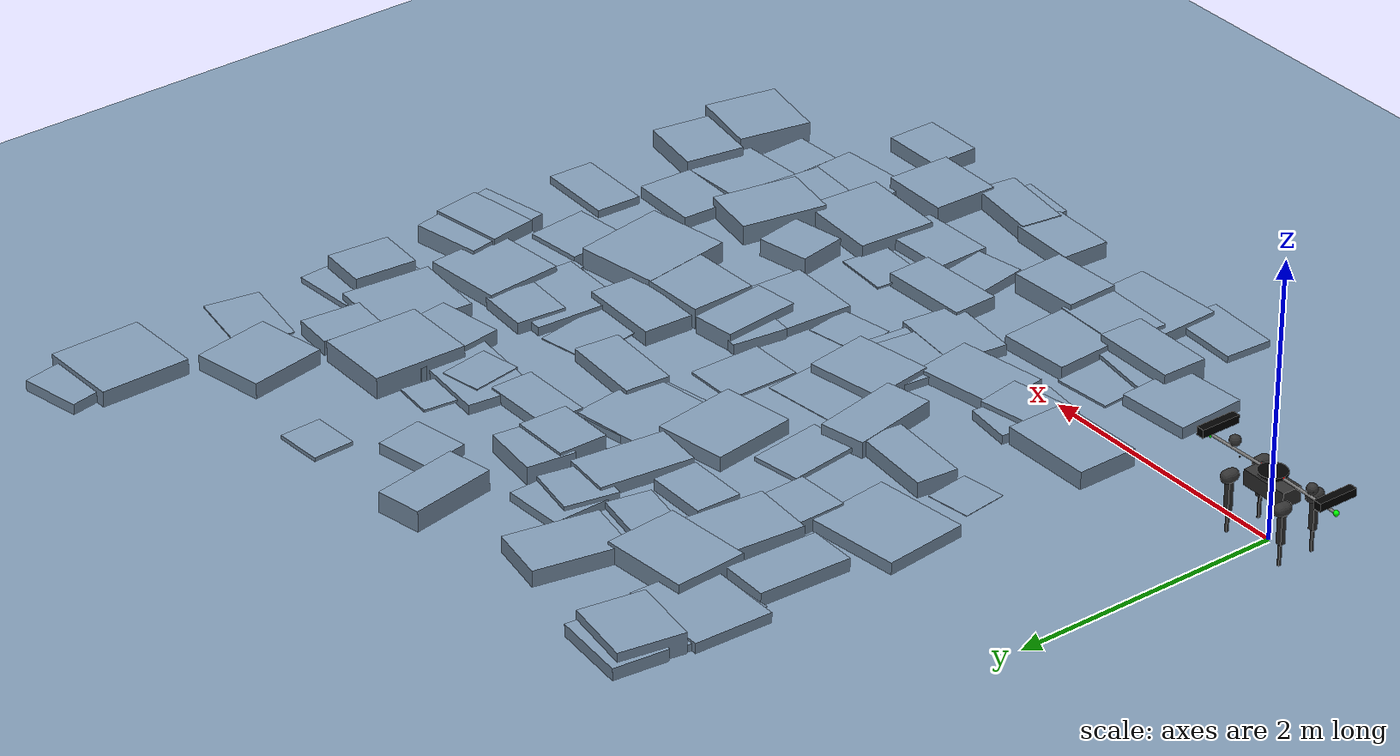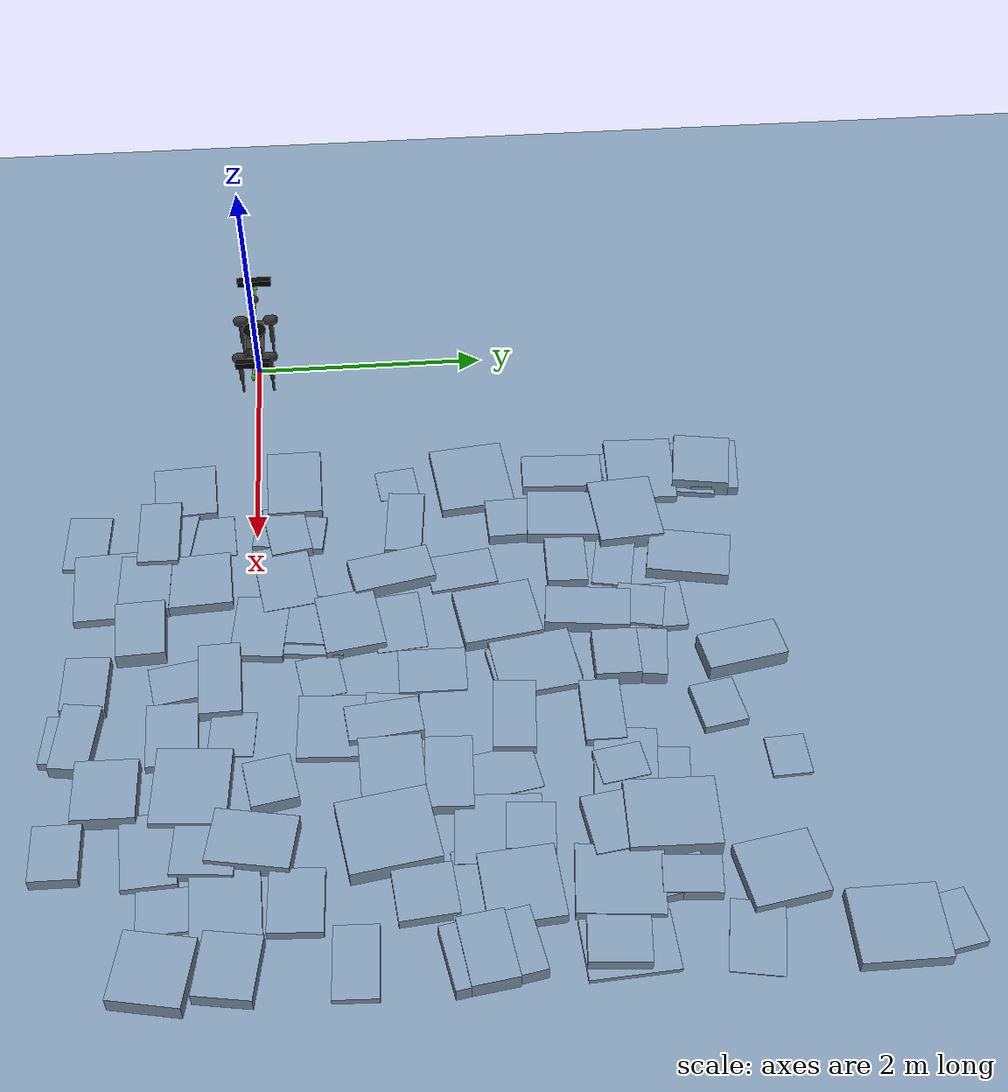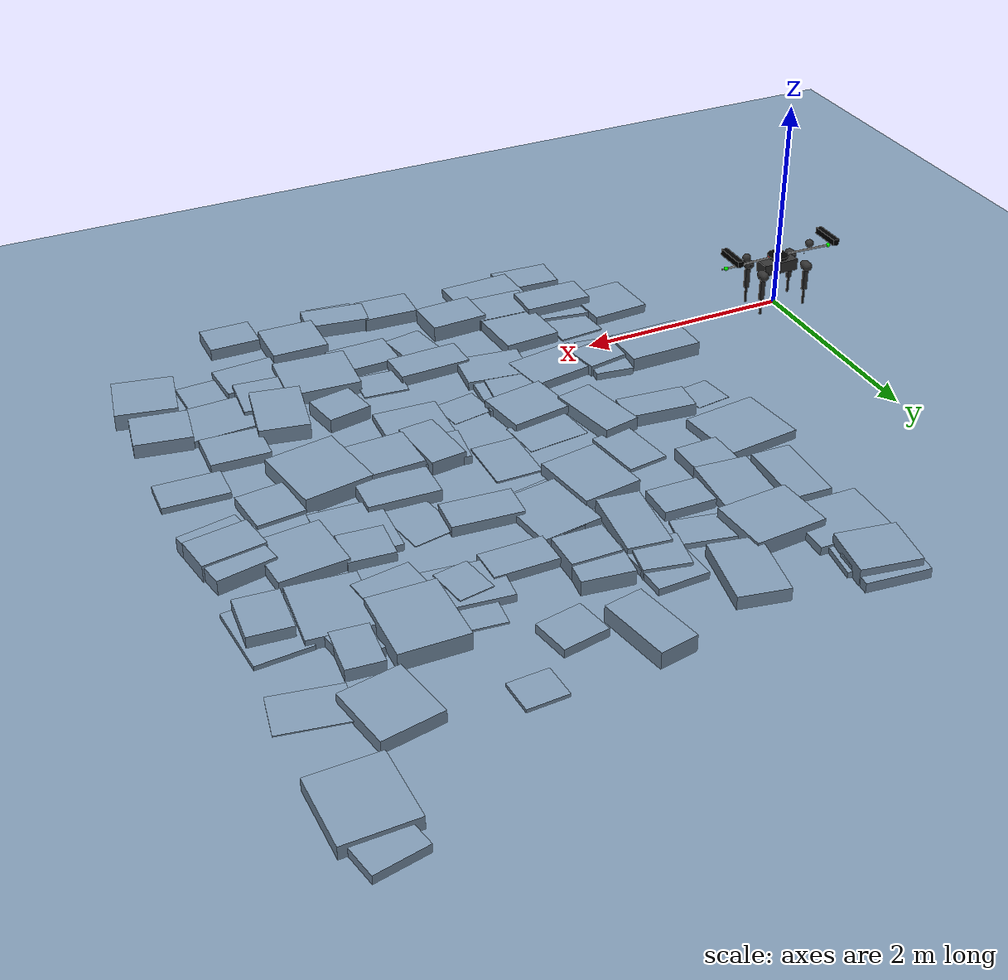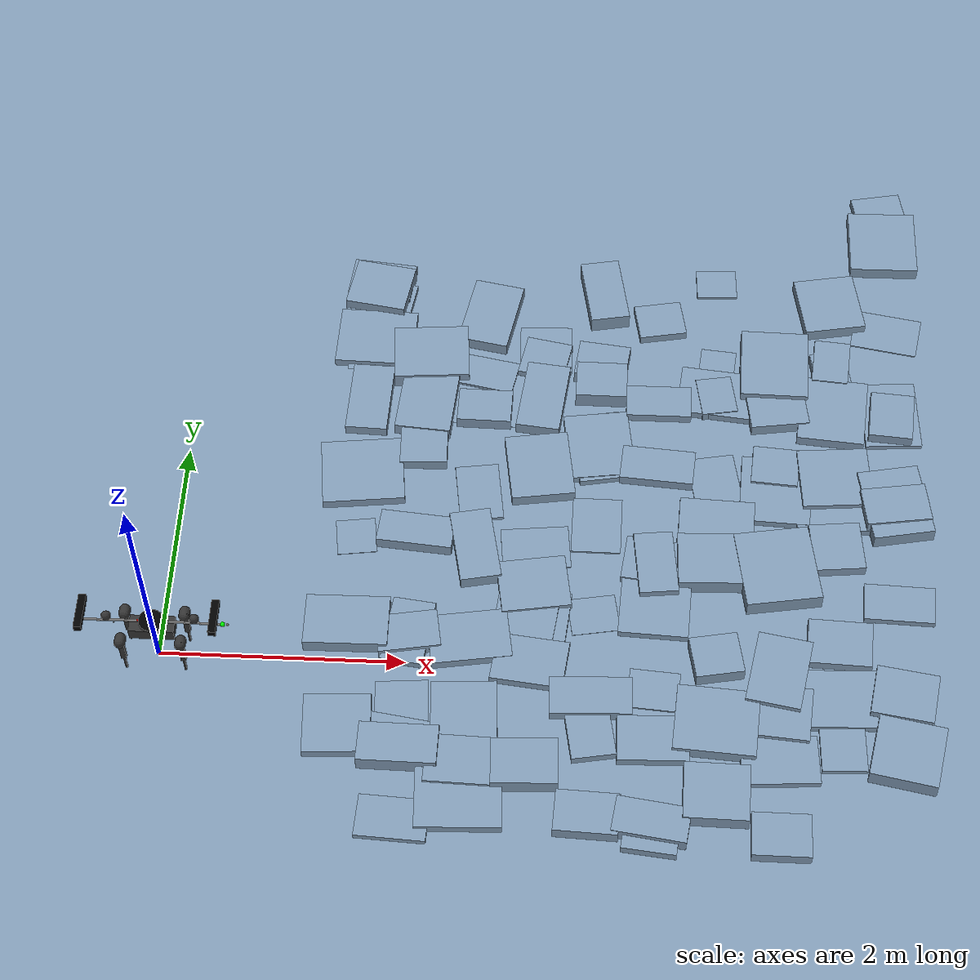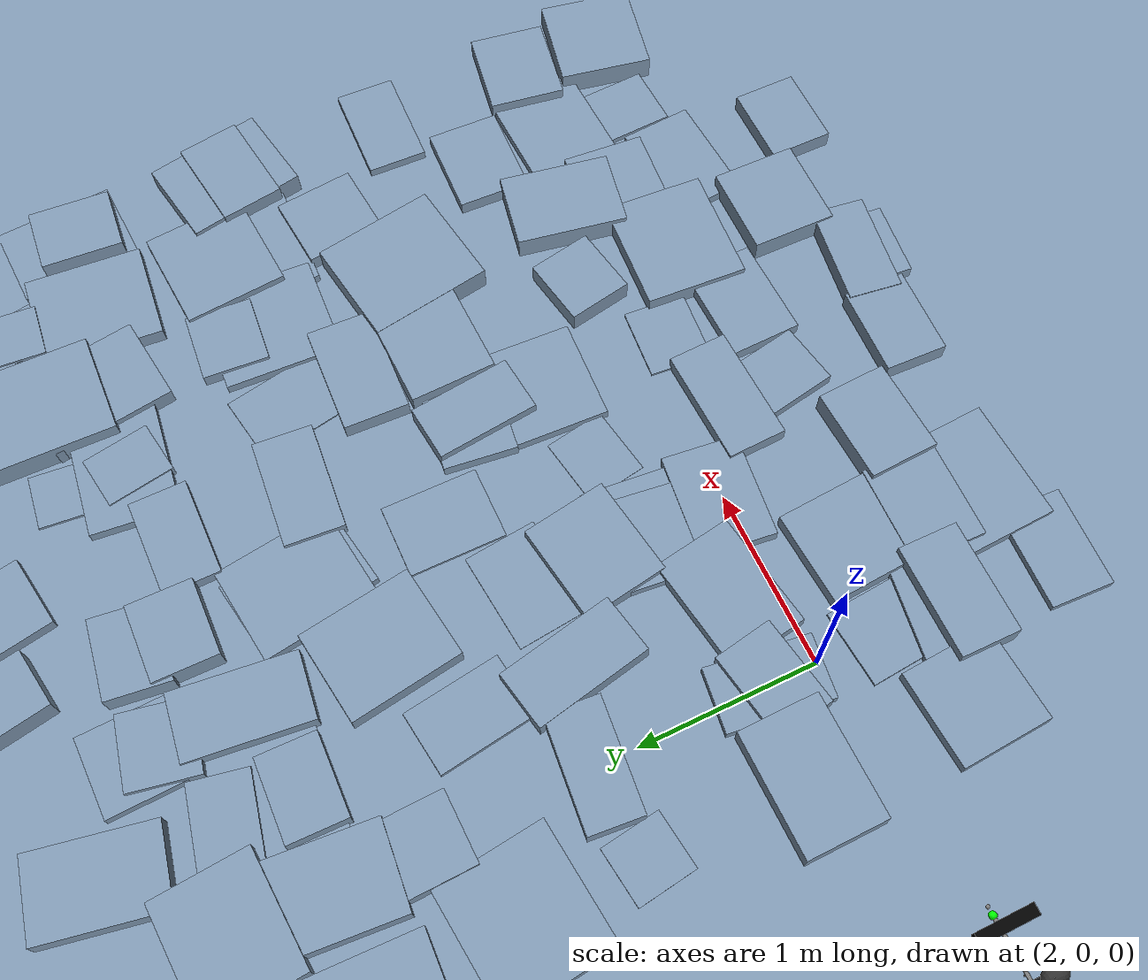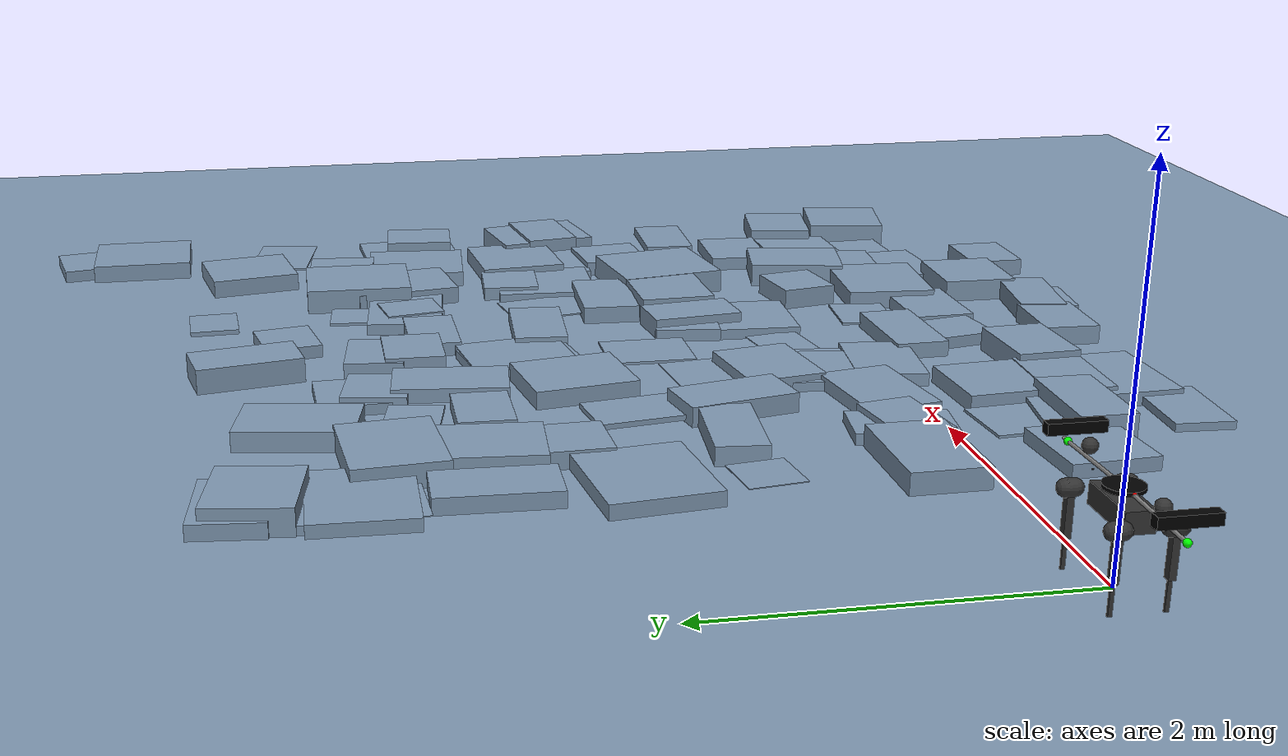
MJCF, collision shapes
<mujoco model="aliengo scene">

  <include file="aliengo_arm_leader_named.xml" />
  <include file="aliengo_arm_follower_named.xml" />
  <include file="weight.xml" />

  <statistic center="0 0 0.1" extent="0.8" />

  <visual>
    <headlight diffuse="0.6 0.6 0.6" ambient="0.3 0.3 0.3" specular="0 0 0" />
    <rgba haze="0.15 0.25 0.35 1" />
    <global azimuth="-130" elevation="-20" />
  </visual>

  <asset>
    <texture type="skybox" builtin="gradient" rgb1="0.3 0.5 0.7" rgb2="0 0 0" width="512" height="3072" />
    <texture type="2d" name="groundplane" builtin="checker" mark="edge" rgb1="0.2 0.3 0.4" rgb2="0.1 0.2 0.3" markrgb="0.8 0.8 0.8" width="300" height="300" />
    <material name="groundplane" texture="groundplane" texuniform="true" texrepeat="5 5" reflectance="0.2" />
  </asset>

  <worldbody>
    <light pos="0 0 1.5" dir="0 0 -1" directional="true" />
    <geom name="floor" size="0 0 0.05" type="plane" material="groundplane" />

  <geom pos="1.5 -0.6082269992179202 0.02" type="box" size="0.2705526752143288 0.25897663659937936 0.05295684991736309" quat="0.9995743283582694 0.0 0.0 0.029174682296719767" /><geom pos="1.5 0.3173696390747409 0.02" type="box" size="0.34273255210020587 0.22668830376515553 0.09896562976033307" quat="0.9999833017187217 0.0 0.0 0.005778951784178585" /><geom pos="1.5 1.1873817873215602 0.02" type="box" size="0.16420721163957738 0.16742585994030812 0.002527299680040715" quat="0.9977880966676552 0.0 0.0 0.06647491367679996" /><geom pos="1.5 1.8273028086490841 0.02" type="box" size="0.3457236684465528 0.30983171284334476 0.05768492028161648" quat="0.9984264804589074 0.0 0.0 0.05607640429306257" /><geom pos="1.5 2.601536498083301 0.02" type="box" size="0.17867065748180927 0.33893378340991676 0.06523104021875896" quat="0.9998543518459778 0.0 0.0 -0.017066783371788637" /><geom pos="1.5 3.2184704949580585 0.02" type="box" size="0.24123006644330972 0.2636867897737297 0.0023487250545443927" quat="0.9997232505625382 0.0 0.0 0.023524929004620103" /><geom pos="1.5 3.2786959665873283 0.02" type="box" size="0.33874961570292483 0.2863640598206967 0.04493848757172325" quat="0.9999207015512163 0.0 0.0 -0.01259327635381275" /><geom pos="1.5 3.642406737529951 0.02" type="box" size="0.2833533430891335 0.28412757392363186 0.026297820134230113" quat="0.9972473499234326 0.0 0.0 -0.07414663222757192" /><geom pos="1.5 3.8037162554149475 0.02" type="box" size="0.26403935408357593 0.23772030269246408 0.12354672975740327" quat="0.9968343050291777 0.0 0.0 -0.07950703312912821" /><geom pos="1.5 3.914091396579253 0.02" type="box" size="0.2806216650930797 0.20065832050795643 0.058288846607038286" quat="0.9986939188465846 0.0 0.0 -0.05109262626692192" /><geom pos="2.0 -1.4028987242069388 0.02" type="box" size="0.28126591789305466 0.17763659026972276 0.024572795210006687" quat="0.9996553581817902 0.0 0.0 -0.026251949612109988" /><geom pos="2.0 -0.7980532044618928 0.02" type="box" size="0.3175889814997608 0.1692196815787926 0.12205743312667447" quat="0.9999803451212234 0.0 0.0 -0.006269718593283766" /><geom pos="2.0 -0.6793254855076487 0.02" type="box" size="0.29785271587966033 0.1578375584508641 0.0353508703220512" quat="0.9971163739076413 0.0 0.0 -0.07588765963763122" /><geom pos="2.0 -0.4139359945682033 0.02" type="box" size="0.21359663587879518 0.232852598902934 0.008018437043598045" quat="0.9992591811521393 0.0 0.0 0.038484917606201714" /><geom pos="2.0 0.2534743853954784 0.02" type="box" size="0.2546496106933399 0.16878810215168832 0.07199331194452241" quat="0.9963163592539387 0.0 0.0 0.08575378873832049" /><geom pos="2.0 0.27358193158297195 0.02" type="box" size="0.1763595724808784 0.2932654408237131 0.03617576161840014" quat="0.9979933172265175 0.0 0.0 -0.06331933963025445" /><geom pos="2.0 1.2357704767004103 0.02" type="box" size="0.31578800584347266 0.1509390952385094 0.08472706709952876" quat="0.9989422598737397 0.0 0.0 -0.04598218609794355" /><geom pos="2.0 2.1885194882173953 0.02" type="box" size="0.1997506287039916 0.26523146688356736 0.07400524140897988" quat="0.9998955950589743 0.0 0.0 0.014449878257610052" /><geom pos="2.0 2.58502522906438 0.02" type="box" size="0.23942507572352548 0.3192817344942256 0.08743490941468804" quat="0.9991794764567955 0.0 0.0 -0.04050152870601273" /><geom pos="2.0 3.086349610991082 0.02" type="box" size="0.32622063942223234 0.2662545745271717 0.1102169202318566" quat="0.9992587233363989 0.0 0.0 0.03849680293362416" /><geom pos="2.5 -1.1984251833254507 0.02" type="box" size="0.3412167269446448 0.2787980398459275 0.05298188106977246" quat="0.9997736182217178 0.0 0.0 0.021277037102349402" /><geom pos="2.5 -0.9001428573694199 0.02" type="box" size="0.282034707498537 0.20801552144208882 0.07725192862485519" quat="0.9998985237569854 0.0 0.0 -0.014245777921945828" /><geom pos="2.5 -0.46872442193544606 0.02" type="box" size="0.26399298214025296 0.26817455224963466 0.07179065610619735" quat="0.9995306268990166 0.0 0.0 0.03063536993180914" /><geom pos="2.5 0.23516416160492026 0.02" type="box" size="0.3293093191702126 0.2235123740095793 0.05448311565820335" quat="0.9969294942979583 0.0 0.0 0.07830442770889247" /><geom pos="2.5 1.1032902189731346 0.02" type="box" size="0.17004537746246023 0.3338965227489347 0.08928016244363893" quat="0.9950271602775137 0.0 0.0 0.09960396734100085" /><geom pos="2.5 1.6723909575877278 0.02" type="box" size="0.18249858693527496 0.27311191285676883 0.015477497856180189" quat="0.9975787831263353 0.0 0.0 0.06954546323219059" /><geom pos="2.5 2.538773283516357 0.02" type="box" size="0.23143665944519992 0.16383339909102762 0.08717859664307046" quat="0.9999568346638896 0.0 0.0 -0.009291329774287042" /><geom pos="2.5 2.710402960777797 0.02" type="box" size="0.3451043010005772 0.3211606684785222 0.0014642605231252465" quat="0.999607902777507 0.0 0.0 -0.028000726861175638" /><geom pos="2.5 2.9343276488381775 0.02" type="box" size="0.25420732124082585 0.16086759766785072 0.02499956561205001" quat="0.9953671563844347 0.0 0.0 -0.09614688757918351" /><geom pos="2.5 3.5558060503379414 0.02" type="box" size="0.21907033613938054 0.3356162586931182 0.0880518002404416" quat="0.995619705812064 0.0 0.0 -0.09349546191499868" /><geom pos="3.0 -0.910090023645429 0.02" type="box" size="0.26544571772083353 0.19757856427490172 0.11677674974059922" quat="0.9997402464637112 0.0 0.0 0.022791217621662953" /><geom pos="3.0 0.034282366338504566 0.02" type="box" size="0.29602440590335394 0.21238899909592038 0.049777632777011485" quat="0.9983166594844859 0.0 0.0 -0.057998684431089374" /><geom pos="3.0 0.46869899189662534 0.02" type="box" size="0.2979101590098575 0.2480917617235134 0.028426828496665404" quat="0.9987934279531521 0.0 0.0 -0.049108942949239905" /><geom pos="3.0 0.5359486233598738 0.02" type="box" size="0.21235917639882051 0.2892686977630919 0.04721897991156011" quat="0.9979476263554097 0.0 0.0 -0.06403542028911598" /><geom pos="3.0 0.7528456077583479 0.02" type="box" size="0.28587855469971346 0.24073936891120906 0.06707240138859027" quat="0.9968546879212563 0.0 0.0 0.07925106415320003" /><geom pos="3.0 1.1363095019302456 0.02" type="box" size="0.28261564062002015 0.20266447534743012 0.002581374933216085" quat="0.9986651065207021 0.0 0.0 0.05165273485494055" /><geom pos="3.0 1.9343563358428093 0.02" type="box" size="0.26766342271072113 0.31620969104723806 0.07862273044889359" quat="0.9972239151727612 0.0 0.0 0.07446115099506297" /><geom pos="3.0 2.665212142612967 0.02" type="box" size="0.18712718886119045 0.34055833139438896 0.08593603454847691" quat="0.9983817190250465 0.0 0.0 -0.05686776869715545" /><geom pos="3.0 3.0898976113644734 0.02" type="box" size="0.20078832851900516 0.1926623954734964 0.0647750892413329" quat="0.9955034567225628 0.0 0.0 -0.0947252218441772" /><geom pos="3.0 3.2074294673265067 0.02" type="box" size="0.22483399606684512 0.24271508487296214 0.03470358828684149" quat="0.9998493733257476 0.0 0.0 0.017355997813716734" /><geom pos="3.5 -1.3167201637859214 0.02" type="box" size="0.2534758214308228 0.17641362126903065 0.08960746014907421" quat="0.9997839360734415 0.0 0.0 -0.02078656223372505" /><geom pos="3.5 -0.5680565439353741 0.02" type="box" size="0.17896955186867544 0.2476112561297909 0.04445159223124445" quat="0.9961229019403699 0.0 0.0 0.087972519742793" /><geom pos="3.5 -0.27590901714282534 0.02" type="box" size="0.3307439479491867 0.16668448708840372 0.06902405874030082" quat="0.9998572792704726 0.0 0.0 0.01689441001775998" /><geom pos="3.5 0.5092438948803126 0.02" type="box" size="0.19816575598308936 0.17005878845309957 0.0020537036989342755" quat="0.996312359999853 0.0 0.0 0.08580024074280536" /><geom pos="3.5 1.3857491401969035 0.02" type="box" size="0.20634602115078982 0.26728203323726535 0.00799440826512264" quat="0.9999958686828723 0.0 0.0 -0.002874476854610391" /><geom pos="3.5 2.1849517275492953 0.02" type="box" size="0.21763179036736913 0.3423140309082997 0.028962703308900564" quat="0.9959649684200622 0.0 0.0 0.08974286422899891" /><geom pos="3.5 2.198188585308195 0.02" type="box" size="0.2760895873733582 0.3248575933249894 0.03662753556347459" quat="0.9975657561362213 0.0 0.0 0.06973207428700909" /><geom pos="3.5 2.837661101706918 0.02" type="box" size="0.21944670358644391 0.179628172189633 0.12272867372728165" quat="0.999990643142241 0.0 0.0 -0.004325925099596612" /><geom pos="3.5 3.0619781306816574 0.02" type="box" size="0.22371692122592352 0.17738005433711979 0.10276471664928069" quat="0.9980767304556466 0.0 0.0 -0.06199064544724872" /><geom pos="3.5 3.836025463380296 0.02" type="box" size="0.1695688968988068 0.32243830348433666 0.12161493612789129" quat="0.9957556342016285 0.0 0.0 0.09203649795441274" /><geom pos="4.0 -1.4465728182131747 0.02" type="box" size="0.2166290304057284 0.16622027799759936 0.05090514642672592" quat="0.9985663715870428 0.0 0.0 -0.05352757733624882" /><geom pos="4.0 -1.3569697839745694 0.02" type="box" size="0.29511887284211574 0.15228549172500622 0.09632259356284703" quat="0.9975081021901673 0.0 0.0 -0.07055200964516038" /><geom pos="4.0 -0.6299255212632411 0.02" type="box" size="0.2844095614707829 0.19907344197056895 0.052567433335012306" quat="0.9999341771577611 0.0 0.0 0.011473506518551946" /><geom pos="4.0 -0.17378495446276143 0.02" type="box" size="0.20406558104774292 0.1762965598582255 0.006921790052649743" quat="0.9992128412547012 0.0 0.0 -0.039669860999342645" /><geom pos="4.0 0.6147605578437574 0.02" type="box" size="0.28665626710953607 0.28912508912777146 0.03543985582277083" quat="0.9997116631390348 0.0 0.0 -0.024012300676630703" /><geom pos="4.0 0.9885736957763189 0.02" type="box" size="0.16136961528664806 0.2893994483449975 0.09733692449263792" quat="0.9984612956564191 0.0 0.0 0.05545305290157583" /><geom pos="4.0 1.033185997030433 0.02" type="box" size="0.2675199270392778 0.2045643804848934 0.04635659990223609" quat="0.9981650392718292 0.0 0.0 -0.06055207986079188" /><geom pos="4.0 1.9926193378638581 0.02" type="box" size="0.3099591769141236 0.16539128939732656 0.06485439360394075" quat="0.9992536461064166 0.0 0.0 -0.03862836707695851" /><geom pos="4.0 2.6740118484676962 0.02" type="box" size="0.2791140488912008 0.15707248715109817 0.053800304938507654" quat="0.9999979932540639 0.0 0.0 0.0020033691235646868" /><geom pos="4.0 3.5779958033959334 0.02" type="box" size="0.20551921954635322 0.17577211309326402 0.04908445956838679" quat="0.9958367682850747 0.0 0.0 0.09115443451384263" /><geom pos="4.5 -1.100974678296898 0.02" type="box" size="0.25876119001546527 0.24138228432915315 0.1102551762787362" quat="0.9999657275561434 0.0 0.0 -0.008279113063173643" /><geom pos="4.5 -0.4649136228497568 0.02" type="box" size="0.3308088785801916 0.28800500403824547 0.08745275678131459" quat="0.9994064535247389 0.0 0.0 -0.03444910235556082" /><geom pos="4.5 0.12607054247392813 0.02" type="box" size="0.1980040546759419 0.1821077644970513 0.09954893431466647" quat="0.9957862831777294 0.0 0.0 0.09170429780050023" /><geom pos="4.5 1.0349142608866666 0.02" type="box" size="0.32154452883871093 0.2414446906707714 0.11898430960409202" quat="0.999885237424119 0.0 0.0 0.01514965284464143" /><geom pos="4.5 1.4589465127765084 0.02" type="box" size="0.31310476375371377 0.1818828926897912 0.07861230488271255" quat="0.9997936950975663 0.0 0.0 -0.020311751356160077" /><geom pos="4.5 1.8156534031790512 0.02" type="box" size="0.20173681337788155 0.3198076616857022 0.004163078318337024" quat="0.9957896550430793 0.0 0.0 0.09166767646878139" /><geom pos="4.5 2.7609549366581305 0.02" type="box" size="0.15326570053674157 0.1870464650472368 0.05015743760045109" quat="0.9963164412387961 0.0 0.0 0.08575283620534331" /><geom pos="4.5 2.7940295281336365 0.02" type="box" size="0.32389770610932644 0.24083247938151037 0.04083761022103251" quat="0.9985718260676276 0.0 0.0 -0.053425725862767906" /><geom pos="4.5 3.0472207218564886 0.02" type="box" size="0.15312121288936564 0.23575914449964758 0.008509259246840026" quat="0.9987695869359595 0.0 0.0 -0.049591453011308684" /><geom pos="4.5 4.037565723417383 0.02" type="box" size="0.17621104624305156 0.15240724457953087 0.01443553714234351" quat="0.9997192616987649 0.0 0.0 0.02369383439792598" /><geom pos="5.0 -1.4346957928482198 0.02" type="box" size="0.23181081907461232 0.18259088520932107 0.07984521967081616" quat="0.9999981202744781 0.0 0.0 -0.001938929475366585" /><geom pos="5.0 -0.7688366752890321 0.02" type="box" size="0.3066468876627626 0.20767969946629877 0.03017732750957175" quat="0.9994718917742166 0.0 0.0 0.032495192771680725" /><geom pos="5.0 -0.35397980595546796 0.02" type="box" size="0.25346170344045776 0.23481779768716987 0.06933597608267737" quat="0.9990931959787015 0.0 0.0 -0.04257682173511863" /><geom pos="5.0 -0.0054604364629047275 0.02" type="box" size="0.22210911209717843 0.31573138291114755 0.11562086399414902" quat="0.9958806440577376 0.0 0.0 -0.09067382638416542" /><geom pos="5.0 0.9865508069515694 0.02" type="box" size="0.31299329587404945 0.3470982855286595 0.12112146308379397" quat="0.9967221290553172 0.0 0.0 0.080901158529625" /><geom pos="5.0 1.044907165932158 0.02" type="box" size="0.19988400821129024 0.17118123097644644 0.11886907638192426" quat="0.9985790414442157 0.0 0.0 -0.05329069326206338" /><geom pos="5.0 1.793695423472291 0.02" type="box" size="0.29614181982549526 0.32634404246676796 0.03405461193324531" quat="0.9997074695757256 0.0 0.0 -0.02418626210267934" /><geom pos="5.0 2.03143724948793 0.02" type="box" size="0.19756144850780777 0.1843706198095286 0.05616145608596726" quat="0.9992354453695604 0.0 0.0 -0.03909635171082214" /><geom pos="5.0 2.782202111374282 0.02" type="box" size="0.25047789149785227 0.3385167199395861 0.0792497122180826" quat="0.9973031828622793 0.0 0.0 0.07339183505518342" /><geom pos="5.0 3.0749961428148005 0.02" type="box" size="0.2899150120449503 0.3435931133208454 0.12430009870595993" quat="0.999953577353966 0.0 0.0 -0.00963551436125515" /><geom pos="5.5 -0.60461411571179 0.02" type="box" size="0.18047094113754608 0.23349727495920236 0.016411166059157004" quat="0.9997831974920582 0.0 0.0 0.020822055915689145" /><geom pos="5.5 -0.19788076987604164 0.02" type="box" size="0.3435589343597004 0.25937698033388445 0.034352946233449574" quat="0.9998298758210252 0.0 0.0 0.018445037698885194" /><geom pos="5.5 0.3079856139492667 0.02" type="box" size="0.26041565533839417 0.20433055352122917 0.05693051868125337" quat="0.9998068016387034 0.0 0.0 -0.019656026988847806" /><geom pos="5.5 1.2321443805700305 0.02" type="box" size="0.21207616519596229 0.2246069727761495 0.06562130528178303" quat="0.9987443055724464 0.0 0.0 0.050098024777546456" /><geom pos="5.5 1.5806203696035275 0.02" type="box" size="0.3224637093671805 0.1597380591951057 0.031705315532102846" quat="0.9999419729012696 0.0 0.0 -0.010772689094025185" /><geom pos="5.5 1.9223184844682595 0.02" type="box" size="0.2980195051235365 0.28610289622856516 0.0777980535707506" quat="0.9991136867890812 0.0 0.0 0.04209324020231435" /><geom pos="5.5 2.6326553134424726 0.02" type="box" size="0.28524849645549255 0.3258469526062654 0.0679597567285119" quat="0.9990557598017029 0.0 0.0 -0.04344639003464153" /><geom pos="5.5 3.0385976354107562 0.02" type="box" size="0.15157682070168807 0.22453581396419908 0.06631715182034773" quat="0.9964385542695009 0.0 0.0 0.08432204673338392" /><geom pos="5.5 3.1543008687378498 0.02" type="box" size="0.15486263994203153 0.21852219686831806 0.07777888235497436" quat="0.9990239393937274 0.0 0.0 -0.04417203321376658" /><geom pos="5.5 3.8014975226318857 0.02" type="box" size="0.26542804880406834 0.2890540011809372 0.08399464257447779" quat="0.9959731811323911 0.0 0.0 0.0896516729627805" /><geom pos="6.0 -0.6863213502981366 0.02" type="box" size="0.2700784474195279 0.2677479219940576 0.1203462899800303" quat="0.9953353713779168 0.0 0.0 -0.09647537760477702" /><geom pos="6.0 -0.16636897572729836 0.02" type="box" size="0.2519614393243168 0.2167929739193618 0.09885502040342561" quat="0.996757488611042 0.0 0.0 -0.08046433307875363" /><geom pos="6.0 0.7205918054901193 0.02" type="box" size="0.2887912821869095 0.1681771464064819 0.02846993769223262" quat="0.9998390881225072 0.0 0.0 -0.017938725215388415" /><geom pos="6.0 1.6429397872867524 0.02" type="box" size="0.2737652336482753 0.1766922941869869 0.1225725165984103" quat="0.9972367808505237 0.0 0.0 0.07428864596211515" /><geom pos="6.0 1.6789736047153219 0.02" type="box" size="0.2582761587514272 0.33466121357783263 0.1037371710754179" quat="0.9956173617582609 0.0 0.0 0.09352042004567876" /><geom pos="6.0 2.5652782708018815 0.02" type="box" size="0.184954400832188 0.22782693542023716 0.1190178371619276" quat="0.999200337938382 0.0 0.0 -0.03998355491727862" /><geom pos="6.0 2.6417650398321673 0.02" type="box" size="0.23927888309664058 0.3315751188708652 0.020028808290017908" quat="0.9994808678722888 0.0 0.0 0.03221792602351033" /><geom pos="6.0 3.549497997317207 0.02" type="box" size="0.2892926289305001 0.19947975110783073 0.004951940322439716" quat="0.9961295189379453 0.0 0.0 -0.08789756253991075" /><geom pos="6.0 4.547460248645881 0.02" type="box" size="0.2979767835658202 0.329612471442747 0.08407278891206517" quat="0.9999832496569163 0.0 0.0 0.005787953489224539" /><geom pos="6.0 4.87544824955396 0.02" type="box" size="0.22243781178787786 0.2441297898427819 0.04728064686543272" quat="0.995404602413459 0.0 0.0 0.0957584330182141" /><geom pos="1.5 -0.6082269992179202 0.02" type="box" size="0.2705526752143288 0.25897663659937936 0.05295684991736309" quat="0.9995743283582694 0.0 0.0 0.029174682296719767" /><geom pos="1.5 0.3173696390747409 0.02" type="box" size="0.34273255210020587 0.22668830376515553 0.09896562976033307" quat="0.9999833017187217 0.0 0.0 0.005778951784178585" /><geom pos="1.5 1.1873817873215602 0.02" type="box" size="0.16420721163957738 0.16742585994030812 0.002527299680040715" quat="0.9977880966676552 0.0 0.0 0.06647491367679996" /><geom pos="1.5 1.8273028086490841 0.02" type="box" size="0.3457236684465528 0.30983171284334476 0.05768492028161648" quat="0.9984264804589074 0.0 0.0 0.05607640429306257" /><geom pos="1.5 2.601536498083301 0.02" type="box" size="0.17867065748180927 0.33893378340991676 0.06523104021875896" quat="0.9998543518459778 0.0 0.0 -0.017066783371788637" /><geom pos="1.5 3.2184704949580585 0.02" type="box" size="0.24123006644330972 0.2636867897737297 0.0023487250545443927" quat="0.9997232505625382 0.0 0.0 0.023524929004620103" /><geom pos="1.5 3.2786959665873283 0.02" type="box" size="0.33874961570292483 0.2863640598206967 0.04493848757172325" quat="0.9999207015512163 0.0 0.0 -0.01259327635381275" /><geom pos="1.5 3.642406737529951 0.02" type="box" size="0.2833533430891335 0.28412757392363186 0.026297820134230113" quat="0.9972473499234326 0.0 0.0 -0.07414663222757192" /><geom pos="1.5 3.8037162554149475 0.02" type="box" size="0.26403935408357593 0.23772030269246408 0.12354672975740327" quat="0.9968343050291777 0.0 0.0 -0.07950703312912821" /><geom pos="1.5 3.914091396579253 0.02" type="box" size="0.2806216650930797 0.20065832050795643 0.058288846607038286" quat="0.9986939188465846 0.0 0.0 -0.05109262626692192" /><geom pos="2.0 -1.4028987242069388 0.02" type="box" size="0.28126591789305466 0.17763659026972276 0.024572795210006687" quat="0.9996553581817902 0.0 0.0 -0.026251949612109988" /><geom pos="2.0 -0.7980532044618928 0.02" type="box" size="0.3175889814997608 0.1692196815787926 0.12205743312667447" quat="0.9999803451212234 0.0 0.0 -0.006269718593283766" /><geom pos="2.0 -0.6793254855076487 0.02" type="box" size="0.29785271587966033 0.1578375584508641 0.0353508703220512" quat="0.9971163739076413 0.0 0.0 -0.07588765963763122" /><geom pos="2.0 -0.4139359945682033 0.02" type="box" size="0.21359663587879518 0.232852598902934 0.008018437043598045" quat="0.9992591811521393 0.0 0.0 0.038484917606201714" /><geom pos="2.0 0.2534743853954784 0.02" type="box" size="0.2546496106933399 0.16878810215168832 0.07199331194452241" quat="0.9963163592539387 0.0 0.0 0.08575378873832049" /><geom pos="2.0 0.27358193158297195 0.02" type="box" size="0.1763595724808784 0.2932654408237131 0.03617576161840014" quat="0.9979933172265175 0.0 0.0 -0.06331933963025445" /><geom pos="2.0 1.2357704767004103 0.02" type="box" size="0.31578800584347266 0.1509390952385094 0.08472706709952876" quat="0.9989422598737397 0.0 0.0 -0.04598218609794355" /><geom pos="2.0 2.1885194882173953 0.02" type="box" size="0.1997506287039916 0.26523146688356736 0.07400524140897988" quat="0.9998955950589743 0.0 0.0 0.014449878257610052" /><geom pos="2.0 2.58502522906438 0.02" type="box" size="0.23942507572352548 0.3192817344942256 0.08743490941468804" quat="0.9991794764567955 0.0 0.0 -0.04050152870601273" /><geom pos="2.0 3.086349610991082 0.02" type="box" size="0.32622063942223234 0.2662545745271717 0.1102169202318566" quat="0.9992587233363989 0.0 0.0 0.03849680293362416" /><geom pos="2.5 -1.1984251833254507 0.02" type="box" size="0.3412167269446448 0.2787980398459275 0.05298188106977246" quat="0.9997736182217178 0.0 0.0 0.021277037102349402" /><geom pos="2.5 -0.9001428573694199 0.02" type="box" size="0.282034707498537 0.20801552144208882 0.07725192862485519" quat="0.9998985237569854 0.0 0.0 -0.014245777921945828" /><geom pos="2.5 -0.46872442193544606 0.02" type="box" size="0.26399298214025296 0.26817455224963466 0.07179065610619735" quat="0.9995306268990166 0.0 0.0 0.03063536993180914" /><geom pos="2.5 0.23516416160492026 0.02" type="box" size="0.3293093191702126 0.2235123740095793 0.05448311565820335" quat="0.9969294942979583 0.0 0.0 0.07830442770889247" /><geom pos="2.5 1.1032902189731346 0.02" type="box" size="0.17004537746246023 0.3338965227489347 0.08928016244363893" quat="0.9950271602775137 0.0 0.0 0.09960396734100085" /><geom pos="2.5 1.6723909575877278 0.02" type="box" size="0.18249858693527496 0.27311191285676883 0.015477497856180189" quat="0.9975787831263353 0.0 0.0 0.06954546323219059" /><geom pos="2.5 2.538773283516357 0.02" type="box" size="0.23143665944519992 0.16383339909102762 0.08717859664307046" quat="0.9999568346638896 0.0 0.0 -0.009291329774287042" /><geom pos="2.5 2.710402960777797 0.02" type="box" size="0.3451043010005772 0.3211606684785222 0.0014642605231252465" quat="0.999607902777507 0.0 0.0 -0.028000726861175638" /><geom pos="2.5 2.9343276488381775 0.02" type="box" size="0.25420732124082585 0.16086759766785072 0.02499956561205001" quat="0.9953671563844347 0.0 0.0 -0.09614688757918351" /><geom pos="2.5 3.5558060503379414 0.02" type="box" size="0.21907033613938054 0.3356162586931182 0.0880518002404416" quat="0.995619705812064 0.0 0.0 -0.09349546191499868" /><geom pos="3.0 -0.910090023645429 0.02" type="box" size="0.26544571772083353 0.19757856427490172 0.11677674974059922" quat="0.9997402464637112 0.0 0.0 0.022791217621662953" /><geom pos="3.0 0.034282366338504566 0.02" type="box" size="0.29602440590335394 0.21238899909592038 0.049777632777011485" quat="0.9983166594844859 0.0 0.0 -0.057998684431089374" /><geom pos="3.0 0.46869899189662534 0.02" type="box" size="0.2979101590098575 0.2480917617235134 0.028426828496665404" quat="0.9987934279531521 0.0 0.0 -0.049108942949239905" /><geom pos="3.0 0.5359486233598738 0.02" type="box" size="0.21235917639882051 0.2892686977630919 0.04721897991156011" quat="0.9979476263554097 0.0 0.0 -0.06403542028911598" /><geom pos="3.0 0.7528456077583479 0.02" type="box" size="0.28587855469971346 0.24073936891120906 0.06707240138859027" quat="0.9968546879212563 0.0 0.0 0.07925106415320003" /><geom pos="3.0 1.1363095019302456 0.02" type="box" size="0.28261564062002015 0.20266447534743012 0.002581374933216085" quat="0.9986651065207021 0.0 0.0 0.05165273485494055" /><geom pos="3.0 1.9343563358428093 0.02" type="box" size="0.26766342271072113 0.31620969104723806 0.07862273044889359" quat="0.9972239151727612 0.0 0.0 0.07446115099506297" /><geom pos="3.0 2.665212142612967 0.02" type="box" size="0.18712718886119045 0.34055833139438896 0.08593603454847691" quat="0.9983817190250465 0.0 0.0 -0.05686776869715545" /><geom pos="3.0 3.0898976113644734 0.02" type="box" size="0.20078832851900516 0.1926623954734964 0.0647750892413329" quat="0.9955034567225628 0.0 0.0 -0.0947252218441772" /><geom pos="3.0 3.2074294673265067 0.02" type="box" size="0.22483399606684512 0.24271508487296214 0.03470358828684149" quat="0.9998493733257476 0.0 0.0 0.017355997813716734" /><geom pos="3.5 -1.3167201637859214 0.02" type="box" size="0.2534758214308228 0.17641362126903065 0.08960746014907421" quat="0.9997839360734415 0.0 0.0 -0.02078656223372505" /><geom pos="3.5 -0.5680565439353741 0.02" type="box" size="0.17896955186867544 0.2476112561297909 0.04445159223124445" quat="0.9961229019403699 0.0 0.0 0.087972519742793" /><geom pos="3.5 -0.27590901714282534 0.02" type="box" size="0.3307439479491867 0.16668448708840372 0.06902405874030082" quat="0.9998572792704726 0.0 0.0 0.01689441001775998" /><geom pos="3.5 0.5092438948803126 0.02" type="box" size="0.19816575598308936 0.17005878845309957 0.0020537036989342755" quat="0.996312359999853 0.0 0.0 0.08580024074280536" /><geom pos="3.5 1.3857491401969035 0.02" type="box" size="0.20634602115078982 0.26728203323726535 0.00799440826512264" quat="0.9999958686828723 0.0 0.0 -0.002874476854610391" /><geom pos="3.5 2.1849517275492953 0.02" type="box" size="0.21763179036736913 0.3423140309082997 0.028962703308900564" quat="0.9959649684200622 0.0 0.0 0.08974286422899891" /><geom pos="3.5 2.198188585308195 0.02" type="box" size="0.2760895873733582 0.3248575933249894 0.03662753556347459" quat="0.9975657561362213 0.0 0.0 0.06973207428700909" /><geom pos="3.5 2.837661101706918 0.02" type="box" size="0.21944670358644391 0.179628172189633 0.12272867372728165" quat="0.999990643142241 0.0 0.0 -0.004325925099596612" /><geom pos="3.5 3.0619781306816574 0.02" type="box" size="0.22371692122592352 0.17738005433711979 0.10276471664928069" quat="0.9980767304556466 0.0 0.0 -0.06199064544724872" /><geom pos="3.5 3.836025463380296 0.02" type="box" size="0.1695688968988068 0.32243830348433666 0.12161493612789129" quat="0.9957556342016285 0.0 0.0 0.09203649795441274" /><geom pos="4.0 -1.4465728182131747 0.02" type="box" size="0.2166290304057284 0.16622027799759936 0.05090514642672592" quat="0.9985663715870428 0.0 0.0 -0.05352757733624882" /><geom pos="4.0 -1.3569697839745694 0.02" type="box" size="0.29511887284211574 0.15228549172500622 0.09632259356284703" quat="0.9975081021901673 0.0 0.0 -0.07055200964516038" /><geom pos="4.0 -0.6299255212632411 0.02" type="box" size="0.2844095614707829 0.19907344197056895 0.052567433335012306" quat="0.9999341771577611 0.0 0.0 0.011473506518551946" /><geom pos="4.0 -0.17378495446276143 0.02" type="box" size="0.20406558104774292 0.1762965598582255 0.006921790052649743" quat="0.9992128412547012 0.0 0.0 -0.039669860999342645" /><geom pos="4.0 0.6147605578437574 0.02" type="box" size="0.28665626710953607 0.28912508912777146 0.03543985582277083" quat="0.9997116631390348 0.0 0.0 -0.024012300676630703" /><geom pos="4.0 0.9885736957763189 0.02" type="box" size="0.16136961528664806 0.2893994483449975 0.09733692449263792" quat="0.9984612956564191 0.0 0.0 0.05545305290157583" /><geom pos="4.0 1.033185997030433 0.02" type="box" size="0.2675199270392778 0.2045643804848934 0.04635659990223609" quat="0.9981650392718292 0.0 0.0 -0.06055207986079188" /><geom pos="4.0 1.9926193378638581 0.02" type="box" size="0.3099591769141236 0.16539128939732656 0.06485439360394075" quat="0.9992536461064166 0.0 0.0 -0.03862836707695851" /><geom pos="4.0 2.6740118484676962 0.02" type="box" size="0.2791140488912008 0.15707248715109817 0.053800304938507654" quat="0.9999979932540639 0.0 0.0 0.0020033691235646868" /><geom pos="4.0 3.5779958033959334 0.02" type="box" size="0.20551921954635322 0.17577211309326402 0.04908445956838679" quat="0.9958367682850747 0.0 0.0 0.09115443451384263" /><geom pos="4.5 -1.100974678296898 0.02" type="box" size="0.25876119001546527 0.24138228432915315 0.1102551762787362" quat="0.9999657275561434 0.0 0.0 -0.008279113063173643" /><geom pos="4.5 -0.4649136228497568 0.02" type="box" size="0.3308088785801916 0.28800500403824547 0.08745275678131459" quat="0.9994064535247389 0.0 0.0 -0.03444910235556082" /><geom pos="4.5 0.12607054247392813 0.02" type="box" size="0.1980040546759419 0.1821077644970513 0.09954893431466647" quat="0.9957862831777294 0.0 0.0 0.09170429780050023" /><geom pos="4.5 1.0349142608866666 0.02" type="box" size="0.32154452883871093 0.2414446906707714 0.11898430960409202" quat="0.999885237424119 0.0 0.0 0.01514965284464143" /><geom pos="4.5 1.4589465127765084 0.02" type="box" size="0.31310476375371377 0.1818828926897912 0.07861230488271255" quat="0.9997936950975663 0.0 0.0 -0.020311751356160077" /><geom pos="4.5 1.8156534031790512 0.02" type="box" size="0.20173681337788155 0.3198076616857022 0.004163078318337024" quat="0.9957896550430793 0.0 0.0 0.09166767646878139" /><geom pos="4.5 2.7609549366581305 0.02" type="box" size="0.15326570053674157 0.1870464650472368 0.05015743760045109" quat="0.9963164412387961 0.0 0.0 0.08575283620534331" /><geom pos="4.5 2.7940295281336365 0.02" type="box" size="0.32389770610932644 0.24083247938151037 0.04083761022103251" quat="0.9985718260676276 0.0 0.0 -0.053425725862767906" /><geom pos="4.5 3.0472207218564886 0.02" type="box" size="0.15312121288936564 0.23575914449964758 0.008509259246840026" quat="0.9987695869359595 0.0 0.0 -0.049591453011308684" /><geom pos="4.5 4.037565723417383 0.02" type="box" size="0.17621104624305156 0.15240724457953087 0.01443553714234351" quat="0.9997192616987649 0.0 0.0 0.02369383439792598" /><geom pos="5.0 -1.4346957928482198 0.02" type="box" size="0.23181081907461232 0.18259088520932107 0.07984521967081616" quat="0.9999981202744781 0.0 0.0 -0.001938929475366585" /><geom pos="5.0 -0.7688366752890321 0.02" type="box" size="0.3066468876627626 0.20767969946629877 0.03017732750957175" quat="0.9994718917742166 0.0 0.0 0.032495192771680725" /><geom pos="5.0 -0.35397980595546796 0.02" type="box" size="0.25346170344045776 0.23481779768716987 0.06933597608267737" quat="0.9990931959787015 0.0 0.0 -0.04257682173511863" /><geom pos="5.0 -0.0054604364629047275 0.02" type="box" size="0.22210911209717843 0.31573138291114755 0.11562086399414902" quat="0.9958806440577376 0.0 0.0 -0.09067382638416542" /><geom pos="5.0 0.9865508069515694 0.02" type="box" size="0.31299329587404945 0.3470982855286595 0.12112146308379397" quat="0.9967221290553172 0.0 0.0 0.080901158529625" /><geom pos="5.0 1.044907165932158 0.02" type="box" size="0.19988400821129024 0.17118123097644644 0.11886907638192426" quat="0.9985790414442157 0.0 0.0 -0.05329069326206338" /><geom pos="5.0 1.793695423472291 0.02" type="box" size="0.29614181982549526 0.32634404246676796 0.03405461193324531" quat="0.9997074695757256 0.0 0.0 -0.02418626210267934" /><geom pos="5.0 2.03143724948793 0.02" type="box" size="0.19756144850780777 0.1843706198095286 0.05616145608596726" quat="0.9992354453695604 0.0 0.0 -0.03909635171082214" /><geom pos="5.0 2.782202111374282 0.02" type="box" size="0.25047789149785227 0.3385167199395861 0.0792497122180826" quat="0.9973031828622793 0.0 0.0 0.07339183505518342" /><geom pos="5.0 3.0749961428148005 0.02" type="box" size="0.2899150120449503 0.3435931133208454 0.12430009870595993" quat="0.999953577353966 0.0 0.0 -0.00963551436125515" /><geom pos="5.5 -0.60461411571179 0.02" type="box" size="0.18047094113754608 0.23349727495920236 0.016411166059157004" quat="0.9997831974920582 0.0 0.0 0.020822055915689145" /><geom pos="5.5 -0.19788076987604164 0.02" type="box" size="0.3435589343597004 0.25937698033388445 0.034352946233449574" quat="0.9998298758210252 0.0 0.0 0.018445037698885194" /><geom pos="5.5 0.3079856139492667 0.02" type="box" size="0.26041565533839417 0.20433055352122917 0.05693051868125337" quat="0.9998068016387034 0.0 0.0 -0.019656026988847806" /><geom pos="5.5 1.2321443805700305 0.02" type="box" size="0.21207616519596229 0.2246069727761495 0.06562130528178303" quat="0.9987443055724464 0.0 0.0 0.050098024777546456" /><geom pos="5.5 1.5806203696035275 0.02" type="box" size="0.3224637093671805 0.1597380591951057 0.031705315532102846" quat="0.9999419729012696 0.0 0.0 -0.010772689094025185" /><geom pos="5.5 1.9223184844682595 0.02" type="box" size="0.2980195051235365 0.28610289622856516 0.0777980535707506" quat="0.9991136867890812 0.0 0.0 0.04209324020231435" /><geom pos="5.5 2.6326553134424726 0.02" type="box" size="0.28524849645549255 0.3258469526062654 0.0679597567285119" quat="0.9990557598017029 0.0 0.0 -0.04344639003464153" /><geom pos="5.5 3.0385976354107562 0.02" type="box" size="0.15157682070168807 0.22453581396419908 0.06631715182034773" quat="0.9964385542695009 0.0 0.0 0.08432204673338392" /><geom pos="5.5 3.1543008687378498 0.02" type="box" size="0.15486263994203153 0.21852219686831806 0.07777888235497436" quat="0.9990239393937274 0.0 0.0 -0.04417203321376658" /><geom pos="5.5 3.8014975226318857 0.02" type="box" size="0.26542804880406834 0.2890540011809372 0.08399464257447779" quat="0.9959731811323911 0.0 0.0 0.0896516729627805" /><geom pos="6.0 -0.6863213502981366 0.02" type="box" size="0.2700784474195279 0.2677479219940576 0.1203462899800303" quat="0.9953353713779168 0.0 0.0 -0.09647537760477702" /><geom pos="6.0 -0.16636897572729836 0.02" type="box" size="0.2519614393243168 0.2167929739193618 0.09885502040342561" quat="0.996757488611042 0.0 0.0 -0.08046433307875363" /><geom pos="6.0 0.7205918054901193 0.02" type="box" size="0.2887912821869095 0.1681771464064819 0.02846993769223262" quat="0.9998390881225072 0.0 0.0 -0.017938725215388415" /><geom pos="6.0 1.6429397872867524 0.02" type="box" size="0.2737652336482753 0.1766922941869869 0.1225725165984103" quat="0.9972367808505237 0.0 0.0 0.07428864596211515" /><geom pos="6.0 1.6789736047153219 0.02" type="box" size="0.2582761587514272 0.33466121357783263 0.1037371710754179" quat="0.9956173617582609 0.0 0.0 0.09352042004567876" /><geom pos="6.0 2.5652782708018815 0.02" type="box" size="0.184954400832188 0.22782693542023716 0.1190178371619276" quat="0.999200337938382 0.0 0.0 -0.03998355491727862" /><geom pos="6.0 2.6417650398321673 0.02" type="box" size="0.23927888309664058 0.3315751188708652 0.020028808290017908" quat="0.9994808678722888 0.0 0.0 0.03221792602351033" /><geom pos="6.0 3.549497997317207 0.02" type="box" size="0.2892926289305001 0.19947975110783073 0.004951940322439716" quat="0.9961295189379453 0.0 0.0 -0.08789756253991075" /><geom pos="6.0 4.547460248645881 0.02" type="box" size="0.2979767835658202 0.329612471442747 0.08407278891206517" quat="0.9999832496569163 0.0 0.0 0.005787953489224539" /><geom pos="6.0 4.87544824955396 0.02" type="box" size="0.22243781178787786 0.2441297898427819 0.04728064686543272" quat="0.995404602413459 0.0 0.0 0.0957584330182141" /><geom pos="1.5 -0.6082269992179202 0.02" type="box" size="0.2705526752143288 0.25897663659937936 0.05295684991736309" quat="0.9995743283582694 0.0 0.0 0.029174682296719767" /><geom pos="1.5 0.3173696390747409 0.02" type="box" size="0.34273255210020587 0.22668830376515553 0.09896562976033307" quat="0.9999833017187217 0.0 0.0 0.005778951784178585" /><geom pos="1.5 1.1873817873215602 0.02" type="box" size="0.16420721163957738 0.16742585994030812 0.002527299680040715" quat="0.9977880966676552 0.0 0.0 0.06647491367679996" /><geom pos="1.5 1.8273028086490841 0.02" type="box" size="0.3457236684465528 0.30983171284334476 0.05768492028161648" quat="0.9984264804589074 0.0 0.0 0.05607640429306257" /><geom pos="1.5 2.601536498083301 0.02" type="box" size="0.17867065748180927 0.33893378340991676 0.06523104021875896" quat="0.9998543518459778 0.0 0.0 -0.017066783371788637" /><geom pos="1.5 3.2184704949580585 0.02" type="box" size="0.24123006644330972 0.2636867897737297 0.0023487250545443927" quat="0.9997232505625382 0.0 0.0 0.023524929004620103" /><geom pos="1.5 3.2786959665873283 0.02" type="box" size="0.33874961570292483 0.2863640598206967 0.04493848757172325" quat="0.9999207015512163 0.0 0.0 -0.01259327635381275" /><geom pos="1.5 3.642406737529951 0.02" type="box" size="0.2833533430891335 0.28412757392363186 0.026297820134230113" quat="0.9972473499234326 0.0 0.0 -0.07414663222757192" /><geom pos="1.5 3.8037162554149475 0.02" type="box" size="0.26403935408357593 0.23772030269246408 0.12354672975740327" quat="0.9968343050291777 0.0 0.0 -0.07950703312912821" /><geom pos="1.5 3.914091396579253 0.02" type="box" size="0.2806216650930797 0.20065832050795643 0.058288846607038286" quat="0.9986939188465846 0.0 0.0 -0.05109262626692192" /><geom pos="2.0 -1.4028987242069388 0.02" type="box" size="0.28126591789305466 0.17763659026972276 0.024572795210006687" quat="0.9996553581817902 0.0 0.0 -0.026251949612109988" /><geom pos="2.0 -0.7980532044618928 0.02" type="box" size="0.3175889814997608 0.1692196815787926 0.12205743312667447" quat="0.9999803451212234 0.0 0.0 -0.006269718593283766" /><geom pos="2.0 -0.6793254855076487 0.02" type="box" size="0.29785271587966033 0.1578375584508641 0.0353508703220512" quat="0.9971163739076413 0.0 0.0 -0.07588765963763122" /><geom pos="2.0 -0.4139359945682033 0.02" type="box" size="0.21359663587879518 0.232852598902934 0.008018437043598045" quat="0.9992591811521393 0.0 0.0 0.038484917606201714" /><geom pos="2.0 0.2534743853954784 0.02" type="box" size="0.2546496106933399 0.16878810215168832 0.07199331194452241" quat="0.9963163592539387 0.0 0.0 0.08575378873832049" /><geom pos="2.0 0.27358193158297195 0.02" type="box" size="0.1763595724808784 0.2932654408237131 0.03617576161840014" quat="0.9979933172265175 0.0 0.0 -0.06331933963025445" /><geom pos="2.0 1.2357704767004103 0.02" type="box" size="0.31578800584347266 0.1509390952385094 0.08472706709952876" quat="0.9989422598737397 0.0 0.0 -0.04598218609794355" /><geom pos="2.0 2.1885194882173953 0.02" type="box" size="0.1997506287039916 0.26523146688356736 0.07400524140897988" quat="0.9998955950589743 0.0 0.0 0.014449878257610052" /><geom pos="2.0 2.58502522906438 0.02" type="box" size="0.23942507572352548 0.3192817344942256 0.08743490941468804" quat="0.9991794764567955 0.0 0.0 -0.04050152870601273" /><geom pos="2.0 3.086349610991082 0.02" type="box" size="0.32622063942223234 0.2662545745271717 0.1102169202318566" quat="0.9992587233363989 0.0 0.0 0.03849680293362416" /><geom pos="2.5 -1.1984251833254507 0.02" type="box" size="0.3412167269446448 0.2787980398459275 0.05298188106977246" quat="0.9997736182217178 0.0 0.0 0.021277037102349402" /><geom pos="2.5 -0.9001428573694199 0.02" type="box" size="0.282034707498537 0.20801552144208882 0.07725192862485519" quat="0.9998985237569854 0.0 0.0 -0.014245777921945828" /><geom pos="2.5 -0.46872442193544606 0.02" type="box" size="0.26399298214025296 0.26817455224963466 0.07179065610619735" quat="0.9995306268990166 0.0 0.0 0.03063536993180914" /><geom pos="2.5 0.23516416160492026 0.02" type="box" size="0.3293093191702126 0.2235123740095793 0.05448311565820335" quat="0.9969294942979583 0.0 0.0 0.07830442770889247" /><geom pos="2.5 1.1032902189731346 0.02" type="box" size="0.17004537746246023 0.3338965227489347 0.08928016244363893" quat="0.9950271602775137 0.0 0.0 0.09960396734100085" /><geom pos="2.5 1.6723909575877278 0.02" type="box" size="0.18249858693527496 0.27311191285676883 0.015477497856180189" quat="0.9975787831263353 0.0 0.0 0.06954546323219059" /><geom pos="2.5 2.538773283516357 0.02" type="box" size="0.23143665944519992 0.16383339909102762 0.08717859664307046" quat="0.9999568346638896 0.0 0.0 -0.009291329774287042" /><geom pos="2.5 2.710402960777797 0.02" type="box" size="0.3451043010005772 0.3211606684785222 0.0014642605231252465" quat="0.999607902777507 0.0 0.0 -0.028000726861175638" /><geom pos="2.5 2.9343276488381775 0.02" type="box" size="0.25420732124082585 0.16086759766785072 0.02499956561205001" quat="0.9953671563844347 0.0 0.0 -0.09614688757918351" /><geom pos="2.5 3.5558060503379414 0.02" type="box" size="0.21907033613938054 0.3356162586931182 0.0880518002404416" quat="0.995619705812064 0.0 0.0 -0.09349546191499868" /><geom pos="3.0 -0.910090023645429 0.02" type="box" size="0.26544571772083353 0.19757856427490172 0.11677674974059922" quat="0.9997402464637112 0.0 0.0 0.022791217621662953" /><geom pos="3.0 0.034282366338504566 0.02" type="box" size="0.29602440590335394 0.21238899909592038 0.049777632777011485" quat="0.9983166594844859 0.0 0.0 -0.057998684431089374" /><geom pos="3.0 0.46869899189662534 0.02" type="box" size="0.2979101590098575 0.2480917617235134 0.028426828496665404" quat="0.9987934279531521 0.0 0.0 -0.049108942949239905" /><geom pos="3.0 0.5359486233598738 0.02" type="box" size="0.21235917639882051 0.2892686977630919 0.04721897991156011" quat="0.9979476263554097 0.0 0.0 -0.06403542028911598" /><geom pos="3.0 0.7528456077583479 0.02" type="box" size="0.28587855469971346 0.24073936891120906 0.06707240138859027" quat="0.9968546879212563 0.0 0.0 0.07925106415320003" /><geom pos="3.0 1.1363095019302456 0.02" type="box" size="0.28261564062002015 0.20266447534743012 0.002581374933216085" quat="0.9986651065207021 0.0 0.0 0.05165273485494055" /><geom pos="3.0 1.9343563358428093 0.02" type="box" size="0.26766342271072113 0.31620969104723806 0.07862273044889359" quat="0.9972239151727612 0.0 0.0 0.07446115099506297" /><geom pos="3.0 2.665212142612967 0.02" type="box" size="0.18712718886119045 0.34055833139438896 0.08593603454847691" quat="0.9983817190250465 0.0 0.0 -0.05686776869715545" /><geom pos="3.0 3.0898976113644734 0.02" type="box" size="0.20078832851900516 0.1926623954734964 0.0647750892413329" quat="0.9955034567225628 0.0 0.0 -0.0947252218441772" /><geom pos="3.0 3.2074294673265067 0.02" type="box" size="0.22483399606684512 0.24271508487296214 0.03470358828684149" quat="0.9998493733257476 0.0 0.0 0.017355997813716734" /><geom pos="3.5 -1.3167201637859214 0.02" type="box" size="0.2534758214308228 0.17641362126903065 0.08960746014907421" quat="0.9997839360734415 0.0 0.0 -0.02078656223372505" /><geom pos="3.5 -0.5680565439353741 0.02" type="box" size="0.17896955186867544 0.2476112561297909 0.04445159223124445" quat="0.9961229019403699 0.0 0.0 0.087972519742793" /><geom pos="3.5 -0.27590901714282534 0.02" type="box" size="0.3307439479491867 0.16668448708840372 0.06902405874030082" quat="0.9998572792704726 0.0 0.0 0.01689441001775998" /><geom pos="3.5 0.5092438948803126 0.02" type="box" size="0.19816575598308936 0.17005878845309957 0.0020537036989342755" quat="0.996312359999853 0.0 0.0 0.08580024074280536" /><geom pos="3.5 1.3857491401969035 0.02" type="box" size="0.20634602115078982 0.26728203323726535 0.00799440826512264" quat="0.9999958686828723 0.0 0.0 -0.002874476854610391" /><geom pos="3.5 2.1849517275492953 0.02" type="box" size="0.21763179036736913 0.3423140309082997 0.028962703308900564" quat="0.9959649684200622 0.0 0.0 0.08974286422899891" /><geom pos="3.5 2.198188585308195 0.02" type="box" size="0.2760895873733582 0.3248575933249894 0.03662753556347459" quat="0.9975657561362213 0.0 0.0 0.06973207428700909" /><geom pos="3.5 2.837661101706918 0.02" type="box" size="0.21944670358644391 0.179628172189633 0.12272867372728165" quat="0.999990643142241 0.0 0.0 -0.004325925099596612" /><geom pos="3.5 3.0619781306816574 0.02" type="box" size="0.22371692122592352 0.17738005433711979 0.10276471664928069" quat="0.9980767304556466 0.0 0.0 -0.06199064544724872" /><geom pos="3.5 3.836025463380296 0.02" type="box" size="0.1695688968988068 0.32243830348433666 0.12161493612789129" quat="0.9957556342016285 0.0 0.0 0.09203649795441274" /><geom pos="4.0 -1.4465728182131747 0.02" type="box" size="0.2166290304057284 0.16622027799759936 0.05090514642672592" quat="0.9985663715870428 0.0 0.0 -0.05352757733624882" /><geom pos="4.0 -1.3569697839745694 0.02" type="box" size="0.29511887284211574 0.15228549172500622 0.09632259356284703" quat="0.9975081021901673 0.0 0.0 -0.07055200964516038" /><geom pos="4.0 -0.6299255212632411 0.02" type="box" size="0.2844095614707829 0.19907344197056895 0.052567433335012306" quat="0.9999341771577611 0.0 0.0 0.011473506518551946" /><geom pos="4.0 -0.17378495446276143 0.02" type="box" size="0.20406558104774292 0.1762965598582255 0.006921790052649743" quat="0.9992128412547012 0.0 0.0 -0.039669860999342645" /><geom pos="4.0 0.6147605578437574 0.02" type="box" size="0.28665626710953607 0.28912508912777146 0.03543985582277083" quat="0.9997116631390348 0.0 0.0 -0.024012300676630703" /><geom pos="4.0 0.9885736957763189 0.02" type="box" size="0.16136961528664806 0.2893994483449975 0.09733692449263792" quat="0.9984612956564191 0.0 0.0 0.05545305290157583" /><geom pos="4.0 1.033185997030433 0.02" type="box" size="0.2675199270392778 0.2045643804848934 0.04635659990223609" quat="0.9981650392718292 0.0 0.0 -0.06055207986079188" /><geom pos="4.0 1.9926193378638581 0.02" type="box" size="0.3099591769141236 0.16539128939732656 0.06485439360394075" quat="0.9992536461064166 0.0 0.0 -0.03862836707695851" /><geom pos="4.0 2.6740118484676962 0.02" type="box" size="0.2791140488912008 0.15707248715109817 0.053800304938507654" quat="0.9999979932540639 0.0 0.0 0.0020033691235646868" /><geom pos="4.0 3.5779958033959334 0.02" type="box" size="0.20551921954635322 0.17577211309326402 0.04908445956838679" quat="0.9958367682850747 0.0 0.0 0.09115443451384263" /><geom pos="4.5 -1.100974678296898 0.02" type="box" size="0.25876119001546527 0.24138228432915315 0.1102551762787362" quat="0.9999657275561434 0.0 0.0 -0.008279113063173643" /><geom pos="4.5 -0.4649136228497568 0.02" type="box" size="0.3308088785801916 0.28800500403824547 0.08745275678131459" quat="0.9994064535247389 0.0 0.0 -0.03444910235556082" /><geom pos="4.5 0.12607054247392813 0.02" type="box" size="0.1980040546759419 0.1821077644970513 0.09954893431466647" quat="0.9957862831777294 0.0 0.0 0.09170429780050023" /><geom pos="4.5 1.0349142608866666 0.02" type="box" size="0.32154452883871093 0.2414446906707714 0.11898430960409202" quat="0.999885237424119 0.0 0.0 0.01514965284464143" /><geom pos="4.5 1.4589465127765084 0.02" type="box" size="0.31310476375371377 0.1818828926897912 0.07861230488271255" quat="0.9997936950975663 0.0 0.0 -0.020311751356160077" /><geom pos="4.5 1.8156534031790512 0.02" type="box" size="0.20173681337788155 0.3198076616857022 0.004163078318337024" quat="0.9957896550430793 0.0 0.0 0.09166767646878139" /><geom pos="4.5 2.7609549366581305 0.02" type="box" size="0.15326570053674157 0.1870464650472368 0.05015743760045109" quat="0.9963164412387961 0.0 0.0 0.08575283620534331" /><geom pos="4.5 2.7940295281336365 0.02" type="box" size="0.32389770610932644 0.24083247938151037 0.04083761022103251" quat="0.9985718260676276 0.0 0.0 -0.053425725862767906" /><geom pos="4.5 3.0472207218564886 0.02" type="box" size="0.15312121288936564 0.23575914449964758 0.008509259246840026" quat="0.9987695869359595 0.0 0.0 -0.049591453011308684" /><geom pos="4.5 4.037565723417383 0.02" type="box" size="0.17621104624305156 0.15240724457953087 0.01443553714234351" quat="0.9997192616987649 0.0 0.0 0.02369383439792598" /><geom pos="5.0 -1.4346957928482198 0.02" type="box" size="0.23181081907461232 0.18259088520932107 0.07984521967081616" quat="0.9999981202744781 0.0 0.0 -0.001938929475366585" /><geom pos="5.0 -0.7688366752890321 0.02" type="box" size="0.3066468876627626 0.20767969946629877 0.03017732750957175" quat="0.9994718917742166 0.0 0.0 0.032495192771680725" /><geom pos="5.0 -0.35397980595546796 0.02" type="box" size="0.25346170344045776 0.23481779768716987 0.06933597608267737" quat="0.9990931959787015 0.0 0.0 -0.04257682173511863" /><geom pos="5.0 -0.0054604364629047275 0.02" type="box" size="0.22210911209717843 0.31573138291114755 0.11562086399414902" quat="0.9958806440577376 0.0 0.0 -0.09067382638416542" /><geom pos="5.0 0.9865508069515694 0.02" type="box" size="0.31299329587404945 0.3470982855286595 0.12112146308379397" quat="0.9967221290553172 0.0 0.0 0.080901158529625" /><geom pos="5.0 1.044907165932158 0.02" type="box" size="0.19988400821129024 0.17118123097644644 0.11886907638192426" quat="0.9985790414442157 0.0 0.0 -0.05329069326206338" /><geom pos="5.0 1.793695423472291 0.02" type="box" size="0.29614181982549526 0.32634404246676796 0.03405461193324531" quat="0.9997074695757256 0.0 0.0 -0.02418626210267934" /><geom pos="5.0 2.03143724948793 0.02" type="box" size="0.19756144850780777 0.1843706198095286 0.05616145608596726" quat="0.9992354453695604 0.0 0.0 -0.03909635171082214" /><geom pos="5.0 2.782202111374282 0.02" type="box" size="0.25047789149785227 0.3385167199395861 0.0792497122180826" quat="0.9973031828622793 0.0 0.0 0.07339183505518342" /><geom pos="5.0 3.0749961428148005 0.02" type="box" size="0.2899150120449503 0.3435931133208454 0.12430009870595993" quat="0.999953577353966 0.0 0.0 -0.00963551436125515" /><geom pos="5.5 -0.60461411571179 0.02" type="box" size="0.18047094113754608 0.23349727495920236 0.016411166059157004" quat="0.9997831974920582 0.0 0.0 0.020822055915689145" /><geom pos="5.5 -0.19788076987604164 0.02" type="box" size="0.3435589343597004 0.25937698033388445 0.034352946233449574" quat="0.9998298758210252 0.0 0.0 0.018445037698885194" /><geom pos="5.5 0.3079856139492667 0.02" type="box" size="0.26041565533839417 0.20433055352122917 0.05693051868125337" quat="0.9998068016387034 0.0 0.0 -0.019656026988847806" /><geom pos="5.5 1.2321443805700305 0.02" type="box" size="0.21207616519596229 0.2246069727761495 0.06562130528178303" quat="0.9987443055724464 0.0 0.0 0.050098024777546456" /><geom pos="5.5 1.5806203696035275 0.02" type="box" size="0.3224637093671805 0.1597380591951057 0.031705315532102846" quat="0.9999419729012696 0.0 0.0 -0.010772689094025185" /><geom pos="5.5 1.9223184844682595 0.02" type="box" size="0.2980195051235365 0.28610289622856516 0.0777980535707506" quat="0.9991136867890812 0.0 0.0 0.04209324020231435" /><geom pos="5.5 2.6326553134424726 0.02" type="box" size="0.28524849645549255 0.3258469526062654 0.0679597567285119" quat="0.9990557598017029 0.0 0.0 -0.04344639003464153" /><geom pos="5.5 3.0385976354107562 0.02" type="box" size="0.15157682070168807 0.22453581396419908 0.06631715182034773" quat="0.9964385542695009 0.0 0.0 0.08432204673338392" /><geom pos="5.5 3.1543008687378498 0.02" type="box" size="0.15486263994203153 0.21852219686831806 0.07777888235497436" quat="0.9990239393937274 0.0 0.0 -0.04417203321376658" /><geom pos="5.5 3.8014975226318857 0.02" type="box" size="0.26542804880406834 0.2890540011809372 0.08399464257447779" quat="0.9959731811323911 0.0 0.0 0.0896516729627805" /><geom pos="6.0 -0.6863213502981366 0.02" type="box" size="0.2700784474195279 0.2677479219940576 0.1203462899800303" quat="0.9953353713779168 0.0 0.0 -0.09647537760477702" /><geom pos="6.0 -0.16636897572729836 0.02" type="box" size="0.2519614393243168 0.2167929739193618 0.09885502040342561" quat="0.996757488611042 0.0 0.0 -0.08046433307875363" /><geom pos="6.0 0.7205918054901193 0.02" type="box" size="0.2887912821869095 0.1681771464064819 0.02846993769223262" quat="0.9998390881225072 0.0 0.0 -0.017938725215388415" /><geom pos="6.0 1.6429397872867524 0.02" type="box" size="0.2737652336482753 0.1766922941869869 0.1225725165984103" quat="0.9972367808505237 0.0 0.0 0.07428864596211515" /><geom pos="6.0 1.6789736047153219 0.02" type="box" size="0.2582761587514272 0.33466121357783263 0.1037371710754179" quat="0.9956173617582609 0.0 0.0 0.09352042004567876" /><geom pos="6.0 2.5652782708018815 0.02" type="box" size="0.184954400832188 0.22782693542023716 0.1190178371619276" quat="0.999200337938382 0.0 0.0 -0.03998355491727862" /><geom pos="6.0 2.6417650398321673 0.02" type="box" size="0.23927888309664058 0.3315751188708652 0.020028808290017908" quat="0.9994808678722888 0.0 0.0 0.03221792602351033" /><geom pos="6.0 3.549497997317207 0.02" type="box" size="0.2892926289305001 0.19947975110783073 0.004951940322439716" quat="0.9961295189379453 0.0 0.0 -0.08789756253991075" /><geom pos="6.0 4.547460248645881 0.02" type="box" size="0.2979767835658202 0.329612471442747 0.08407278891206517" quat="0.9999832496569163 0.0 0.0 0.005787953489224539" /><geom pos="6.0 4.87544824955396 0.02" type="box" size="0.22243781178787786 0.2441297898427819 0.04728064686543272" quat="0.995404602413459 0.0 0.0 0.0957584330182141" /><geom pos="1.5 -0.6082269992179202 0.02" type="box" size="0.2705526752143288 0.25897663659937936 0.05295684991736309" quat="0.9995743283582694 0.0 0.0 0.029174682296719767" /><geom pos="1.5 0.3173696390747409 0.02" type="box" size="0.34273255210020587 0.22668830376515553 0.09896562976033307" quat="0.9999833017187217 0.0 0.0 0.005778951784178585" /><geom pos="1.5 1.1873817873215602 0.02" type="box" size="0.16420721163957738 0.16742585994030812 0.002527299680040715" quat="0.9977880966676552 0.0 0.0 0.06647491367679996" /><geom pos="1.5 1.8273028086490841 0.02" type="box" size="0.3457236684465528 0.30983171284334476 0.05768492028161648" quat="0.9984264804589074 0.0 0.0 0.05607640429306257" /><geom pos="1.5 2.601536498083301 0.02" type="box" size="0.17867065748180927 0.33893378340991676 0.06523104021875896" quat="0.9998543518459778 0.0 0.0 -0.017066783371788637" /><geom pos="1.5 3.2184704949580585 0.02" type="box" size="0.24123006644330972 0.2636867897737297 0.0023487250545443927" quat="0.9997232505625382 0.0 0.0 0.023524929004620103" /><geom pos="1.5 3.2786959665873283 0.02" type="box" size="0.33874961570292483 0.2863640598206967 0.04493848757172325" quat="0.9999207015512163 0.0 0.0 -0.01259327635381275" /><geom pos="1.5 3.642406737529951 0.02" type="box" size="0.2833533430891335 0.28412757392363186 0.026297820134230113" quat="0.9972473499234326 0.0 0.0 -0.07414663222757192" /><geom pos="1.5 3.8037162554149475 0.02" type="box" size="0.26403935408357593 0.23772030269246408 0.12354672975740327" quat="0.9968343050291777 0.0 0.0 -0.07950703312912821" /><geom pos="1.5 3.914091396579253 0.02" type="box" size="0.2806216650930797 0.20065832050795643 0.058288846607038286" quat="0.9986939188465846 0.0 0.0 -0.05109262626692192" /><geom pos="2.0 -1.4028987242069388 0.02" type="box" size="0.28126591789305466 0.17763659026972276 0.024572795210006687" quat="0.9996553581817902 0.0 0.0 -0.026251949612109988" /><geom pos="2.0 -0.7980532044618928 0.02" type="box" size="0.3175889814997608 0.1692196815787926 0.12205743312667447" quat="0.9999803451212234 0.0 0.0 -0.006269718593283766" /><geom pos="2.0 -0.6793254855076487 0.02" type="box" size="0.29785271587966033 0.1578375584508641 0.0353508703220512" quat="0.9971163739076413 0.0 0.0 -0.07588765963763122" /><geom pos="2.0 -0.4139359945682033 0.02" type="box" size="0.21359663587879518 0.232852598902934 0.008018437043598045" quat="0.9992591811521393 0.0 0.0 0.038484917606201714" /><geom pos="2.0 0.2534743853954784 0.02" type="box" size="0.2546496106933399 0.16878810215168832 0.07199331194452241" quat="0.9963163592539387 0.0 0.0 0.08575378873832049" /><geom pos="2.0 0.27358193158297195 0.02" type="box" size="0.1763595724808784 0.2932654408237131 0.03617576161840014" quat="0.9979933172265175 0.0 0.0 -0.06331933963025445" /><geom pos="2.0 1.2357704767004103 0.02" type="box" size="0.31578800584347266 0.1509390952385094 0.08472706709952876" quat="0.9989422598737397 0.0 0.0 -0.04598218609794355" /><geom pos="2.0 2.1885194882173953 0.02" type="box" size="0.1997506287039916 0.26523146688356736 0.07400524140897988" quat="0.9998955950589743 0.0 0.0 0.014449878257610052" /><geom pos="2.0 2.58502522906438 0.02" type="box" size="0.23942507572352548 0.3192817344942256 0.08743490941468804" quat="0.9991794764567955 0.0 0.0 -0.04050152870601273" /><geom pos="2.0 3.086349610991082 0.02" type="box" size="0.32622063942223234 0.2662545745271717 0.1102169202318566" quat="0.9992587233363989 0.0 0.0 0.03849680293362416" /><geom pos="2.5 -1.1984251833254507 0.02" type="box" size="0.3412167269446448 0.2787980398459275 0.05298188106977246" quat="0.9997736182217178 0.0 0.0 0.021277037102349402" /><geom pos="2.5 -0.9001428573694199 0.02" type="box" size="0.282034707498537 0.20801552144208882 0.07725192862485519" quat="0.9998985237569854 0.0 0.0 -0.014245777921945828" /><geom pos="2.5 -0.46872442193544606 0.02" type="box" size="0.26399298214025296 0.26817455224963466 0.07179065610619735" quat="0.9995306268990166 0.0 0.0 0.03063536993180914" /><geom pos="2.5 0.23516416160492026 0.02" type="box" size="0.3293093191702126 0.2235123740095793 0.05448311565820335" quat="0.9969294942979583 0.0 0.0 0.07830442770889247" /><geom pos="2.5 1.1032902189731346 0.02" type="box" size="0.17004537746246023 0.3338965227489347 0.08928016244363893" quat="0.9950271602775137 0.0 0.0 0.09960396734100085" /><geom pos="2.5 1.6723909575877278 0.02" type="box" size="0.18249858693527496 0.27311191285676883 0.015477497856180189" quat="0.9975787831263353 0.0 0.0 0.06954546323219059" /><geom pos="2.5 2.538773283516357 0.02" type="box" size="0.23143665944519992 0.16383339909102762 0.08717859664307046" quat="0.9999568346638896 0.0 0.0 -0.009291329774287042" /><geom pos="2.5 2.710402960777797 0.02" type="box" size="0.3451043010005772 0.3211606684785222 0.0014642605231252465" quat="0.999607902777507 0.0 0.0 -0.028000726861175638" /><geom pos="2.5 2.9343276488381775 0.02" type="box" size="0.25420732124082585 0.16086759766785072 0.02499956561205001" quat="0.9953671563844347 0.0 0.0 -0.09614688757918351" /><geom pos="2.5 3.5558060503379414 0.02" type="box" size="0.21907033613938054 0.3356162586931182 0.0880518002404416" quat="0.995619705812064 0.0 0.0 -0.09349546191499868" /><geom pos="3.0 -0.910090023645429 0.02" type="box" size="0.26544571772083353 0.19757856427490172 0.11677674974059922" quat="0.9997402464637112 0.0 0.0 0.022791217621662953" /><geom pos="3.0 0.034282366338504566 0.02" type="box" size="0.29602440590335394 0.21238899909592038 0.049777632777011485" quat="0.9983166594844859 0.0 0.0 -0.057998684431089374" /><geom pos="3.0 0.46869899189662534 0.02" type="box" size="0.2979101590098575 0.2480917617235134 0.028426828496665404" quat="0.9987934279531521 0.0 0.0 -0.049108942949239905" /><geom pos="3.0 0.5359486233598738 0.02" type="box" size="0.21235917639882051 0.2892686977630919 0.04721897991156011" quat="0.9979476263554097 0.0 0.0 -0.06403542028911598" /><geom pos="3.0 0.7528456077583479 0.02" type="box" size="0.28587855469971346 0.24073936891120906 0.06707240138859027" quat="0.9968546879212563 0.0 0.0 0.07925106415320003" /><geom pos="3.0 1.1363095019302456 0.02" type="box" size="0.28261564062002015 0.20266447534743012 0.002581374933216085" quat="0.9986651065207021 0.0 0.0 0.05165273485494055" /><geom pos="3.0 1.9343563358428093 0.02" type="box" size="0.26766342271072113 0.31620969104723806 0.07862273044889359" quat="0.9972239151727612 0.0 0.0 0.07446115099506297" /><geom pos="3.0 2.665212142612967 0.02" type="box" size="0.18712718886119045 0.34055833139438896 0.08593603454847691" quat="0.9983817190250465 0.0 0.0 -0.05686776869715545" /><geom pos="3.0 3.0898976113644734 0.02" type="box" size="0.20078832851900516 0.1926623954734964 0.0647750892413329" quat="0.9955034567225628 0.0 0.0 -0.0947252218441772" /><geom pos="3.0 3.2074294673265067 0.02" type="box" size="0.22483399606684512 0.24271508487296214 0.03470358828684149" quat="0.9998493733257476 0.0 0.0 0.017355997813716734" /><geom pos="3.5 -1.3167201637859214 0.02" type="box" size="0.2534758214308228 0.17641362126903065 0.08960746014907421" quat="0.9997839360734415 0.0 0.0 -0.02078656223372505" /><geom pos="3.5 -0.5680565439353741 0.02" type="box" size="0.17896955186867544 0.2476112561297909 0.04445159223124445" quat="0.9961229019403699 0.0 0.0 0.087972519742793" /><geom pos="3.5 -0.27590901714282534 0.02" type="box" size="0.3307439479491867 0.16668448708840372 0.06902405874030082" quat="0.9998572792704726 0.0 0.0 0.01689441001775998" /><geom pos="3.5 0.5092438948803126 0.02" type="box" size="0.19816575598308936 0.17005878845309957 0.0020537036989342755" quat="0.996312359999853 0.0 0.0 0.08580024074280536" /><geom pos="3.5 1.3857491401969035 0.02" type="box" size="0.20634602115078982 0.26728203323726535 0.00799440826512264" quat="0.9999958686828723 0.0 0.0 -0.002874476854610391" /><geom pos="3.5 2.1849517275492953 0.02" type="box" size="0.21763179036736913 0.3423140309082997 0.028962703308900564" quat="0.9959649684200622 0.0 0.0 0.08974286422899891" /><geom pos="3.5 2.198188585308195 0.02" type="box" size="0.2760895873733582 0.3248575933249894 0.03662753556347459" quat="0.9975657561362213 0.0 0.0 0.06973207428700909" /><geom pos="3.5 2.837661101706918 0.02" type="box" size="0.21944670358644391 0.179628172189633 0.12272867372728165" quat="0.999990643142241 0.0 0.0 -0.004325925099596612" /><geom pos="3.5 3.0619781306816574 0.02" type="box" size="0.22371692122592352 0.17738005433711979 0.10276471664928069" quat="0.9980767304556466 0.0 0.0 -0.06199064544724872" /><geom pos="3.5 3.836025463380296 0.02" type="box" size="0.1695688968988068 0.32243830348433666 0.12161493612789129" quat="0.9957556342016285 0.0 0.0 0.09203649795441274" /><geom pos="4.0 -1.4465728182131747 0.02" type="box" size="0.2166290304057284 0.16622027799759936 0.05090514642672592" quat="0.9985663715870428 0.0 0.0 -0.05352757733624882" /><geom pos="4.0 -1.3569697839745694 0.02" type="box" size="0.29511887284211574 0.15228549172500622 0.09632259356284703" quat="0.9975081021901673 0.0 0.0 -0.07055200964516038" /><geom pos="4.0 -0.6299255212632411 0.02" type="box" size="0.2844095614707829 0.19907344197056895 0.052567433335012306" quat="0.9999341771577611 0.0 0.0 0.011473506518551946" /><geom pos="4.0 -0.17378495446276143 0.02" type="box" size="0.20406558104774292 0.1762965598582255 0.006921790052649743" quat="0.9992128412547012 0.0 0.0 -0.039669860999342645" /><geom pos="4.0 0.6147605578437574 0.02" type="box" size="0.28665626710953607 0.28912508912777146 0.03543985582277083" quat="0.9997116631390348 0.0 0.0 -0.024012300676630703" /><geom pos="4.0 0.9885736957763189 0.02" type="box" size="0.16136961528664806 0.2893994483449975 0.09733692449263792" quat="0.9984612956564191 0.0 0.0 0.05545305290157583" /><geom pos="4.0 1.033185997030433 0.02" type="box" size="0.2675199270392778 0.2045643804848934 0.04635659990223609" quat="0.9981650392718292 0.0 0.0 -0.06055207986079188" /><geom pos="4.0 1.9926193378638581 0.02" type="box" size="0.3099591769141236 0.16539128939732656 0.06485439360394075" quat="0.9992536461064166 0.0 0.0 -0.03862836707695851" /><geom pos="4.0 2.6740118484676962 0.02" type="box" size="0.2791140488912008 0.15707248715109817 0.053800304938507654" quat="0.9999979932540639 0.0 0.0 0.0020033691235646868" /><geom pos="4.0 3.5779958033959334 0.02" type="box" size="0.20551921954635322 0.17577211309326402 0.04908445956838679" quat="0.9958367682850747 0.0 0.0 0.09115443451384263" /><geom pos="4.5 -1.100974678296898 0.02" type="box" size="0.25876119001546527 0.24138228432915315 0.1102551762787362" quat="0.9999657275561434 0.0 0.0 -0.008279113063173643" /><geom pos="4.5 -0.4649136228497568 0.02" type="box" size="0.3308088785801916 0.28800500403824547 0.08745275678131459" quat="0.9994064535247389 0.0 0.0 -0.03444910235556082" /><geom pos="4.5 0.12607054247392813 0.02" type="box" size="0.1980040546759419 0.1821077644970513 0.09954893431466647" quat="0.9957862831777294 0.0 0.0 0.09170429780050023" /><geom pos="4.5 1.0349142608866666 0.02" type="box" size="0.32154452883871093 0.2414446906707714 0.11898430960409202" quat="0.999885237424119 0.0 0.0 0.01514965284464143" /><geom pos="4.5 1.4589465127765084 0.02" type="box" size="0.31310476375371377 0.1818828926897912 0.07861230488271255" quat="0.9997936950975663 0.0 0.0 -0.020311751356160077" /><geom pos="4.5 1.8156534031790512 0.02" type="box" size="0.20173681337788155 0.3198076616857022 0.004163078318337024" quat="0.9957896550430793 0.0 0.0 0.09166767646878139" /><geom pos="4.5 2.7609549366581305 0.02" type="box" size="0.15326570053674157 0.1870464650472368 0.05015743760045109" quat="0.9963164412387961 0.0 0.0 0.08575283620534331" /><geom pos="4.5 2.7940295281336365 0.02" type="box" size="0.32389770610932644 0.24083247938151037 0.04083761022103251" quat="0.9985718260676276 0.0 0.0 -0.053425725862767906" /><geom pos="4.5 3.0472207218564886 0.02" type="box" size="0.15312121288936564 0.23575914449964758 0.008509259246840026" quat="0.9987695869359595 0.0 0.0 -0.049591453011308684" /><geom pos="4.5 4.037565723417383 0.02" type="box" size="0.17621104624305156 0.15240724457953087 0.01443553714234351" quat="0.9997192616987649 0.0 0.0 0.02369383439792598" /><geom pos="5.0 -1.4346957928482198 0.02" type="box" size="0.23181081907461232 0.18259088520932107 0.07984521967081616" quat="0.9999981202744781 0.0 0.0 -0.001938929475366585" /><geom pos="5.0 -0.7688366752890321 0.02" type="box" size="0.3066468876627626 0.20767969946629877 0.03017732750957175" quat="0.9994718917742166 0.0 0.0 0.032495192771680725" /><geom pos="5.0 -0.35397980595546796 0.02" type="box" size="0.25346170344045776 0.23481779768716987 0.06933597608267737" quat="0.9990931959787015 0.0 0.0 -0.04257682173511863" /><geom pos="5.0 -0.0054604364629047275 0.02" type="box" size="0.22210911209717843 0.31573138291114755 0.11562086399414902" quat="0.9958806440577376 0.0 0.0 -0.09067382638416542" /><geom pos="5.0 0.9865508069515694 0.02" type="box" size="0.31299329587404945 0.3470982855286595 0.12112146308379397" quat="0.9967221290553172 0.0 0.0 0.080901158529625" /><geom pos="5.0 1.044907165932158 0.02" type="box" size="0.19988400821129024 0.17118123097644644 0.11886907638192426" quat="0.9985790414442157 0.0 0.0 -0.05329069326206338" /><geom pos="5.0 1.793695423472291 0.02" type="box" size="0.29614181982549526 0.32634404246676796 0.03405461193324531" quat="0.9997074695757256 0.0 0.0 -0.02418626210267934" /><geom pos="5.0 2.03143724948793 0.02" type="box" size="0.19756144850780777 0.1843706198095286 0.05616145608596726" quat="0.9992354453695604 0.0 0.0 -0.03909635171082214" /><geom pos="5.0 2.782202111374282 0.02" type="box" size="0.25047789149785227 0.3385167199395861 0.0792497122180826" quat="0.9973031828622793 0.0 0.0 0.07339183505518342" /><geom pos="5.0 3.0749961428148005 0.02" type="box" size="0.2899150120449503 0.3435931133208454 0.12430009870595993" quat="0.999953577353966 0.0 0.0 -0.00963551436125515" /><geom pos="5.5 -0.60461411571179 0.02" type="box" size="0.18047094113754608 0.23349727495920236 0.016411166059157004" quat="0.9997831974920582 0.0 0.0 0.020822055915689145" /><geom pos="5.5 -0.19788076987604164 0.02" type="box" size="0.3435589343597004 0.25937698033388445 0.034352946233449574" quat="0.9998298758210252 0.0 0.0 0.018445037698885194" /><geom pos="5.5 0.3079856139492667 0.02" type="box" size="0.26041565533839417 0.20433055352122917 0.05693051868125337" quat="0.9998068016387034 0.0 0.0 -0.019656026988847806" /><geom pos="5.5 1.2321443805700305 0.02" type="box" size="0.21207616519596229 0.2246069727761495 0.06562130528178303" quat="0.9987443055724464 0.0 0.0 0.050098024777546456" /><geom pos="5.5 1.5806203696035275 0.02" type="box" size="0.3224637093671805 0.1597380591951057 0.031705315532102846" quat="0.9999419729012696 0.0 0.0 -0.010772689094025185" /><geom pos="5.5 1.9223184844682595 0.02" type="box" size="0.2980195051235365 0.28610289622856516 0.0777980535707506" quat="0.9991136867890812 0.0 0.0 0.04209324020231435" /><geom pos="5.5 2.6326553134424726 0.02" type="box" size="0.28524849645549255 0.3258469526062654 0.0679597567285119" quat="0.9990557598017029 0.0 0.0 -0.04344639003464153" /><geom pos="5.5 3.0385976354107562 0.02" type="box" size="0.15157682070168807 0.22453581396419908 0.06631715182034773" quat="0.9964385542695009 0.0 0.0 0.08432204673338392" /><geom pos="5.5 3.1543008687378498 0.02" type="box" size="0.15486263994203153 0.21852219686831806 0.07777888235497436" quat="0.9990239393937274 0.0 0.0 -0.04417203321376658" /><geom pos="5.5 3.8014975226318857 0.02" type="box" size="0.26542804880406834 0.2890540011809372 0.08399464257447779" quat="0.9959731811323911 0.0 0.0 0.0896516729627805" /><geom pos="6.0 -0.6863213502981366 0.02" type="box" size="0.2700784474195279 0.2677479219940576 0.1203462899800303" quat="0.9953353713779168 0.0 0.0 -0.09647537760477702" /><geom pos="6.0 -0.16636897572729836 0.02" type="box" size="0.2519614393243168 0.2167929739193618 0.09885502040342561" quat="0.996757488611042 0.0 0.0 -0.08046433307875363" /><geom pos="6.0 0.7205918054901193 0.02" type="box" size="0.2887912821869095 0.1681771464064819 0.02846993769223262" quat="0.9998390881225072 0.0 0.0 -0.017938725215388415" /><geom pos="6.0 1.6429397872867524 0.02" type="box" size="0.2737652336482753 0.1766922941869869 0.1225725165984103" quat="0.9972367808505237 0.0 0.0 0.07428864596211515" /><geom pos="6.0 1.6789736047153219 0.02" type="box" size="0.2582761587514272 0.33466121357783263 0.1037371710754179" quat="0.9956173617582609 0.0 0.0 0.09352042004567876" /><geom pos="6.0 2.5652782708018815 0.02" type="box" size="0.184954400832188 0.22782693542023716 0.1190178371619276" quat="0.999200337938382 0.0 0.0 -0.03998355491727862" /><geom pos="6.0 2.6417650398321673 0.02" type="box" size="0.23927888309664058 0.3315751188708652 0.020028808290017908" quat="0.9994808678722888 0.0 0.0 0.03221792602351033" /><geom pos="6.0 3.549497997317207 0.02" type="box" size="0.2892926289305001 0.19947975110783073 0.004951940322439716" quat="0.9961295189379453 0.0 0.0 -0.08789756253991075" /><geom pos="6.0 4.547460248645881 0.02" type="box" size="0.2979767835658202 0.329612471442747 0.08407278891206517" quat="0.9999832496569163 0.0 0.0 0.005787953489224539" /><geom pos="6.0 4.87544824955396 0.02" type="box" size="0.22243781178787786 0.2441297898427819 0.04728064686543272" quat="0.995404602413459 0.0 0.0 0.0957584330182141" /><geom pos="1.5 -0.6082269992179202 0.02" type="box" size="0.2705526752143288 0.25897663659937936 0.05295684991736309" quat="0.9995743283582694 0.0 0.0 0.029174682296719767" /><geom pos="1.5 0.3173696390747409 0.02" type="box" size="0.34273255210020587 0.22668830376515553 0.09896562976033307" quat="0.9999833017187217 0.0 0.0 0.005778951784178585" /><geom pos="1.5 1.1873817873215602 0.02" type="box" size="0.16420721163957738 0.16742585994030812 0.002527299680040715" quat="0.9977880966676552 0.0 0.0 0.06647491367679996" /><geom pos="1.5 1.8273028086490841 0.02" type="box" size="0.3457236684465528 0.30983171284334476 0.05768492028161648" quat="0.9984264804589074 0.0 0.0 0.05607640429306257" /><geom pos="1.5 2.601536498083301 0.02" type="box" size="0.17867065748180927 0.33893378340991676 0.06523104021875896" quat="0.9998543518459778 0.0 0.0 -0.017066783371788637" /><geom pos="1.5 3.2184704949580585 0.02" type="box" size="0.24123006644330972 0.2636867897737297 0.0023487250545443927" quat="0.9997232505625382 0.0 0.0 0.023524929004620103" /><geom pos="1.5 3.2786959665873283 0.02" type="box" size="0.33874961570292483 0.2863640598206967 0.04493848757172325" quat="0.9999207015512163 0.0 0.0 -0.01259327635381275" /><geom pos="1.5 3.642406737529951 0.02" type="box" size="0.2833533430891335 0.28412757392363186 0.026297820134230113" quat="0.9972473499234326 0.0 0.0 -0.07414663222757192" /><geom pos="1.5 3.8037162554149475 0.02" type="box" size="0.26403935408357593 0.23772030269246408 0.12354672975740327" quat="0.9968343050291777 0.0 0.0 -0.07950703312912821" /><geom pos="1.5 3.914091396579253 0.02" type="box" size="0.2806216650930797 0.20065832050795643 0.058288846607038286" quat="0.9986939188465846 0.0 0.0 -0.05109262626692192" /><geom pos="2.0 -1.4028987242069388 0.02" type="box" size="0.28126591789305466 0.17763659026972276 0.024572795210006687" quat="0.9996553581817902 0.0 0.0 -0.026251949612109988" /><geom pos="2.0 -0.7980532044618928 0.02" type="box" size="0.3175889814997608 0.1692196815787926 0.12205743312667447" quat="0.9999803451212234 0.0 0.0 -0.006269718593283766" /><geom pos="2.0 -0.6793254855076487 0.02" type="box" size="0.29785271587966033 0.1578375584508641 0.0353508703220512" quat="0.9971163739076413 0.0 0.0 -0.07588765963763122" /><geom pos="2.0 -0.4139359945682033 0.02" type="box" size="0.21359663587879518 0.232852598902934 0.008018437043598045" quat="0.9992591811521393 0.0 0.0 0.038484917606201714" /><geom pos="2.0 0.2534743853954784 0.02" type="box" size="0.2546496106933399 0.16878810215168832 0.07199331194452241" quat="0.9963163592539387 0.0 0.0 0.08575378873832049" /><geom pos="2.0 0.27358193158297195 0.02" type="box" size="0.1763595724808784 0.2932654408237131 0.03617576161840014" quat="0.9979933172265175 0.0 0.0 -0.06331933963025445" /><geom pos="2.0 1.2357704767004103 0.02" type="box" size="0.31578800584347266 0.1509390952385094 0.08472706709952876" quat="0.9989422598737397 0.0 0.0 -0.04598218609794355" /><geom pos="2.0 2.1885194882173953 0.02" type="box" size="0.1997506287039916 0.26523146688356736 0.07400524140897988" quat="0.9998955950589743 0.0 0.0 0.014449878257610052" /><geom pos="2.0 2.58502522906438 0.02" type="box" size="0.23942507572352548 0.3192817344942256 0.08743490941468804" quat="0.9991794764567955 0.0 0.0 -0.04050152870601273" /><geom pos="2.0 3.086349610991082 0.02" type="box" size="0.32622063942223234 0.2662545745271717 0.1102169202318566" quat="0.9992587233363989 0.0 0.0 0.03849680293362416" /><geom pos="2.5 -1.1984251833254507 0.02" type="box" size="0.3412167269446448 0.2787980398459275 0.05298188106977246" quat="0.9997736182217178 0.0 0.0 0.021277037102349402" /><geom pos="2.5 -0.9001428573694199 0.02" type="box" size="0.282034707498537 0.20801552144208882 0.07725192862485519" quat="0.9998985237569854 0.0 0.0 -0.014245777921945828" /><geom pos="2.5 -0.46872442193544606 0.02" type="box" size="0.26399298214025296 0.26817455224963466 0.07179065610619735" quat="0.9995306268990166 0.0 0.0 0.03063536993180914" /><geom pos="2.5 0.23516416160492026 0.02" type="box" size="0.3293093191702126 0.2235123740095793 0.05448311565820335" quat="0.9969294942979583 0.0 0.0 0.07830442770889247" /><geom pos="2.5 1.1032902189731346 0.02" type="box" size="0.17004537746246023 0.3338965227489347 0.08928016244363893" quat="0.9950271602775137 0.0 0.0 0.09960396734100085" /><geom pos="2.5 1.6723909575877278 0.02" type="box" size="0.18249858693527496 0.27311191285676883 0.015477497856180189" quat="0.9975787831263353 0.0 0.0 0.06954546323219059" /><geom pos="2.5 2.538773283516357 0.02" type="box" size="0.23143665944519992 0.16383339909102762 0.08717859664307046" quat="0.9999568346638896 0.0 0.0 -0.009291329774287042" /><geom pos="2.5 2.710402960777797 0.02" type="box" size="0.3451043010005772 0.3211606684785222 0.0014642605231252465" quat="0.999607902777507 0.0 0.0 -0.028000726861175638" /><geom pos="2.5 2.9343276488381775 0.02" type="box" size="0.25420732124082585 0.16086759766785072 0.02499956561205001" quat="0.9953671563844347 0.0 0.0 -0.09614688757918351" /><geom pos="2.5 3.5558060503379414 0.02" type="box" size="0.21907033613938054 0.3356162586931182 0.0880518002404416" quat="0.995619705812064 0.0 0.0 -0.09349546191499868" /><geom pos="3.0 -0.910090023645429 0.02" type="box" size="0.26544571772083353 0.19757856427490172 0.11677674974059922" quat="0.9997402464637112 0.0 0.0 0.022791217621662953" /><geom pos="3.0 0.034282366338504566 0.02" type="box" size="0.29602440590335394 0.21238899909592038 0.049777632777011485" quat="0.9983166594844859 0.0 0.0 -0.057998684431089374" /><geom pos="3.0 0.46869899189662534 0.02" type="box" size="0.2979101590098575 0.2480917617235134 0.028426828496665404" quat="0.9987934279531521 0.0 0.0 -0.049108942949239905" /><geom pos="3.0 0.5359486233598738 0.02" type="box" size="0.21235917639882051 0.2892686977630919 0.04721897991156011" quat="0.9979476263554097 0.0 0.0 -0.06403542028911598" /><geom pos="3.0 0.7528456077583479 0.02" type="box" size="0.28587855469971346 0.24073936891120906 0.06707240138859027" quat="0.9968546879212563 0.0 0.0 0.07925106415320003" /><geom pos="3.0 1.1363095019302456 0.02" type="box" size="0.28261564062002015 0.20266447534743012 0.002581374933216085" quat="0.9986651065207021 0.0 0.0 0.05165273485494055" /><geom pos="3.0 1.9343563358428093 0.02" type="box" size="0.26766342271072113 0.31620969104723806 0.07862273044889359" quat="0.9972239151727612 0.0 0.0 0.07446115099506297" /><geom pos="3.0 2.665212142612967 0.02" type="box" size="0.18712718886119045 0.34055833139438896 0.08593603454847691" quat="0.9983817190250465 0.0 0.0 -0.05686776869715545" /><geom pos="3.0 3.0898976113644734 0.02" type="box" size="0.20078832851900516 0.1926623954734964 0.0647750892413329" quat="0.9955034567225628 0.0 0.0 -0.0947252218441772" /><geom pos="3.0 3.2074294673265067 0.02" type="box" size="0.22483399606684512 0.24271508487296214 0.03470358828684149" quat="0.9998493733257476 0.0 0.0 0.017355997813716734" /><geom pos="3.5 -1.3167201637859214 0.02" type="box" size="0.2534758214308228 0.17641362126903065 0.08960746014907421" quat="0.9997839360734415 0.0 0.0 -0.02078656223372505" /><geom pos="3.5 -0.5680565439353741 0.02" type="box" size="0.17896955186867544 0.2476112561297909 0.04445159223124445" quat="0.9961229019403699 0.0 0.0 0.087972519742793" /><geom pos="3.5 -0.27590901714282534 0.02" type="box" size="0.3307439479491867 0.16668448708840372 0.06902405874030082" quat="0.9998572792704726 0.0 0.0 0.01689441001775998" /><geom pos="3.5 0.5092438948803126 0.02" type="box" size="0.19816575598308936 0.17005878845309957 0.0020537036989342755" quat="0.996312359999853 0.0 0.0 0.08580024074280536" /><geom pos="3.5 1.3857491401969035 0.02" type="box" size="0.20634602115078982 0.26728203323726535 0.00799440826512264" quat="0.9999958686828723 0.0 0.0 -0.002874476854610391" /><geom pos="3.5 2.1849517275492953 0.02" type="box" size="0.21763179036736913 0.3423140309082997 0.028962703308900564" quat="0.9959649684200622 0.0 0.0 0.08974286422899891" /><geom pos="3.5 2.198188585308195 0.02" type="box" size="0.2760895873733582 0.3248575933249894 0.03662753556347459" quat="0.9975657561362213 0.0 0.0 0.06973207428700909" /><geom pos="3.5 2.837661101706918 0.02" type="box" size="0.21944670358644391 0.179628172189633 0.12272867372728165" quat="0.999990643142241 0.0 0.0 -0.004325925099596612" /><geom pos="3.5 3.0619781306816574 0.02" type="box" size="0.22371692122592352 0.17738005433711979 0.10276471664928069" quat="0.9980767304556466 0.0 0.0 -0.06199064544724872" /><geom pos="3.5 3.836025463380296 0.02" type="box" size="0.1695688968988068 0.32243830348433666 0.12161493612789129" quat="0.9957556342016285 0.0 0.0 0.09203649795441274" /><geom pos="4.0 -1.4465728182131747 0.02" type="box" size="0.2166290304057284 0.16622027799759936 0.05090514642672592" quat="0.9985663715870428 0.0 0.0 -0.05352757733624882" /><geom pos="4.0 -1.3569697839745694 0.02" type="box" size="0.29511887284211574 0.15228549172500622 0.09632259356284703" quat="0.9975081021901673 0.0 0.0 -0.07055200964516038" /><geom pos="4.0 -0.6299255212632411 0.02" type="box" size="0.2844095614707829 0.19907344197056895 0.052567433335012306" quat="0.9999341771577611 0.0 0.0 0.011473506518551946" /><geom pos="4.0 -0.17378495446276143 0.02" type="box" size="0.20406558104774292 0.1762965598582255 0.006921790052649743" quat="0.9992128412547012 0.0 0.0 -0.039669860999342645" /><geom pos="4.0 0.6147605578437574 0.02" type="box" size="0.28665626710953607 0.28912508912777146 0.03543985582277083" quat="0.9997116631390348 0.0 0.0 -0.024012300676630703" /><geom pos="4.0 0.9885736957763189 0.02" type="box" size="0.16136961528664806 0.2893994483449975 0.09733692449263792" quat="0.9984612956564191 0.0 0.0 0.05545305290157583" /><geom pos="4.0 1.033185997030433 0.02" type="box" size="0.2675199270392778 0.2045643804848934 0.04635659990223609" quat="0.9981650392718292 0.0 0.0 -0.06055207986079188" /><geom pos="4.0 1.9926193378638581 0.02" type="box" size="0.3099591769141236 0.16539128939732656 0.06485439360394075" quat="0.9992536461064166 0.0 0.0 -0.03862836707695851" /><geom pos="4.0 2.6740118484676962 0.02" type="box" size="0.2791140488912008 0.15707248715109817 0.053800304938507654" quat="0.9999979932540639 0.0 0.0 0.0020033691235646868" /><geom pos="4.0 3.5779958033959334 0.02" type="box" size="0.20551921954635322 0.17577211309326402 0.04908445956838679" quat="0.9958367682850747 0.0 0.0 0.09115443451384263" /><geom pos="4.5 -1.100974678296898 0.02" type="box" size="0.25876119001546527 0.24138228432915315 0.1102551762787362" quat="0.9999657275561434 0.0 0.0 -0.008279113063173643" /><geom pos="4.5 -0.4649136228497568 0.02" type="box" size="0.3308088785801916 0.28800500403824547 0.08745275678131459" quat="0.9994064535247389 0.0 0.0 -0.03444910235556082" /><geom pos="4.5 0.12607054247392813 0.02" type="box" size="0.1980040546759419 0.1821077644970513 0.09954893431466647" quat="0.9957862831777294 0.0 0.0 0.09170429780050023" /><geom pos="4.5 1.0349142608866666 0.02" type="box" size="0.32154452883871093 0.2414446906707714 0.11898430960409202" quat="0.999885237424119 0.0 0.0 0.01514965284464143" /><geom pos="4.5 1.4589465127765084 0.02" type="box" size="0.31310476375371377 0.1818828926897912 0.07861230488271255" quat="0.9997936950975663 0.0 0.0 -0.020311751356160077" /><geom pos="4.5 1.8156534031790512 0.02" type="box" size="0.20173681337788155 0.3198076616857022 0.004163078318337024" quat="0.9957896550430793 0.0 0.0 0.09166767646878139" /><geom pos="4.5 2.7609549366581305 0.02" type="box" size="0.15326570053674157 0.1870464650472368 0.05015743760045109" quat="0.9963164412387961 0.0 0.0 0.08575283620534331" /><geom pos="4.5 2.7940295281336365 0.02" type="box" size="0.32389770610932644 0.24083247938151037 0.04083761022103251" quat="0.9985718260676276 0.0 0.0 -0.053425725862767906" /><geom pos="4.5 3.0472207218564886 0.02" type="box" size="0.15312121288936564 0.23575914449964758 0.008509259246840026" quat="0.9987695869359595 0.0 0.0 -0.049591453011308684" /><geom pos="4.5 4.037565723417383 0.02" type="box" size="0.17621104624305156 0.15240724457953087 0.01443553714234351" quat="0.9997192616987649 0.0 0.0 0.02369383439792598" /><geom pos="5.0 -1.4346957928482198 0.02" type="box" size="0.23181081907461232 0.18259088520932107 0.07984521967081616" quat="0.9999981202744781 0.0 0.0 -0.001938929475366585" /><geom pos="5.0 -0.7688366752890321 0.02" type="box" size="0.3066468876627626 0.20767969946629877 0.03017732750957175" quat="0.9994718917742166 0.0 0.0 0.032495192771680725" /><geom pos="5.0 -0.35397980595546796 0.02" type="box" size="0.25346170344045776 0.23481779768716987 0.06933597608267737" quat="0.9990931959787015 0.0 0.0 -0.04257682173511863" /><geom pos="5.0 -0.0054604364629047275 0.02" type="box" size="0.22210911209717843 0.31573138291114755 0.11562086399414902" quat="0.9958806440577376 0.0 0.0 -0.09067382638416542" /><geom pos="5.0 0.9865508069515694 0.02" type="box" size="0.31299329587404945 0.3470982855286595 0.12112146308379397" quat="0.9967221290553172 0.0 0.0 0.080901158529625" /><geom pos="5.0 1.044907165932158 0.02" type="box" size="0.19988400821129024 0.17118123097644644 0.11886907638192426" quat="0.9985790414442157 0.0 0.0 -0.05329069326206338" /><geom pos="5.0 1.793695423472291 0.02" type="box" size="0.29614181982549526 0.32634404246676796 0.03405461193324531" quat="0.9997074695757256 0.0 0.0 -0.02418626210267934" /><geom pos="5.0 2.03143724948793 0.02" type="box" size="0.19756144850780777 0.1843706198095286 0.05616145608596726" quat="0.9992354453695604 0.0 0.0 -0.03909635171082214" /><geom pos="5.0 2.782202111374282 0.02" type="box" size="0.25047789149785227 0.3385167199395861 0.0792497122180826" quat="0.9973031828622793 0.0 0.0 0.07339183505518342" /><geom pos="5.0 3.0749961428148005 0.02" type="box" size="0.2899150120449503 0.3435931133208454 0.12430009870595993" quat="0.999953577353966 0.0 0.0 -0.00963551436125515" /><geom pos="5.5 -0.60461411571179 0.02" type="box" size="0.18047094113754608 0.23349727495920236 0.016411166059157004" quat="0.9997831974920582 0.0 0.0 0.020822055915689145" /><geom pos="5.5 -0.19788076987604164 0.02" type="box" size="0.3435589343597004 0.25937698033388445 0.034352946233449574" quat="0.9998298758210252 0.0 0.0 0.018445037698885194" /><geom pos="5.5 0.3079856139492667 0.02" type="box" size="0.26041565533839417 0.20433055352122917 0.05693051868125337" quat="0.9998068016387034 0.0 0.0 -0.019656026988847806" /><geom pos="5.5 1.2321443805700305 0.02" type="box" size="0.21207616519596229 0.2246069727761495 0.06562130528178303" quat="0.9987443055724464 0.0 0.0 0.050098024777546456" /><geom pos="5.5 1.5806203696035275 0.02" type="box" size="0.3224637093671805 0.1597380591951057 0.031705315532102846" quat="0.9999419729012696 0.0 0.0 -0.010772689094025185" /><geom pos="5.5 1.9223184844682595 0.02" type="box" size="0.2980195051235365 0.28610289622856516 0.0777980535707506" quat="0.9991136867890812 0.0 0.0 0.04209324020231435" /><geom pos="5.5 2.6326553134424726 0.02" type="box" size="0.28524849645549255 0.3258469526062654 0.0679597567285119" quat="0.9990557598017029 0.0 0.0 -0.04344639003464153" /><geom pos="5.5 3.0385976354107562 0.02" type="box" size="0.15157682070168807 0.22453581396419908 0.06631715182034773" quat="0.9964385542695009 0.0 0.0 0.08432204673338392" /><geom pos="5.5 3.1543008687378498 0.02" type="box" size="0.15486263994203153 0.21852219686831806 0.07777888235497436" quat="0.9990239393937274 0.0 0.0 -0.04417203321376658" /><geom pos="5.5 3.8014975226318857 0.02" type="box" size="0.26542804880406834 0.2890540011809372 0.08399464257447779" quat="0.9959731811323911 0.0 0.0 0.0896516729627805" /><geom pos="6.0 -0.6863213502981366 0.02" type="box" size="0.2700784474195279 0.2677479219940576 0.1203462899800303" quat="0.9953353713779168 0.0 0.0 -0.09647537760477702" /><geom pos="6.0 -0.16636897572729836 0.02" type="box" size="0.2519614393243168 0.2167929739193618 0.09885502040342561" quat="0.996757488611042 0.0 0.0 -0.08046433307875363" /><geom pos="6.0 0.7205918054901193 0.02" type="box" size="0.2887912821869095 0.1681771464064819 0.02846993769223262" quat="0.9998390881225072 0.0 0.0 -0.017938725215388415" /><geom pos="6.0 1.6429397872867524 0.02" type="box" size="0.2737652336482753 0.1766922941869869 0.1225725165984103" quat="0.9972367808505237 0.0 0.0 0.07428864596211515" /><geom pos="6.0 1.6789736047153219 0.02" type="box" size="0.2582761587514272 0.33466121357783263 0.1037371710754179" quat="0.9956173617582609 0.0 0.0 0.09352042004567876" /><geom pos="6.0 2.5652782708018815 0.02" type="box" size="0.184954400832188 0.22782693542023716 0.1190178371619276" quat="0.999200337938382 0.0 0.0 -0.03998355491727862" /><geom pos="6.0 2.6417650398321673 0.02" type="box" size="0.23927888309664058 0.3315751188708652 0.020028808290017908" quat="0.9994808678722888 0.0 0.0 0.03221792602351033" /><geom pos="6.0 3.549497997317207 0.02" type="box" size="0.2892926289305001 0.19947975110783073 0.004951940322439716" quat="0.9961295189379453 0.0 0.0 -0.08789756253991075" /><geom pos="6.0 4.547460248645881 0.02" type="box" size="0.2979767835658202 0.329612471442747 0.08407278891206517" quat="0.9999832496569163 0.0 0.0 0.005787953489224539" /><geom pos="6.0 4.87544824955396 0.02" type="box" size="0.22243781178787786 0.2441297898427819 0.04728064686543272" quat="0.995404602413459 0.0 0.0 0.0957584330182141" /><geom pos="1.5 -0.6082269992179202 0.02" type="box" size="0.2705526752143288 0.25897663659937936 0.05295684991736309" quat="0.9995743283582694 0.0 0.0 0.029174682296719767" /><geom pos="1.5 0.3173696390747409 0.02" type="box" size="0.34273255210020587 0.22668830376515553 0.09896562976033307" quat="0.9999833017187217 0.0 0.0 0.005778951784178585" /><geom pos="1.5 1.1873817873215602 0.02" type="box" size="0.16420721163957738 0.16742585994030812 0.002527299680040715" quat="0.9977880966676552 0.0 0.0 0.06647491367679996" /><geom pos="1.5 1.8273028086490841 0.02" type="box" size="0.3457236684465528 0.30983171284334476 0.05768492028161648" quat="0.9984264804589074 0.0 0.0 0.05607640429306257" /><geom pos="1.5 2.601536498083301 0.02" type="box" size="0.17867065748180927 0.33893378340991676 0.06523104021875896" quat="0.9998543518459778 0.0 0.0 -0.017066783371788637" /><geom pos="1.5 3.2184704949580585 0.02" type="box" size="0.24123006644330972 0.2636867897737297 0.0023487250545443927" quat="0.9997232505625382 0.0 0.0 0.023524929004620103" /><geom pos="1.5 3.2786959665873283 0.02" type="box" size="0.33874961570292483 0.2863640598206967 0.04493848757172325" quat="0.9999207015512163 0.0 0.0 -0.01259327635381275" /><geom pos="1.5 3.642406737529951 0.02" type="box" size="0.2833533430891335 0.28412757392363186 0.026297820134230113" quat="0.9972473499234326 0.0 0.0 -0.07414663222757192" /><geom pos="1.5 3.8037162554149475 0.02" type="box" size="0.26403935408357593 0.23772030269246408 0.12354672975740327" quat="0.9968343050291777 0.0 0.0 -0.07950703312912821" /><geom pos="1.5 3.914091396579253 0.02" type="box" size="0.2806216650930797 0.20065832050795643 0.058288846607038286" quat="0.9986939188465846 0.0 0.0 -0.05109262626692192" /><geom pos="2.0 -1.4028987242069388 0.02" type="box" size="0.28126591789305466 0.17763659026972276 0.024572795210006687" quat="0.9996553581817902 0.0 0.0 -0.026251949612109988" /><geom pos="2.0 -0.7980532044618928 0.02" type="box" size="0.3175889814997608 0.1692196815787926 0.12205743312667447" quat="0.9999803451212234 0.0 0.0 -0.006269718593283766" /><geom pos="2.0 -0.6793254855076487 0.02" type="box" size="0.29785271587966033 0.1578375584508641 0.0353508703220512" quat="0.9971163739076413 0.0 0.0 -0.07588765963763122" /><geom pos="2.0 -0.4139359945682033 0.02" type="box" size="0.21359663587879518 0.232852598902934 0.008018437043598045" quat="0.9992591811521393 0.0 0.0 0.038484917606201714" /><geom pos="2.0 0.2534743853954784 0.02" type="box" size="0.2546496106933399 0.16878810215168832 0.07199331194452241" quat="0.9963163592539387 0.0 0.0 0.08575378873832049" /><geom pos="2.0 0.27358193158297195 0.02" type="box" size="0.1763595724808784 0.2932654408237131 0.03617576161840014" quat="0.9979933172265175 0.0 0.0 -0.06331933963025445" /><geom pos="2.0 1.2357704767004103 0.02" type="box" size="0.31578800584347266 0.1509390952385094 0.08472706709952876" quat="0.9989422598737397 0.0 0.0 -0.04598218609794355" /><geom pos="2.0 2.1885194882173953 0.02" type="box" size="0.1997506287039916 0.26523146688356736 0.07400524140897988" quat="0.9998955950589743 0.0 0.0 0.014449878257610052" /><geom pos="2.0 2.58502522906438 0.02" type="box" size="0.23942507572352548 0.3192817344942256 0.08743490941468804" quat="0.9991794764567955 0.0 0.0 -0.04050152870601273" /><geom pos="2.0 3.086349610991082 0.02" type="box" size="0.32622063942223234 0.2662545745271717 0.1102169202318566" quat="0.9992587233363989 0.0 0.0 0.03849680293362416" /><geom pos="2.5 -1.1984251833254507 0.02" type="box" size="0.3412167269446448 0.2787980398459275 0.05298188106977246" quat="0.9997736182217178 0.0 0.0 0.021277037102349402" /><geom pos="2.5 -0.9001428573694199 0.02" type="box" size="0.282034707498537 0.20801552144208882 0.07725192862485519" quat="0.9998985237569854 0.0 0.0 -0.014245777921945828" /><geom pos="2.5 -0.46872442193544606 0.02" type="box" size="0.26399298214025296 0.26817455224963466 0.07179065610619735" quat="0.9995306268990166 0.0 0.0 0.03063536993180914" /><geom pos="2.5 0.23516416160492026 0.02" type="box" size="0.3293093191702126 0.2235123740095793 0.05448311565820335" quat="0.9969294942979583 0.0 0.0 0.07830442770889247" /><geom pos="2.5 1.1032902189731346 0.02" type="box" size="0.17004537746246023 0.3338965227489347 0.08928016244363893" quat="0.9950271602775137 0.0 0.0 0.09960396734100085" /><geom pos="2.5 1.6723909575877278 0.02" type="box" size="0.18249858693527496 0.27311191285676883 0.015477497856180189" quat="0.9975787831263353 0.0 0.0 0.06954546323219059" /><geom pos="2.5 2.538773283516357 0.02" type="box" size="0.23143665944519992 0.16383339909102762 0.08717859664307046" quat="0.9999568346638896 0.0 0.0 -0.009291329774287042" /><geom pos="2.5 2.710402960777797 0.02" type="box" size="0.3451043010005772 0.3211606684785222 0.0014642605231252465" quat="0.999607902777507 0.0 0.0 -0.028000726861175638" /><geom pos="2.5 2.9343276488381775 0.02" type="box" size="0.25420732124082585 0.16086759766785072 0.02499956561205001" quat="0.9953671563844347 0.0 0.0 -0.09614688757918351" /><geom pos="2.5 3.5558060503379414 0.02" type="box" size="0.21907033613938054 0.3356162586931182 0.0880518002404416" quat="0.995619705812064 0.0 0.0 -0.09349546191499868" /><geom pos="3.0 -0.910090023645429 0.02" type="box" size="0.26544571772083353 0.19757856427490172 0.11677674974059922" quat="0.9997402464637112 0.0 0.0 0.022791217621662953" /><geom pos="3.0 0.034282366338504566 0.02" type="box" size="0.29602440590335394 0.21238899909592038 0.049777632777011485" quat="0.9983166594844859 0.0 0.0 -0.057998684431089374" /><geom pos="3.0 0.46869899189662534 0.02" type="box" size="0.2979101590098575 0.2480917617235134 0.028426828496665404" quat="0.9987934279531521 0.0 0.0 -0.049108942949239905" /><geom pos="3.0 0.5359486233598738 0.02" type="box" size="0.21235917639882051 0.2892686977630919 0.04721897991156011" quat="0.9979476263554097 0.0 0.0 -0.06403542028911598" /><geom pos="3.0 0.7528456077583479 0.02" type="box" size="0.28587855469971346 0.24073936891120906 0.06707240138859027" quat="0.9968546879212563 0.0 0.0 0.07925106415320003" /><geom pos="3.0 1.1363095019302456 0.02" type="box" size="0.28261564062002015 0.20266447534743012 0.002581374933216085" quat="0.9986651065207021 0.0 0.0 0.05165273485494055" /><geom pos="3.0 1.9343563358428093 0.02" type="box" size="0.26766342271072113 0.31620969104723806 0.07862273044889359" quat="0.9972239151727612 0.0 0.0 0.07446115099506297" /><geom pos="3.0 2.665212142612967 0.02" type="box" size="0.18712718886119045 0.34055833139438896 0.08593603454847691" quat="0.9983817190250465 0.0 0.0 -0.05686776869715545" /><geom pos="3.0 3.0898976113644734 0.02" type="box" size="0.20078832851900516 0.1926623954734964 0.0647750892413329" quat="0.9955034567225628 0.0 0.0 -0.0947252218441772" /><geom pos="3.0 3.2074294673265067 0.02" type="box" size="0.22483399606684512 0.24271508487296214 0.03470358828684149" quat="0.9998493733257476 0.0 0.0 0.017355997813716734" /><geom pos="3.5 -1.3167201637859214 0.02" type="box" size="0.2534758214308228 0.17641362126903065 0.08960746014907421" quat="0.9997839360734415 0.0 0.0 -0.02078656223372505" /><geom pos="3.5 -0.5680565439353741 0.02" type="box" size="0.17896955186867544 0.2476112561297909 0.04445159223124445" quat="0.9961229019403699 0.0 0.0 0.087972519742793" /><geom pos="3.5 -0.27590901714282534 0.02" type="box" size="0.3307439479491867 0.16668448708840372 0.06902405874030082" quat="0.9998572792704726 0.0 0.0 0.01689441001775998" /><geom pos="3.5 0.5092438948803126 0.02" type="box" size="0.19816575598308936 0.17005878845309957 0.0020537036989342755" quat="0.996312359999853 0.0 0.0 0.08580024074280536" /><geom pos="3.5 1.3857491401969035 0.02" type="box" size="0.20634602115078982 0.26728203323726535 0.00799440826512264" quat="0.9999958686828723 0.0 0.0 -0.002874476854610391" /><geom pos="3.5 2.1849517275492953 0.02" type="box" size="0.21763179036736913 0.3423140309082997 0.028962703308900564" quat="0.9959649684200622 0.0 0.0 0.08974286422899891" /><geom pos="3.5 2.198188585308195 0.02" type="box" size="0.2760895873733582 0.3248575933249894 0.03662753556347459" quat="0.9975657561362213 0.0 0.0 0.06973207428700909" /><geom pos="3.5 2.837661101706918 0.02" type="box" size="0.21944670358644391 0.179628172189633 0.12272867372728165" quat="0.999990643142241 0.0 0.0 -0.004325925099596612" /><geom pos="3.5 3.0619781306816574 0.02" type="box" size="0.22371692122592352 0.17738005433711979 0.10276471664928069" quat="0.9980767304556466 0.0 0.0 -0.06199064544724872" /><geom pos="3.5 3.836025463380296 0.02" type="box" size="0.1695688968988068 0.32243830348433666 0.12161493612789129" quat="0.9957556342016285 0.0 0.0 0.09203649795441274" /><geom pos="4.0 -1.4465728182131747 0.02" type="box" size="0.2166290304057284 0.16622027799759936 0.05090514642672592" quat="0.9985663715870428 0.0 0.0 -0.05352757733624882" /><geom pos="4.0 -1.3569697839745694 0.02" type="box" size="0.29511887284211574 0.15228549172500622 0.09632259356284703" quat="0.9975081021901673 0.0 0.0 -0.07055200964516038" /><geom pos="4.0 -0.6299255212632411 0.02" type="box" size="0.2844095614707829 0.19907344197056895 0.052567433335012306" quat="0.9999341771577611 0.0 0.0 0.011473506518551946" /><geom pos="4.0 -0.17378495446276143 0.02" type="box" size="0.20406558104774292 0.1762965598582255 0.006921790052649743" quat="0.9992128412547012 0.0 0.0 -0.039669860999342645" /><geom pos="4.0 0.6147605578437574 0.02" type="box" size="0.28665626710953607 0.28912508912777146 0.03543985582277083" quat="0.9997116631390348 0.0 0.0 -0.024012300676630703" /><geom pos="4.0 0.9885736957763189 0.02" type="box" size="0.16136961528664806 0.2893994483449975 0.09733692449263792" quat="0.9984612956564191 0.0 0.0 0.05545305290157583" /><geom pos="4.0 1.033185997030433 0.02" type="box" size="0.2675199270392778 0.2045643804848934 0.04635659990223609" quat="0.9981650392718292 0.0 0.0 -0.06055207986079188" /><geom pos="4.0 1.9926193378638581 0.02" type="box" size="0.3099591769141236 0.16539128939732656 0.06485439360394075" quat="0.9992536461064166 0.0 0.0 -0.03862836707695851" /><geom pos="4.0 2.6740118484676962 0.02" type="box" size="0.2791140488912008 0.15707248715109817 0.053800304938507654" quat="0.9999979932540639 0.0 0.0 0.0020033691235646868" /><geom pos="4.0 3.5779958033959334 0.02" type="box" size="0.20551921954635322 0.17577211309326402 0.04908445956838679" quat="0.9958367682850747 0.0 0.0 0.09115443451384263" /><geom pos="4.5 -1.100974678296898 0.02" type="box" size="0.25876119001546527 0.24138228432915315 0.1102551762787362" quat="0.9999657275561434 0.0 0.0 -0.008279113063173643" /><geom pos="4.5 -0.4649136228497568 0.02" type="box" size="0.3308088785801916 0.28800500403824547 0.08745275678131459" quat="0.9994064535247389 0.0 0.0 -0.03444910235556082" /><geom pos="4.5 0.12607054247392813 0.02" type="box" size="0.1980040546759419 0.1821077644970513 0.09954893431466647" quat="0.9957862831777294 0.0 0.0 0.09170429780050023" /><geom pos="4.5 1.0349142608866666 0.02" type="box" size="0.32154452883871093 0.2414446906707714 0.11898430960409202" quat="0.999885237424119 0.0 0.0 0.01514965284464143" /><geom pos="4.5 1.4589465127765084 0.02" type="box" size="0.31310476375371377 0.1818828926897912 0.07861230488271255" quat="0.9997936950975663 0.0 0.0 -0.020311751356160077" /><geom pos="4.5 1.8156534031790512 0.02" type="box" size="0.20173681337788155 0.3198076616857022 0.004163078318337024" quat="0.9957896550430793 0.0 0.0 0.09166767646878139" /><geom pos="4.5 2.7609549366581305 0.02" type="box" size="0.15326570053674157 0.1870464650472368 0.05015743760045109" quat="0.9963164412387961 0.0 0.0 0.08575283620534331" /><geom pos="4.5 2.7940295281336365 0.02" type="box" size="0.32389770610932644 0.24083247938151037 0.04083761022103251" quat="0.9985718260676276 0.0 0.0 -0.053425725862767906" /><geom pos="4.5 3.0472207218564886 0.02" type="box" size="0.15312121288936564 0.23575914449964758 0.008509259246840026" quat="0.9987695869359595 0.0 0.0 -0.049591453011308684" /><geom pos="4.5 4.037565723417383 0.02" type="box" size="0.17621104624305156 0.15240724457953087 0.01443553714234351" quat="0.9997192616987649 0.0 0.0 0.02369383439792598" /><geom pos="5.0 -1.4346957928482198 0.02" type="box" size="0.23181081907461232 0.18259088520932107 0.07984521967081616" quat="0.9999981202744781 0.0 0.0 -0.001938929475366585" /><geom pos="5.0 -0.7688366752890321 0.02" type="box" size="0.3066468876627626 0.20767969946629877 0.03017732750957175" quat="0.9994718917742166 0.0 0.0 0.032495192771680725" /><geom pos="5.0 -0.35397980595546796 0.02" type="box" size="0.25346170344045776 0.23481779768716987 0.06933597608267737" quat="0.9990931959787015 0.0 0.0 -0.04257682173511863" /><geom pos="5.0 -0.0054604364629047275 0.02" type="box" size="0.22210911209717843 0.31573138291114755 0.11562086399414902" quat="0.9958806440577376 0.0 0.0 -0.09067382638416542" /><geom pos="5.0 0.9865508069515694 0.02" type="box" size="0.31299329587404945 0.3470982855286595 0.12112146308379397" quat="0.9967221290553172 0.0 0.0 0.080901158529625" /><geom pos="5.0 1.044907165932158 0.02" type="box" size="0.19988400821129024 0.17118123097644644 0.11886907638192426" quat="0.9985790414442157 0.0 0.0 -0.05329069326206338" /><geom pos="5.0 1.793695423472291 0.02" type="box" size="0.29614181982549526 0.32634404246676796 0.03405461193324531" quat="0.9997074695757256 0.0 0.0 -0.02418626210267934" /><geom pos="5.0 2.03143724948793 0.02" type="box" size="0.19756144850780777 0.1843706198095286 0.05616145608596726" quat="0.9992354453695604 0.0 0.0 -0.03909635171082214" /><geom pos="5.0 2.782202111374282 0.02" type="box" size="0.25047789149785227 0.3385167199395861 0.0792497122180826" quat="0.9973031828622793 0.0 0.0 0.07339183505518342" /><geom pos="5.0 3.0749961428148005 0.02" type="box" size="0.2899150120449503 0.3435931133208454 0.12430009870595993" quat="0.999953577353966 0.0 0.0 -0.00963551436125515" /><geom pos="5.5 -0.60461411571179 0.02" type="box" size="0.18047094113754608 0.23349727495920236 0.016411166059157004" quat="0.9997831974920582 0.0 0.0 0.020822055915689145" /><geom pos="5.5 -0.19788076987604164 0.02" type="box" size="0.3435589343597004 0.25937698033388445 0.034352946233449574" quat="0.9998298758210252 0.0 0.0 0.018445037698885194" /><geom pos="5.5 0.3079856139492667 0.02" type="box" size="0.26041565533839417 0.20433055352122917 0.05693051868125337" quat="0.9998068016387034 0.0 0.0 -0.019656026988847806" /><geom pos="5.5 1.2321443805700305 0.02" type="box" size="0.21207616519596229 0.2246069727761495 0.06562130528178303" quat="0.9987443055724464 0.0 0.0 0.050098024777546456" /><geom pos="5.5 1.5806203696035275 0.02" type="box" size="0.3224637093671805 0.1597380591951057 0.031705315532102846" quat="0.9999419729012696 0.0 0.0 -0.010772689094025185" /><geom pos="5.5 1.9223184844682595 0.02" type="box" size="0.2980195051235365 0.28610289622856516 0.0777980535707506" quat="0.9991136867890812 0.0 0.0 0.04209324020231435" /><geom pos="5.5 2.6326553134424726 0.02" type="box" size="0.28524849645549255 0.3258469526062654 0.0679597567285119" quat="0.9990557598017029 0.0 0.0 -0.04344639003464153" /><geom pos="5.5 3.0385976354107562 0.02" type="box" size="0.15157682070168807 0.22453581396419908 0.06631715182034773" quat="0.9964385542695009 0.0 0.0 0.08432204673338392" /><geom pos="5.5 3.1543008687378498 0.02" type="box" size="0.15486263994203153 0.21852219686831806 0.07777888235497436" quat="0.9990239393937274 0.0 0.0 -0.04417203321376658" /><geom pos="5.5 3.8014975226318857 0.02" type="box" size="0.26542804880406834 0.2890540011809372 0.08399464257447779" quat="0.9959731811323911 0.0 0.0 0.0896516729627805" /><geom pos="6.0 -0.6863213502981366 0.02" type="box" size="0.2700784474195279 0.2677479219940576 0.1203462899800303" quat="0.9953353713779168 0.0 0.0 -0.09647537760477702" /><geom pos="6.0 -0.16636897572729836 0.02" type="box" size="0.2519614393243168 0.2167929739193618 0.09885502040342561" quat="0.996757488611042 0.0 0.0 -0.08046433307875363" /><geom pos="6.0 0.7205918054901193 0.02" type="box" size="0.2887912821869095 0.1681771464064819 0.02846993769223262" quat="0.9998390881225072 0.0 0.0 -0.017938725215388415" /><geom pos="6.0 1.6429397872867524 0.02" type="box" size="0.2737652336482753 0.1766922941869869 0.1225725165984103" quat="0.9972367808505237 0.0 0.0 0.07428864596211515" /><geom pos="6.0 1.6789736047153219 0.02" type="box" size="0.2582761587514272 0.33466121357783263 0.1037371710754179" quat="0.9956173617582609 0.0 0.0 0.09352042004567876" /><geom pos="6.0 2.5652782708018815 0.02" type="box" size="0.184954400832188 0.22782693542023716 0.1190178371619276" quat="0.999200337938382 0.0 0.0 -0.03998355491727862" /><geom pos="6.0 2.6417650398321673 0.02" type="box" size="0.23927888309664058 0.3315751188708652 0.020028808290017908" quat="0.9994808678722888 0.0 0.0 0.03221792602351033" /><geom pos="6.0 3.549497997317207 0.02" type="box" size="0.2892926289305001 0.19947975110783073 0.004951940322439716" quat="0.9961295189379453 0.0 0.0 -0.08789756253991075" /><geom pos="6.0 4.547460248645881 0.02" type="box" size="0.2979767835658202 0.329612471442747 0.08407278891206517" quat="0.9999832496569163 0.0 0.0 0.005787953489224539" /><geom pos="6.0 4.87544824955396 0.02" type="box" size="0.22243781178787786 0.2441297898427819 0.04728064686543272" quat="0.995404602413459 0.0 0.0 0.0957584330182141" /><geom pos="1.5 -0.6082269992179202 0.02" type="box" size="0.2705526752143288 0.25897663659937936 0.05295684991736309" quat="0.9995743283582694 0.0 0.0 0.029174682296719767" /><geom pos="1.5 0.3173696390747409 0.02" type="box" size="0.34273255210020587 0.22668830376515553 0.09896562976033307" quat="0.9999833017187217 0.0 0.0 0.005778951784178585" /><geom pos="1.5 1.1873817873215602 0.02" type="box" size="0.16420721163957738 0.16742585994030812 0.002527299680040715" quat="0.9977880966676552 0.0 0.0 0.06647491367679996" /><geom pos="1.5 1.8273028086490841 0.02" type="box" size="0.3457236684465528 0.30983171284334476 0.05768492028161648" quat="0.9984264804589074 0.0 0.0 0.05607640429306257" /><geom pos="1.5 2.601536498083301 0.02" type="box" size="0.17867065748180927 0.33893378340991676 0.06523104021875896" quat="0.9998543518459778 0.0 0.0 -0.017066783371788637" /><geom pos="1.5 3.2184704949580585 0.02" type="box" size="0.24123006644330972 0.2636867897737297 0.0023487250545443927" quat="0.9997232505625382 0.0 0.0 0.023524929004620103" /><geom pos="1.5 3.2786959665873283 0.02" type="box" size="0.33874961570292483 0.2863640598206967 0.04493848757172325" quat="0.9999207015512163 0.0 0.0 -0.01259327635381275" /><geom pos="1.5 3.642406737529951 0.02" type="box" size="0.2833533430891335 0.28412757392363186 0.026297820134230113" quat="0.9972473499234326 0.0 0.0 -0.07414663222757192" /><geom pos="1.5 3.8037162554149475 0.02" type="box" size="0.26403935408357593 0.23772030269246408 0.12354672975740327" quat="0.9968343050291777 0.0 0.0 -0.07950703312912821" /><geom pos="1.5 3.914091396579253 0.02" type="box" size="0.2806216650930797 0.20065832050795643 0.058288846607038286" quat="0.9986939188465846 0.0 0.0 -0.05109262626692192" /><geom pos="2.0 -1.4028987242069388 0.02" type="box" size="0.28126591789305466 0.17763659026972276 0.024572795210006687" quat="0.9996553581817902 0.0 0.0 -0.026251949612109988" /><geom pos="2.0 -0.7980532044618928 0.02" type="box" size="0.3175889814997608 0.1692196815787926 0.12205743312667447" quat="0.9999803451212234 0.0 0.0 -0.006269718593283766" /><geom pos="2.0 -0.6793254855076487 0.02" type="box" size="0.29785271587966033 0.1578375584508641 0.0353508703220512" quat="0.9971163739076413 0.0 0.0 -0.07588765963763122" /><geom pos="2.0 -0.4139359945682033 0.02" type="box" size="0.21359663587879518 0.232852598902934 0.008018437043598045" quat="0.9992591811521393 0.0 0.0 0.038484917606201714" /><geom pos="2.0 0.2534743853954784 0.02" type="box" size="0.2546496106933399 0.16878810215168832 0.07199331194452241" quat="0.9963163592539387 0.0 0.0 0.08575378873832049" /><geom pos="2.0 0.27358193158297195 0.02" type="box" size="0.1763595724808784 0.2932654408237131 0.03617576161840014" quat="0.9979933172265175 0.0 0.0 -0.06331933963025445" /><geom pos="2.0 1.2357704767004103 0.02" type="box" size="0.31578800584347266 0.1509390952385094 0.08472706709952876" quat="0.9989422598737397 0.0 0.0 -0.04598218609794355" /><geom pos="2.0 2.1885194882173953 0.02" type="box" size="0.1997506287039916 0.26523146688356736 0.07400524140897988" quat="0.9998955950589743 0.0 0.0 0.014449878257610052" /><geom pos="2.0 2.58502522906438 0.02" type="box" size="0.23942507572352548 0.3192817344942256 0.08743490941468804" quat="0.9991794764567955 0.0 0.0 -0.04050152870601273" /><geom pos="2.0 3.086349610991082 0.02" type="box" size="0.32622063942223234 0.2662545745271717 0.1102169202318566" quat="0.9992587233363989 0.0 0.0 0.03849680293362416" /><geom pos="2.5 -1.1984251833254507 0.02" type="box" size="0.3412167269446448 0.2787980398459275 0.05298188106977246" quat="0.9997736182217178 0.0 0.0 0.021277037102349402" /><geom pos="2.5 -0.9001428573694199 0.02" type="box" size="0.282034707498537 0.20801552144208882 0.07725192862485519" quat="0.9998985237569854 0.0 0.0 -0.014245777921945828" /><geom pos="2.5 -0.46872442193544606 0.02" type="box" size="0.26399298214025296 0.26817455224963466 0.07179065610619735" quat="0.9995306268990166 0.0 0.0 0.03063536993180914" /><geom pos="2.5 0.23516416160492026 0.02" type="box" size="0.3293093191702126 0.2235123740095793 0.05448311565820335" quat="0.9969294942979583 0.0 0.0 0.07830442770889247" /><geom pos="2.5 1.1032902189731346 0.02" type="box" size="0.17004537746246023 0.3338965227489347 0.08928016244363893" quat="0.9950271602775137 0.0 0.0 0.09960396734100085" /><geom pos="2.5 1.6723909575877278 0.02" type="box" size="0.18249858693527496 0.27311191285676883 0.015477497856180189" quat="0.9975787831263353 0.0 0.0 0.06954546323219059" /><geom pos="2.5 2.538773283516357 0.02" type="box" size="0.23143665944519992 0.16383339909102762 0.08717859664307046" quat="0.9999568346638896 0.0 0.0 -0.009291329774287042" /><geom pos="2.5 2.710402960777797 0.02" type="box" size="0.3451043010005772 0.3211606684785222 0.0014642605231252465" quat="0.999607902777507 0.0 0.0 -0.028000726861175638" /><geom pos="2.5 2.9343276488381775 0.02" type="box" size="0.25420732124082585 0.16086759766785072 0.02499956561205001" quat="0.9953671563844347 0.0 0.0 -0.09614688757918351" /><geom pos="2.5 3.5558060503379414 0.02" type="box" size="0.21907033613938054 0.3356162586931182 0.0880518002404416" quat="0.995619705812064 0.0 0.0 -0.09349546191499868" /><geom pos="3.0 -0.910090023645429 0.02" type="box" size="0.26544571772083353 0.19757856427490172 0.11677674974059922" quat="0.9997402464637112 0.0 0.0 0.022791217621662953" /><geom pos="3.0 0.034282366338504566 0.02" type="box" size="0.29602440590335394 0.21238899909592038 0.049777632777011485" quat="0.9983166594844859 0.0 0.0 -0.057998684431089374" /><geom pos="3.0 0.46869899189662534 0.02" type="box" size="0.2979101590098575 0.2480917617235134 0.028426828496665404" quat="0.9987934279531521 0.0 0.0 -0.049108942949239905" /><geom pos="3.0 0.5359486233598738 0.02" type="box" size="0.21235917639882051 0.2892686977630919 0.04721897991156011" quat="0.9979476263554097 0.0 0.0 -0.06403542028911598" /><geom pos="3.0 0.7528456077583479 0.02" type="box" size="0.28587855469971346 0.24073936891120906 0.06707240138859027" quat="0.9968546879212563 0.0 0.0 0.07925106415320003" /><geom pos="3.0 1.1363095019302456 0.02" type="box" size="0.28261564062002015 0.20266447534743012 0.002581374933216085" quat="0.9986651065207021 0.0 0.0 0.05165273485494055" /><geom pos="3.0 1.9343563358428093 0.02" type="box" size="0.26766342271072113 0.31620969104723806 0.07862273044889359" quat="0.9972239151727612 0.0 0.0 0.07446115099506297" /><geom pos="3.0 2.665212142612967 0.02" type="box" size="0.18712718886119045 0.34055833139438896 0.08593603454847691" quat="0.9983817190250465 0.0 0.0 -0.05686776869715545" /><geom pos="3.0 3.0898976113644734 0.02" type="box" size="0.20078832851900516 0.1926623954734964 0.0647750892413329" quat="0.9955034567225628 0.0 0.0 -0.0947252218441772" /><geom pos="3.0 3.2074294673265067 0.02" type="box" size="0.22483399606684512 0.24271508487296214 0.03470358828684149" quat="0.9998493733257476 0.0 0.0 0.017355997813716734" /><geom pos="3.5 -1.3167201637859214 0.02" type="box" size="0.2534758214308228 0.17641362126903065 0.08960746014907421" quat="0.9997839360734415 0.0 0.0 -0.02078656223372505" /><geom pos="3.5 -0.5680565439353741 0.02" type="box" size="0.17896955186867544 0.2476112561297909 0.04445159223124445" quat="0.9961229019403699 0.0 0.0 0.087972519742793" /><geom pos="3.5 -0.27590901714282534 0.02" type="box" size="0.3307439479491867 0.16668448708840372 0.06902405874030082" quat="0.9998572792704726 0.0 0.0 0.01689441001775998" /><geom pos="3.5 0.5092438948803126 0.02" type="box" size="0.19816575598308936 0.17005878845309957 0.0020537036989342755" quat="0.996312359999853 0.0 0.0 0.08580024074280536" /><geom pos="3.5 1.3857491401969035 0.02" type="box" size="0.20634602115078982 0.26728203323726535 0.00799440826512264" quat="0.9999958686828723 0.0 0.0 -0.002874476854610391" /><geom pos="3.5 2.1849517275492953 0.02" type="box" size="0.21763179036736913 0.3423140309082997 0.028962703308900564" quat="0.9959649684200622 0.0 0.0 0.08974286422899891" /><geom pos="3.5 2.198188585308195 0.02" type="box" size="0.2760895873733582 0.3248575933249894 0.03662753556347459" quat="0.9975657561362213 0.0 0.0 0.06973207428700909" /><geom pos="3.5 2.837661101706918 0.02" type="box" size="0.21944670358644391 0.179628172189633 0.12272867372728165" quat="0.999990643142241 0.0 0.0 -0.004325925099596612" /><geom pos="3.5 3.0619781306816574 0.02" type="box" size="0.22371692122592352 0.17738005433711979 0.10276471664928069" quat="0.9980767304556466 0.0 0.0 -0.06199064544724872" /><geom pos="3.5 3.836025463380296 0.02" type="box" size="0.1695688968988068 0.32243830348433666 0.12161493612789129" quat="0.9957556342016285 0.0 0.0 0.09203649795441274" /><geom pos="4.0 -1.4465728182131747 0.02" type="box" size="0.2166290304057284 0.16622027799759936 0.05090514642672592" quat="0.9985663715870428 0.0 0.0 -0.05352757733624882" /><geom pos="4.0 -1.3569697839745694 0.02" type="box" size="0.29511887284211574 0.15228549172500622 0.09632259356284703" quat="0.9975081021901673 0.0 0.0 -0.07055200964516038" /><geom pos="4.0 -0.6299255212632411 0.02" type="box" size="0.2844095614707829 0.19907344197056895 0.052567433335012306" quat="0.9999341771577611 0.0 0.0 0.011473506518551946" /><geom pos="4.0 -0.17378495446276143 0.02" type="box" size="0.20406558104774292 0.1762965598582255 0.006921790052649743" quat="0.9992128412547012 0.0 0.0 -0.039669860999342645" /><geom pos="4.0 0.6147605578437574 0.02" type="box" size="0.28665626710953607 0.28912508912777146 0.03543985582277083" quat="0.9997116631390348 0.0 0.0 -0.024012300676630703" /><geom pos="4.0 0.9885736957763189 0.02" type="box" size="0.16136961528664806 0.2893994483449975 0.09733692449263792" quat="0.9984612956564191 0.0 0.0 0.05545305290157583" /><geom pos="4.0 1.033185997030433 0.02" type="box" size="0.2675199270392778 0.2045643804848934 0.04635659990223609" quat="0.9981650392718292 0.0 0.0 -0.06055207986079188" /><geom pos="4.0 1.9926193378638581 0.02" type="box" size="0.3099591769141236 0.16539128939732656 0.06485439360394075" quat="0.9992536461064166 0.0 0.0 -0.03862836707695851" /><geom pos="4.0 2.6740118484676962 0.02" type="box" size="0.2791140488912008 0.15707248715109817 0.053800304938507654" quat="0.9999979932540639 0.0 0.0 0.0020033691235646868" /><geom pos="4.0 3.5779958033959334 0.02" type="box" size="0.20551921954635322 0.17577211309326402 0.04908445956838679" quat="0.9958367682850747 0.0 0.0 0.09115443451384263" /><geom pos="4.5 -1.100974678296898 0.02" type="box" size="0.25876119001546527 0.24138228432915315 0.1102551762787362" quat="0.9999657275561434 0.0 0.0 -0.008279113063173643" /><geom pos="4.5 -0.4649136228497568 0.02" type="box" size="0.3308088785801916 0.28800500403824547 0.08745275678131459" quat="0.9994064535247389 0.0 0.0 -0.03444910235556082" /><geom pos="4.5 0.12607054247392813 0.02" type="box" size="0.1980040546759419 0.1821077644970513 0.09954893431466647" quat="0.9957862831777294 0.0 0.0 0.09170429780050023" /><geom pos="4.5 1.0349142608866666 0.02" type="box" size="0.32154452883871093 0.2414446906707714 0.11898430960409202" quat="0.999885237424119 0.0 0.0 0.01514965284464143" /><geom pos="4.5 1.4589465127765084 0.02" type="box" size="0.31310476375371377 0.1818828926897912 0.07861230488271255" quat="0.9997936950975663 0.0 0.0 -0.020311751356160077" /><geom pos="4.5 1.8156534031790512 0.02" type="box" size="0.20173681337788155 0.3198076616857022 0.004163078318337024" quat="0.9957896550430793 0.0 0.0 0.09166767646878139" /><geom pos="4.5 2.7609549366581305 0.02" type="box" size="0.15326570053674157 0.1870464650472368 0.05015743760045109" quat="0.9963164412387961 0.0 0.0 0.08575283620534331" /><geom pos="4.5 2.7940295281336365 0.02" type="box" size="0.32389770610932644 0.24083247938151037 0.04083761022103251" quat="0.9985718260676276 0.0 0.0 -0.053425725862767906" /><geom pos="4.5 3.0472207218564886 0.02" type="box" size="0.15312121288936564 0.23575914449964758 0.008509259246840026" quat="0.9987695869359595 0.0 0.0 -0.049591453011308684" /><geom pos="4.5 4.037565723417383 0.02" type="box" size="0.17621104624305156 0.15240724457953087 0.01443553714234351" quat="0.9997192616987649 0.0 0.0 0.02369383439792598" /><geom pos="5.0 -1.4346957928482198 0.02" type="box" size="0.23181081907461232 0.18259088520932107 0.07984521967081616" quat="0.9999981202744781 0.0 0.0 -0.001938929475366585" /><geom pos="5.0 -0.7688366752890321 0.02" type="box" size="0.3066468876627626 0.20767969946629877 0.03017732750957175" quat="0.9994718917742166 0.0 0.0 0.032495192771680725" /><geom pos="5.0 -0.35397980595546796 0.02" type="box" size="0.25346170344045776 0.23481779768716987 0.06933597608267737" quat="0.9990931959787015 0.0 0.0 -0.04257682173511863" /><geom pos="5.0 -0.0054604364629047275 0.02" type="box" size="0.22210911209717843 0.31573138291114755 0.11562086399414902" quat="0.9958806440577376 0.0 0.0 -0.09067382638416542" /><geom pos="5.0 0.9865508069515694 0.02" type="box" size="0.31299329587404945 0.3470982855286595 0.12112146308379397" quat="0.9967221290553172 0.0 0.0 0.080901158529625" /><geom pos="5.0 1.044907165932158 0.02" type="box" size="0.19988400821129024 0.17118123097644644 0.11886907638192426" quat="0.9985790414442157 0.0 0.0 -0.05329069326206338" /><geom pos="5.0 1.793695423472291 0.02" type="box" size="0.29614181982549526 0.32634404246676796 0.03405461193324531" quat="0.9997074695757256 0.0 0.0 -0.02418626210267934" /><geom pos="5.0 2.03143724948793 0.02" type="box" size="0.19756144850780777 0.1843706198095286 0.05616145608596726" quat="0.9992354453695604 0.0 0.0 -0.03909635171082214" /><geom pos="5.0 2.782202111374282 0.02" type="box" size="0.25047789149785227 0.3385167199395861 0.0792497122180826" quat="0.9973031828622793 0.0 0.0 0.07339183505518342" /><geom pos="5.0 3.0749961428148005 0.02" type="box" size="0.2899150120449503 0.3435931133208454 0.12430009870595993" quat="0.999953577353966 0.0 0.0 -0.00963551436125515" /><geom pos="5.5 -0.60461411571179 0.02" type="box" size="0.18047094113754608 0.23349727495920236 0.016411166059157004" quat="0.9997831974920582 0.0 0.0 0.020822055915689145" /><geom pos="5.5 -0.19788076987604164 0.02" type="box" size="0.3435589343597004 0.25937698033388445 0.034352946233449574" quat="0.9998298758210252 0.0 0.0 0.018445037698885194" /><geom pos="5.5 0.3079856139492667 0.02" type="box" size="0.26041565533839417 0.20433055352122917 0.05693051868125337" quat="0.9998068016387034 0.0 0.0 -0.019656026988847806" /><geom pos="5.5 1.2321443805700305 0.02" type="box" size="0.21207616519596229 0.2246069727761495 0.06562130528178303" quat="0.9987443055724464 0.0 0.0 0.050098024777546456" /><geom pos="5.5 1.5806203696035275 0.02" type="box" size="0.3224637093671805 0.1597380591951057 0.031705315532102846" quat="0.9999419729012696 0.0 0.0 -0.010772689094025185" /><geom pos="5.5 1.9223184844682595 0.02" type="box" size="0.2980195051235365 0.28610289622856516 0.0777980535707506" quat="0.9991136867890812 0.0 0.0 0.04209324020231435" /><geom pos="5.5 2.6326553134424726 0.02" type="box" size="0.28524849645549255 0.3258469526062654 0.0679597567285119" quat="0.9990557598017029 0.0 0.0 -0.04344639003464153" /><geom pos="5.5 3.0385976354107562 0.02" type="box" size="0.15157682070168807 0.22453581396419908 0.06631715182034773" quat="0.9964385542695009 0.0 0.0 0.08432204673338392" /><geom pos="5.5 3.1543008687378498 0.02" type="box" size="0.15486263994203153 0.21852219686831806 0.07777888235497436" quat="0.9990239393937274 0.0 0.0 -0.04417203321376658" /><geom pos="5.5 3.8014975226318857 0.02" type="box" size="0.26542804880406834 0.2890540011809372 0.08399464257447779" quat="0.9959731811323911 0.0 0.0 0.0896516729627805" /><geom pos="6.0 -0.6863213502981366 0.02" type="box" size="0.2700784474195279 0.2677479219940576 0.1203462899800303" quat="0.9953353713779168 0.0 0.0 -0.09647537760477702" /><geom pos="6.0 -0.16636897572729836 0.02" type="box" size="0.2519614393243168 0.2167929739193618 0.09885502040342561" quat="0.996757488611042 0.0 0.0 -0.08046433307875363" /><geom pos="6.0 0.7205918054901193 0.02" type="box" size="0.2887912821869095 0.1681771464064819 0.02846993769223262" quat="0.9998390881225072 0.0 0.0 -0.017938725215388415" /><geom pos="6.0 1.6429397872867524 0.02" type="box" size="0.2737652336482753 0.1766922941869869 0.1225725165984103" quat="0.9972367808505237 0.0 0.0 0.07428864596211515" /><geom pos="6.0 1.6789736047153219 0.02" type="box" size="0.2582761587514272 0.33466121357783263 0.1037371710754179" quat="0.9956173617582609 0.0 0.0 0.09352042004567876" /><geom pos="6.0 2.5652782708018815 0.02" type="box" size="0.184954400832188 0.22782693542023716 0.1190178371619276" quat="0.999200337938382 0.0 0.0 -0.03998355491727862" /><geom pos="6.0 2.6417650398321673 0.02" type="box" size="0.23927888309664058 0.3315751188708652 0.020028808290017908" quat="0.9994808678722888 0.0 0.0 0.03221792602351033" /><geom pos="6.0 3.549497997317207 0.02" type="box" size="0.2892926289305001 0.19947975110783073 0.004951940322439716" quat="0.9961295189379453 0.0 0.0 -0.08789756253991075" /><geom pos="6.0 4.547460248645881 0.02" type="box" size="0.2979767835658202 0.329612471442747 0.08407278891206517" quat="0.9999832496569163 0.0 0.0 0.005787953489224539" /><geom pos="6.0 4.87544824955396 0.02" type="box" size="0.22243781178787786 0.2441297898427819 0.04728064686543272" quat="0.995404602413459 0.0 0.0 0.0957584330182141" /><geom pos="1.5 -0.6082269992179202 0.02" type="box" size="0.2705526752143288 0.25897663659937936 0.05295684991736309" quat="0.9995743283582694 0.0 0.0 0.029174682296719767" /><geom pos="1.5 0.3173696390747409 0.02" type="box" size="0.34273255210020587 0.22668830376515553 0.09896562976033307" quat="0.9999833017187217 0.0 0.0 0.005778951784178585" /><geom pos="1.5 1.1873817873215602 0.02" type="box" size="0.16420721163957738 0.16742585994030812 0.002527299680040715" quat="0.9977880966676552 0.0 0.0 0.06647491367679996" /><geom pos="1.5 1.8273028086490841 0.02" type="box" size="0.3457236684465528 0.30983171284334476 0.05768492028161648" quat="0.9984264804589074 0.0 0.0 0.05607640429306257" /><geom pos="1.5 2.601536498083301 0.02" type="box" size="0.17867065748180927 0.33893378340991676 0.06523104021875896" quat="0.9998543518459778 0.0 0.0 -0.017066783371788637" /><geom pos="1.5 3.2184704949580585 0.02" type="box" size="0.24123006644330972 0.2636867897737297 0.0023487250545443927" quat="0.9997232505625382 0.0 0.0 0.023524929004620103" /><geom pos="1.5 3.2786959665873283 0.02" type="box" size="0.33874961570292483 0.2863640598206967 0.04493848757172325" quat="0.9999207015512163 0.0 0.0 -0.01259327635381275" /><geom pos="1.5 3.642406737529951 0.02" type="box" size="0.2833533430891335 0.28412757392363186 0.026297820134230113" quat="0.9972473499234326 0.0 0.0 -0.07414663222757192" /><geom pos="1.5 3.8037162554149475 0.02" type="box" size="0.26403935408357593 0.23772030269246408 0.12354672975740327" quat="0.9968343050291777 0.0 0.0 -0.07950703312912821" /><geom pos="1.5 3.914091396579253 0.02" type="box" size="0.2806216650930797 0.20065832050795643 0.058288846607038286" quat="0.9986939188465846 0.0 0.0 -0.05109262626692192" /><geom pos="2.0 -1.4028987242069388 0.02" type="box" size="0.28126591789305466 0.17763659026972276 0.024572795210006687" quat="0.9996553581817902 0.0 0.0 -0.026251949612109988" /><geom pos="2.0 -0.7980532044618928 0.02" type="box" size="0.3175889814997608 0.1692196815787926 0.12205743312667447" quat="0.9999803451212234 0.0 0.0 -0.006269718593283766" /><geom pos="2.0 -0.6793254855076487 0.02" type="box" size="0.29785271587966033 0.1578375584508641 0.0353508703220512" quat="0.9971163739076413 0.0 0.0 -0.07588765963763122" /><geom pos="2.0 -0.4139359945682033 0.02" type="box" size="0.21359663587879518 0.232852598902934 0.008018437043598045" quat="0.9992591811521393 0.0 0.0 0.038484917606201714" /><geom pos="2.0 0.2534743853954784 0.02" type="box" size="0.2546496106933399 0.16878810215168832 0.07199331194452241" quat="0.9963163592539387 0.0 0.0 0.08575378873832049" /><geom pos="2.0 0.27358193158297195 0.02" type="box" size="0.1763595724808784 0.2932654408237131 0.03617576161840014" quat="0.9979933172265175 0.0 0.0 -0.06331933963025445" /><geom pos="2.0 1.2357704767004103 0.02" type="box" size="0.31578800584347266 0.1509390952385094 0.08472706709952876" quat="0.9989422598737397 0.0 0.0 -0.04598218609794355" /><geom pos="2.0 2.1885194882173953 0.02" type="box" size="0.1997506287039916 0.26523146688356736 0.07400524140897988" quat="0.9998955950589743 0.0 0.0 0.014449878257610052" /><geom pos="2.0 2.58502522906438 0.02" type="box" size="0.23942507572352548 0.3192817344942256 0.08743490941468804" quat="0.9991794764567955 0.0 0.0 -0.04050152870601273" /><geom pos="2.0 3.086349610991082 0.02" type="box" size="0.32622063942223234 0.2662545745271717 0.1102169202318566" quat="0.9992587233363989 0.0 0.0 0.03849680293362416" /><geom pos="2.5 -1.1984251833254507 0.02" type="box" size="0.3412167269446448 0.2787980398459275 0.05298188106977246" quat="0.9997736182217178 0.0 0.0 0.021277037102349402" /><geom pos="2.5 -0.9001428573694199 0.02" type="box" size="0.282034707498537 0.20801552144208882 0.07725192862485519" quat="0.9998985237569854 0.0 0.0 -0.014245777921945828" /><geom pos="2.5 -0.46872442193544606 0.02" type="box" size="0.26399298214025296 0.26817455224963466 0.07179065610619735" quat="0.9995306268990166 0.0 0.0 0.03063536993180914" /><geom pos="2.5 0.23516416160492026 0.02" type="box" size="0.3293093191702126 0.2235123740095793 0.05448311565820335" quat="0.9969294942979583 0.0 0.0 0.07830442770889247" /><geom pos="2.5 1.1032902189731346 0.02" type="box" size="0.17004537746246023 0.3338965227489347 0.08928016244363893" quat="0.9950271602775137 0.0 0.0 0.09960396734100085" /><geom pos="2.5 1.6723909575877278 0.02" type="box" size="0.18249858693527496 0.27311191285676883 0.015477497856180189" quat="0.9975787831263353 0.0 0.0 0.06954546323219059" /><geom pos="2.5 2.538773283516357 0.02" type="box" size="0.23143665944519992 0.16383339909102762 0.08717859664307046" quat="0.9999568346638896 0.0 0.0 -0.009291329774287042" /><geom pos="2.5 2.710402960777797 0.02" type="box" size="0.3451043010005772 0.3211606684785222 0.0014642605231252465" quat="0.999607902777507 0.0 0.0 -0.028000726861175638" /><geom pos="2.5 2.9343276488381775 0.02" type="box" size="0.25420732124082585 0.16086759766785072 0.02499956561205001" quat="0.9953671563844347 0.0 0.0 -0.09614688757918351" /><geom pos="2.5 3.5558060503379414 0.02" type="box" size="0.21907033613938054 0.3356162586931182 0.0880518002404416" quat="0.995619705812064 0.0 0.0 -0.09349546191499868" /><geom pos="3.0 -0.910090023645429 0.02" type="box" size="0.26544571772083353 0.19757856427490172 0.11677674974059922" quat="0.9997402464637112 0.0 0.0 0.022791217621662953" /><geom pos="3.0 0.034282366338504566 0.02" type="box" size="0.29602440590335394 0.21238899909592038 0.049777632777011485" quat="0.9983166594844859 0.0 0.0 -0.057998684431089374" /><geom pos="3.0 0.46869899189662534 0.02" type="box" size="0.2979101590098575 0.2480917617235134 0.028426828496665404" quat="0.9987934279531521 0.0 0.0 -0.049108942949239905" /><geom pos="3.0 0.5359486233598738 0.02" type="box" size="0.21235917639882051 0.2892686977630919 0.04721897991156011" quat="0.9979476263554097 0.0 0.0 -0.06403542028911598" /><geom pos="3.0 0.7528456077583479 0.02" type="box" size="0.28587855469971346 0.24073936891120906 0.06707240138859027" quat="0.9968546879212563 0.0 0.0 0.07925106415320003" /><geom pos="3.0 1.1363095019302456 0.02" type="box" size="0.28261564062002015 0.20266447534743012 0.002581374933216085" quat="0.9986651065207021 0.0 0.0 0.05165273485494055" /><geom pos="3.0 1.9343563358428093 0.02" type="box" size="0.26766342271072113 0.31620969104723806 0.07862273044889359" quat="0.9972239151727612 0.0 0.0 0.07446115099506297" /><geom pos="3.0 2.665212142612967 0.02" type="box" size="0.18712718886119045 0.34055833139438896 0.08593603454847691" quat="0.9983817190250465 0.0 0.0 -0.05686776869715545" /><geom pos="3.0 3.0898976113644734 0.02" type="box" size="0.20078832851900516 0.1926623954734964 0.0647750892413329" quat="0.9955034567225628 0.0 0.0 -0.0947252218441772" /><geom pos="3.0 3.2074294673265067 0.02" type="box" size="0.22483399606684512 0.24271508487296214 0.03470358828684149" quat="0.9998493733257476 0.0 0.0 0.017355997813716734" /><geom pos="3.5 -1.3167201637859214 0.02" type="box" size="0.2534758214308228 0.17641362126903065 0.08960746014907421" quat="0.9997839360734415 0.0 0.0 -0.02078656223372505" /><geom pos="3.5 -0.5680565439353741 0.02" type="box" size="0.17896955186867544 0.2476112561297909 0.04445159223124445" quat="0.9961229019403699 0.0 0.0 0.087972519742793" /><geom pos="3.5 -0.27590901714282534 0.02" type="box" size="0.3307439479491867 0.16668448708840372 0.06902405874030082" quat="0.9998572792704726 0.0 0.0 0.01689441001775998" /><geom pos="3.5 0.5092438948803126 0.02" type="box" size="0.19816575598308936 0.17005878845309957 0.0020537036989342755" quat="0.996312359999853 0.0 0.0 0.08580024074280536" /><geom pos="3.5 1.3857491401969035 0.02" type="box" size="0.20634602115078982 0.26728203323726535 0.00799440826512264" quat="0.9999958686828723 0.0 0.0 -0.002874476854610391" /><geom pos="3.5 2.1849517275492953 0.02" type="box" size="0.21763179036736913 0.3423140309082997 0.028962703308900564" quat="0.9959649684200622 0.0 0.0 0.08974286422899891" /><geom pos="3.5 2.198188585308195 0.02" type="box" size="0.2760895873733582 0.3248575933249894 0.03662753556347459" quat="0.9975657561362213 0.0 0.0 0.06973207428700909" /><geom pos="3.5 2.837661101706918 0.02" type="box" size="0.21944670358644391 0.179628172189633 0.12272867372728165" quat="0.999990643142241 0.0 0.0 -0.004325925099596612" /><geom pos="3.5 3.0619781306816574 0.02" type="box" size="0.22371692122592352 0.17738005433711979 0.10276471664928069" quat="0.9980767304556466 0.0 0.0 -0.06199064544724872" /><geom pos="3.5 3.836025463380296 0.02" type="box" size="0.1695688968988068 0.32243830348433666 0.12161493612789129" quat="0.9957556342016285 0.0 0.0 0.09203649795441274" /><geom pos="4.0 -1.4465728182131747 0.02" type="box" size="0.2166290304057284 0.16622027799759936 0.05090514642672592" quat="0.9985663715870428 0.0 0.0 -0.05352757733624882" /><geom pos="4.0 -1.3569697839745694 0.02" type="box" size="0.29511887284211574 0.15228549172500622 0.09632259356284703" quat="0.9975081021901673 0.0 0.0 -0.07055200964516038" /><geom pos="4.0 -0.6299255212632411 0.02" type="box" size="0.2844095614707829 0.19907344197056895 0.052567433335012306" quat="0.9999341771577611 0.0 0.0 0.011473506518551946" /><geom pos="4.0 -0.17378495446276143 0.02" type="box" size="0.20406558104774292 0.1762965598582255 0.006921790052649743" quat="0.9992128412547012 0.0 0.0 -0.039669860999342645" /><geom pos="4.0 0.6147605578437574 0.02" type="box" size="0.28665626710953607 0.28912508912777146 0.03543985582277083" quat="0.9997116631390348 0.0 0.0 -0.024012300676630703" /><geom pos="4.0 0.9885736957763189 0.02" type="box" size="0.16136961528664806 0.2893994483449975 0.09733692449263792" quat="0.9984612956564191 0.0 0.0 0.05545305290157583" /><geom pos="4.0 1.033185997030433 0.02" type="box" size="0.2675199270392778 0.2045643804848934 0.04635659990223609" quat="0.9981650392718292 0.0 0.0 -0.06055207986079188" /><geom pos="4.0 1.9926193378638581 0.02" type="box" size="0.3099591769141236 0.16539128939732656 0.06485439360394075" quat="0.9992536461064166 0.0 0.0 -0.03862836707695851" /><geom pos="4.0 2.6740118484676962 0.02" type="box" size="0.2791140488912008 0.15707248715109817 0.053800304938507654" quat="0.9999979932540639 0.0 0.0 0.0020033691235646868" /><geom pos="4.0 3.5779958033959334 0.02" type="box" size="0.20551921954635322 0.17577211309326402 0.04908445956838679" quat="0.9958367682850747 0.0 0.0 0.09115443451384263" /><geom pos="4.5 -1.100974678296898 0.02" type="box" size="0.25876119001546527 0.24138228432915315 0.1102551762787362" quat="0.9999657275561434 0.0 0.0 -0.008279113063173643" /><geom pos="4.5 -0.4649136228497568 0.02" type="box" size="0.3308088785801916 0.28800500403824547 0.08745275678131459" quat="0.9994064535247389 0.0 0.0 -0.03444910235556082" /><geom pos="4.5 0.12607054247392813 0.02" type="box" size="0.1980040546759419 0.1821077644970513 0.09954893431466647" quat="0.9957862831777294 0.0 0.0 0.09170429780050023" /><geom pos="4.5 1.0349142608866666 0.02" type="box" size="0.32154452883871093 0.2414446906707714 0.11898430960409202" quat="0.999885237424119 0.0 0.0 0.01514965284464143" /><geom pos="4.5 1.4589465127765084 0.02" type="box" size="0.31310476375371377 0.1818828926897912 0.07861230488271255" quat="0.9997936950975663 0.0 0.0 -0.020311751356160077" /><geom pos="4.5 1.8156534031790512 0.02" type="box" size="0.20173681337788155 0.3198076616857022 0.004163078318337024" quat="0.9957896550430793 0.0 0.0 0.09166767646878139" /><geom pos="4.5 2.7609549366581305 0.02" type="box" size="0.15326570053674157 0.1870464650472368 0.05015743760045109" quat="0.9963164412387961 0.0 0.0 0.08575283620534331" /><geom pos="4.5 2.7940295281336365 0.02" type="box" size="0.32389770610932644 0.24083247938151037 0.04083761022103251" quat="0.9985718260676276 0.0 0.0 -0.053425725862767906" /><geom pos="4.5 3.0472207218564886 0.02" type="box" size="0.15312121288936564 0.23575914449964758 0.008509259246840026" quat="0.9987695869359595 0.0 0.0 -0.049591453011308684" /><geom pos="4.5 4.037565723417383 0.02" type="box" size="0.17621104624305156 0.15240724457953087 0.01443553714234351" quat="0.9997192616987649 0.0 0.0 0.02369383439792598" /><geom pos="5.0 -1.4346957928482198 0.02" type="box" size="0.23181081907461232 0.18259088520932107 0.07984521967081616" quat="0.9999981202744781 0.0 0.0 -0.001938929475366585" /><geom pos="5.0 -0.7688366752890321 0.02" type="box" size="0.3066468876627626 0.20767969946629877 0.03017732750957175" quat="0.9994718917742166 0.0 0.0 0.032495192771680725" /><geom pos="5.0 -0.35397980595546796 0.02" type="box" size="0.25346170344045776 0.23481779768716987 0.06933597608267737" quat="0.9990931959787015 0.0 0.0 -0.04257682173511863" /><geom pos="5.0 -0.0054604364629047275 0.02" type="box" size="0.22210911209717843 0.31573138291114755 0.11562086399414902" quat="0.9958806440577376 0.0 0.0 -0.09067382638416542" /><geom pos="5.0 0.9865508069515694 0.02" type="box" size="0.31299329587404945 0.3470982855286595 0.12112146308379397" quat="0.9967221290553172 0.0 0.0 0.080901158529625" /><geom pos="5.0 1.044907165932158 0.02" type="box" size="0.19988400821129024 0.17118123097644644 0.11886907638192426" quat="0.9985790414442157 0.0 0.0 -0.05329069326206338" /><geom pos="5.0 1.793695423472291 0.02" type="box" size="0.29614181982549526 0.32634404246676796 0.03405461193324531" quat="0.9997074695757256 0.0 0.0 -0.02418626210267934" /><geom pos="5.0 2.03143724948793 0.02" type="box" size="0.19756144850780777 0.1843706198095286 0.05616145608596726" quat="0.9992354453695604 0.0 0.0 -0.03909635171082214" /><geom pos="5.0 2.782202111374282 0.02" type="box" size="0.25047789149785227 0.3385167199395861 0.0792497122180826" quat="0.9973031828622793 0.0 0.0 0.07339183505518342" /><geom pos="5.0 3.0749961428148005 0.02" type="box" size="0.2899150120449503 0.3435931133208454 0.12430009870595993" quat="0.999953577353966 0.0 0.0 -0.00963551436125515" /><geom pos="5.5 -0.60461411571179 0.02" type="box" size="0.18047094113754608 0.23349727495920236 0.016411166059157004" quat="0.9997831974920582 0.0 0.0 0.020822055915689145" /><geom pos="5.5 -0.19788076987604164 0.02" type="box" size="0.3435589343597004 0.25937698033388445 0.034352946233449574" quat="0.9998298758210252 0.0 0.0 0.018445037698885194" /><geom pos="5.5 0.3079856139492667 0.02" type="box" size="0.26041565533839417 0.20433055352122917 0.05693051868125337" quat="0.9998068016387034 0.0 0.0 -0.019656026988847806" /><geom pos="5.5 1.2321443805700305 0.02" type="box" size="0.21207616519596229 0.2246069727761495 0.06562130528178303" quat="0.9987443055724464 0.0 0.0 0.050098024777546456" /><geom pos="5.5 1.5806203696035275 0.02" type="box" size="0.3224637093671805 0.1597380591951057 0.031705315532102846" quat="0.9999419729012696 0.0 0.0 -0.010772689094025185" /><geom pos="5.5 1.9223184844682595 0.02" type="box" size="0.2980195051235365 0.28610289622856516 0.0777980535707506" quat="0.9991136867890812 0.0 0.0 0.04209324020231435" /><geom pos="5.5 2.6326553134424726 0.02" type="box" size="0.28524849645549255 0.3258469526062654 0.0679597567285119" quat="0.9990557598017029 0.0 0.0 -0.04344639003464153" /><geom pos="5.5 3.0385976354107562 0.02" type="box" size="0.15157682070168807 0.22453581396419908 0.06631715182034773" quat="0.9964385542695009 0.0 0.0 0.08432204673338392" /><geom pos="5.5 3.1543008687378498 0.02" type="box" size="0.15486263994203153 0.21852219686831806 0.07777888235497436" quat="0.9990239393937274 0.0 0.0 -0.04417203321376658" /><geom pos="5.5 3.8014975226318857 0.02" type="box" size="0.26542804880406834 0.2890540011809372 0.08399464257447779" quat="0.9959731811323911 0.0 0.0 0.0896516729627805" /><geom pos="6.0 -0.6863213502981366 0.02" type="box" size="0.2700784474195279 0.2677479219940576 0.1203462899800303" quat="0.9953353713779168 0.0 0.0 -0.09647537760477702" /><geom pos="6.0 -0.16636897572729836 0.02" type="box" size="0.2519614393243168 0.2167929739193618 0.09885502040342561" quat="0.996757488611042 0.0 0.0 -0.08046433307875363" /><geom pos="6.0 0.7205918054901193 0.02" type="box" size="0.2887912821869095 0.1681771464064819 0.02846993769223262" quat="0.9998390881225072 0.0 0.0 -0.017938725215388415" /><geom pos="6.0 1.6429397872867524 0.02" type="box" size="0.2737652336482753 0.1766922941869869 0.1225725165984103" quat="0.9972367808505237 0.0 0.0 0.07428864596211515" /><geom pos="6.0 1.6789736047153219 0.02" type="box" size="0.2582761587514272 0.33466121357783263 0.1037371710754179" quat="0.9956173617582609 0.0 0.0 0.09352042004567876" /><geom pos="6.0 2.5652782708018815 0.02" type="box" size="0.184954400832188 0.22782693542023716 0.1190178371619276" quat="0.999200337938382 0.0 0.0 -0.03998355491727862" /><geom pos="6.0 2.6417650398321673 0.02" type="box" size="0.23927888309664058 0.3315751188708652 0.020028808290017908" quat="0.9994808678722888 0.0 0.0 0.03221792602351033" /><geom pos="6.0 3.549497997317207 0.02" type="box" size="0.2892926289305001 0.19947975110783073 0.004951940322439716" quat="0.9961295189379453 0.0 0.0 -0.08789756253991075" /><geom pos="6.0 4.547460248645881 0.02" type="box" size="0.2979767835658202 0.329612471442747 0.08407278891206517" quat="0.9999832496569163 0.0 0.0 0.005787953489224539" /><geom pos="6.0 4.87544824955396 0.02" type="box" size="0.22243781178787786 0.2441297898427819 0.04728064686543272" quat="0.995404602413459 0.0 0.0 0.0957584330182141" /><geom pos="1.5 -0.6082269992179202 0.02" type="box" size="0.2705526752143288 0.25897663659937936 0.05295684991736309" quat="0.9995743283582694 0.0 0.0 0.029174682296719767" /><geom pos="1.5 0.3173696390747409 0.02" type="box" size="0.34273255210020587 0.22668830376515553 0.09896562976033307" quat="0.9999833017187217 0.0 0.0 0.005778951784178585" /><geom pos="1.5 1.1873817873215602 0.02" type="box" size="0.16420721163957738 0.16742585994030812 0.002527299680040715" quat="0.9977880966676552 0.0 0.0 0.06647491367679996" /><geom pos="1.5 1.8273028086490841 0.02" type="box" size="0.3457236684465528 0.30983171284334476 0.05768492028161648" quat="0.9984264804589074 0.0 0.0 0.05607640429306257" /><geom pos="1.5 2.601536498083301 0.02" type="box" size="0.17867065748180927 0.33893378340991676 0.06523104021875896" quat="0.9998543518459778 0.0 0.0 -0.017066783371788637" /><geom pos="1.5 3.2184704949580585 0.02" type="box" size="0.24123006644330972 0.2636867897737297 0.0023487250545443927" quat="0.9997232505625382 0.0 0.0 0.023524929004620103" /><geom pos="1.5 3.2786959665873283 0.02" type="box" size="0.33874961570292483 0.2863640598206967 0.04493848757172325" quat="0.9999207015512163 0.0 0.0 -0.01259327635381275" /><geom pos="1.5 3.642406737529951 0.02" type="box" size="0.2833533430891335 0.28412757392363186 0.026297820134230113" quat="0.9972473499234326 0.0 0.0 -0.07414663222757192" /><geom pos="1.5 3.8037162554149475 0.02" type="box" size="0.26403935408357593 0.23772030269246408 0.12354672975740327" quat="0.9968343050291777 0.0 0.0 -0.07950703312912821" /><geom pos="1.5 3.914091396579253 0.02" type="box" size="0.2806216650930797 0.20065832050795643 0.058288846607038286" quat="0.9986939188465846 0.0 0.0 -0.05109262626692192" /><geom pos="2.0 -1.4028987242069388 0.02" type="box" size="0.28126591789305466 0.17763659026972276 0.024572795210006687" quat="0.9996553581817902 0.0 0.0 -0.026251949612109988" /><geom pos="2.0 -0.7980532044618928 0.02" type="box" size="0.3175889814997608 0.1692196815787926 0.12205743312667447" quat="0.9999803451212234 0.0 0.0 -0.006269718593283766" /><geom pos="2.0 -0.6793254855076487 0.02" type="box" size="0.29785271587966033 0.1578375584508641 0.0353508703220512" quat="0.9971163739076413 0.0 0.0 -0.07588765963763122" /><geom pos="2.0 -0.4139359945682033 0.02" type="box" size="0.21359663587879518 0.232852598902934 0.008018437043598045" quat="0.9992591811521393 0.0 0.0 0.038484917606201714" /><geom pos="2.0 0.2534743853954784 0.02" type="box" size="0.2546496106933399 0.16878810215168832 0.07199331194452241" quat="0.9963163592539387 0.0 0.0 0.08575378873832049" /><geom pos="2.0 0.27358193158297195 0.02" type="box" size="0.1763595724808784 0.2932654408237131 0.03617576161840014" quat="0.9979933172265175 0.0 0.0 -0.06331933963025445" /><geom pos="2.0 1.2357704767004103 0.02" type="box" size="0.31578800584347266 0.1509390952385094 0.08472706709952876" quat="0.9989422598737397 0.0 0.0 -0.04598218609794355" /><geom pos="2.0 2.1885194882173953 0.02" type="box" size="0.1997506287039916 0.26523146688356736 0.07400524140897988" quat="0.9998955950589743 0.0 0.0 0.014449878257610052" /><geom pos="2.0 2.58502522906438 0.02" type="box" size="0.23942507572352548 0.3192817344942256 0.08743490941468804" quat="0.9991794764567955 0.0 0.0 -0.04050152870601273" /><geom pos="2.0 3.086349610991082 0.02" type="box" size="0.32622063942223234 0.2662545745271717 0.1102169202318566" quat="0.9992587233363989 0.0 0.0 0.03849680293362416" /><geom pos="2.5 -1.1984251833254507 0.02" type="box" size="0.3412167269446448 0.2787980398459275 0.05298188106977246" quat="0.9997736182217178 0.0 0.0 0.021277037102349402" /><geom pos="2.5 -0.9001428573694199 0.02" type="box" size="0.282034707498537 0.20801552144208882 0.07725192862485519" quat="0.9998985237569854 0.0 0.0 -0.014245777921945828" /><geom pos="2.5 -0.46872442193544606 0.02" type="box" size="0.26399298214025296 0.26817455224963466 0.07179065610619735" quat="0.9995306268990166 0.0 0.0 0.03063536993180914" /><geom pos="2.5 0.23516416160492026 0.02" type="box" size="0.3293093191702126 0.2235123740095793 0.05448311565820335" quat="0.9969294942979583 0.0 0.0 0.07830442770889247" /><geom pos="2.5 1.1032902189731346 0.02" type="box" size="0.17004537746246023 0.3338965227489347 0.08928016244363893" quat="0.9950271602775137 0.0 0.0 0.09960396734100085" /><geom pos="2.5 1.6723909575877278 0.02" type="box" size="0.18249858693527496 0.27311191285676883 0.015477497856180189" quat="0.9975787831263353 0.0 0.0 0.06954546323219059" /><geom pos="2.5 2.538773283516357 0.02" type="box" size="0.23143665944519992 0.16383339909102762 0.08717859664307046" quat="0.9999568346638896 0.0 0.0 -0.009291329774287042" /><geom pos="2.5 2.710402960777797 0.02" type="box" size="0.3451043010005772 0.3211606684785222 0.0014642605231252465" quat="0.999607902777507 0.0 0.0 -0.028000726861175638" /><geom pos="2.5 2.9343276488381775 0.02" type="box" size="0.25420732124082585 0.16086759766785072 0.02499956561205001" quat="0.9953671563844347 0.0 0.0 -0.09614688757918351" /><geom pos="2.5 3.5558060503379414 0.02" type="box" size="0.21907033613938054 0.3356162586931182 0.0880518002404416" quat="0.995619705812064 0.0 0.0 -0.09349546191499868" /><geom pos="3.0 -0.910090023645429 0.02" type="box" size="0.26544571772083353 0.19757856427490172 0.11677674974059922" quat="0.9997402464637112 0.0 0.0 0.022791217621662953" /><geom pos="3.0 0.034282366338504566 0.02" type="box" size="0.29602440590335394 0.21238899909592038 0.049777632777011485" quat="0.9983166594844859 0.0 0.0 -0.057998684431089374" /><geom pos="3.0 0.46869899189662534 0.02" type="box" size="0.2979101590098575 0.2480917617235134 0.028426828496665404" quat="0.9987934279531521 0.0 0.0 -0.049108942949239905" /><geom pos="3.0 0.5359486233598738 0.02" type="box" size="0.21235917639882051 0.2892686977630919 0.04721897991156011" quat="0.9979476263554097 0.0 0.0 -0.06403542028911598" /><geom pos="3.0 0.7528456077583479 0.02" type="box" size="0.28587855469971346 0.24073936891120906 0.06707240138859027" quat="0.9968546879212563 0.0 0.0 0.07925106415320003" /><geom pos="3.0 1.1363095019302456 0.02" type="box" size="0.28261564062002015 0.20266447534743012 0.002581374933216085" quat="0.9986651065207021 0.0 0.0 0.05165273485494055" /><geom pos="3.0 1.9343563358428093 0.02" type="box" size="0.26766342271072113 0.31620969104723806 0.07862273044889359" quat="0.9972239151727612 0.0 0.0 0.07446115099506297" /><geom pos="3.0 2.665212142612967 0.02" type="box" size="0.18712718886119045 0.34055833139438896 0.08593603454847691" quat="0.9983817190250465 0.0 0.0 -0.05686776869715545" /><geom pos="3.0 3.0898976113644734 0.02" type="box" size="0.20078832851900516 0.1926623954734964 0.0647750892413329" quat="0.9955034567225628 0.0 0.0 -0.0947252218441772" /><geom pos="3.0 3.2074294673265067 0.02" type="box" size="0.22483399606684512 0.24271508487296214 0.03470358828684149" quat="0.9998493733257476 0.0 0.0 0.017355997813716734" /><geom pos="3.5 -1.3167201637859214 0.02" type="box" size="0.2534758214308228 0.17641362126903065 0.08960746014907421" quat="0.9997839360734415 0.0 0.0 -0.02078656223372505" /><geom pos="3.5 -0.5680565439353741 0.02" type="box" size="0.17896955186867544 0.2476112561297909 0.04445159223124445" quat="0.9961229019403699 0.0 0.0 0.087972519742793" /><geom pos="3.5 -0.27590901714282534 0.02" type="box" size="0.3307439479491867 0.16668448708840372 0.06902405874030082" quat="0.9998572792704726 0.0 0.0 0.01689441001775998" /><geom pos="3.5 0.5092438948803126 0.02" type="box" size="0.19816575598308936 0.17005878845309957 0.0020537036989342755" quat="0.996312359999853 0.0 0.0 0.08580024074280536" /><geom pos="3.5 1.3857491401969035 0.02" type="box" size="0.20634602115078982 0.26728203323726535 0.00799440826512264" quat="0.9999958686828723 0.0 0.0 -0.002874476854610391" /><geom pos="3.5 2.1849517275492953 0.02" type="box" size="0.21763179036736913 0.3423140309082997 0.028962703308900564" quat="0.9959649684200622 0.0 0.0 0.08974286422899891" /><geom pos="3.5 2.198188585308195 0.02" type="box" size="0.2760895873733582 0.3248575933249894 0.03662753556347459" quat="0.9975657561362213 0.0 0.0 0.06973207428700909" /><geom pos="3.5 2.837661101706918 0.02" type="box" size="0.21944670358644391 0.179628172189633 0.12272867372728165" quat="0.999990643142241 0.0 0.0 -0.004325925099596612" /><geom pos="3.5 3.0619781306816574 0.02" type="box" size="0.22371692122592352 0.17738005433711979 0.10276471664928069" quat="0.9980767304556466 0.0 0.0 -0.06199064544724872" /><geom pos="3.5 3.836025463380296 0.02" type="box" size="0.1695688968988068 0.32243830348433666 0.12161493612789129" quat="0.9957556342016285 0.0 0.0 0.09203649795441274" /><geom pos="4.0 -1.4465728182131747 0.02" type="box" size="0.2166290304057284 0.16622027799759936 0.05090514642672592" quat="0.9985663715870428 0.0 0.0 -0.05352757733624882" /><geom pos="4.0 -1.3569697839745694 0.02" type="box" size="0.29511887284211574 0.15228549172500622 0.09632259356284703" quat="0.9975081021901673 0.0 0.0 -0.07055200964516038" /><geom pos="4.0 -0.6299255212632411 0.02" type="box" size="0.2844095614707829 0.19907344197056895 0.052567433335012306" quat="0.9999341771577611 0.0 0.0 0.011473506518551946" /><geom pos="4.0 -0.17378495446276143 0.02" type="box" size="0.20406558104774292 0.1762965598582255 0.006921790052649743" quat="0.9992128412547012 0.0 0.0 -0.039669860999342645" /><geom pos="4.0 0.6147605578437574 0.02" type="box" size="0.28665626710953607 0.28912508912777146 0.03543985582277083" quat="0.9997116631390348 0.0 0.0 -0.024012300676630703" /><geom pos="4.0 0.9885736957763189 0.02" type="box" size="0.16136961528664806 0.2893994483449975 0.09733692449263792" quat="0.9984612956564191 0.0 0.0 0.05545305290157583" /><geom pos="4.0 1.033185997030433 0.02" type="box" size="0.2675199270392778 0.2045643804848934 0.04635659990223609" quat="0.9981650392718292 0.0 0.0 -0.06055207986079188" /><geom pos="4.0 1.9926193378638581 0.02" type="box" size="0.3099591769141236 0.16539128939732656 0.06485439360394075" quat="0.9992536461064166 0.0 0.0 -0.03862836707695851" /><geom pos="4.0 2.6740118484676962 0.02" type="box" size="0.2791140488912008 0.15707248715109817 0.053800304938507654" quat="0.9999979932540639 0.0 0.0 0.0020033691235646868" /><geom pos="4.0 3.5779958033959334 0.02" type="box" size="0.20551921954635322 0.17577211309326402 0.04908445956838679" quat="0.9958367682850747 0.0 0.0 0.09115443451384263" /><geom pos="4.5 -1.100974678296898 0.02" type="box" size="0.25876119001546527 0.24138228432915315 0.1102551762787362" quat="0.9999657275561434 0.0 0.0 -0.008279113063173643" /><geom pos="4.5 -0.4649136228497568 0.02" type="box" size="0.3308088785801916 0.28800500403824547 0.08745275678131459" quat="0.9994064535247389 0.0 0.0 -0.03444910235556082" /><geom pos="4.5 0.12607054247392813 0.02" type="box" size="0.1980040546759419 0.1821077644970513 0.09954893431466647" quat="0.9957862831777294 0.0 0.0 0.09170429780050023" /><geom pos="4.5 1.0349142608866666 0.02" type="box" size="0.32154452883871093 0.2414446906707714 0.11898430960409202" quat="0.999885237424119 0.0 0.0 0.01514965284464143" /><geom pos="4.5 1.4589465127765084 0.02" type="box" size="0.31310476375371377 0.1818828926897912 0.07861230488271255" quat="0.9997936950975663 0.0 0.0 -0.020311751356160077" /><geom pos="4.5 1.8156534031790512 0.02" type="box" size="0.20173681337788155 0.3198076616857022 0.004163078318337024" quat="0.9957896550430793 0.0 0.0 0.09166767646878139" /><geom pos="4.5 2.7609549366581305 0.02" type="box" size="0.15326570053674157 0.1870464650472368 0.05015743760045109" quat="0.9963164412387961 0.0 0.0 0.08575283620534331" /><geom pos="4.5 2.7940295281336365 0.02" type="box" size="0.32389770610932644 0.24083247938151037 0.04083761022103251" quat="0.9985718260676276 0.0 0.0 -0.053425725862767906" /><geom pos="4.5 3.0472207218564886 0.02" type="box" size="0.15312121288936564 0.23575914449964758 0.008509259246840026" quat="0.9987695869359595 0.0 0.0 -0.049591453011308684" /><geom pos="4.5 4.037565723417383 0.02" type="box" size="0.17621104624305156 0.15240724457953087 0.01443553714234351" quat="0.9997192616987649 0.0 0.0 0.02369383439792598" /><geom pos="5.0 -1.4346957928482198 0.02" type="box" size="0.23181081907461232 0.18259088520932107 0.07984521967081616" quat="0.9999981202744781 0.0 0.0 -0.001938929475366585" /><geom pos="5.0 -0.7688366752890321 0.02" type="box" size="0.3066468876627626 0.20767969946629877 0.03017732750957175" quat="0.9994718917742166 0.0 0.0 0.032495192771680725" /><geom pos="5.0 -0.35397980595546796 0.02" type="box" size="0.25346170344045776 0.23481779768716987 0.06933597608267737" quat="0.9990931959787015 0.0 0.0 -0.04257682173511863" /><geom pos="5.0 -0.0054604364629047275 0.02" type="box" size="0.22210911209717843 0.31573138291114755 0.11562086399414902" quat="0.9958806440577376 0.0 0.0 -0.09067382638416542" /><geom pos="5.0 0.9865508069515694 0.02" type="box" size="0.31299329587404945 0.3470982855286595 0.12112146308379397" quat="0.9967221290553172 0.0 0.0 0.080901158529625" /><geom pos="5.0 1.044907165932158 0.02" type="box" size="0.19988400821129024 0.17118123097644644 0.11886907638192426" quat="0.9985790414442157 0.0 0.0 -0.05329069326206338" /><geom pos="5.0 1.793695423472291 0.02" type="box" size="0.29614181982549526 0.32634404246676796 0.03405461193324531" quat="0.9997074695757256 0.0 0.0 -0.02418626210267934" /><geom pos="5.0 2.03143724948793 0.02" type="box" size="0.19756144850780777 0.1843706198095286 0.05616145608596726" quat="0.9992354453695604 0.0 0.0 -0.03909635171082214" /><geom pos="5.0 2.782202111374282 0.02" type="box" size="0.25047789149785227 0.3385167199395861 0.0792497122180826" quat="0.9973031828622793 0.0 0.0 0.07339183505518342" /><geom pos="5.0 3.0749961428148005 0.02" type="box" size="0.2899150120449503 0.3435931133208454 0.12430009870595993" quat="0.999953577353966 0.0 0.0 -0.00963551436125515" /><geom pos="5.5 -0.60461411571179 0.02" type="box" size="0.18047094113754608 0.23349727495920236 0.016411166059157004" quat="0.9997831974920582 0.0 0.0 0.020822055915689145" /><geom pos="5.5 -0.19788076987604164 0.02" type="box" size="0.3435589343597004 0.25937698033388445 0.034352946233449574" quat="0.9998298758210252 0.0 0.0 0.018445037698885194" /><geom pos="5.5 0.3079856139492667 0.02" type="box" size="0.26041565533839417 0.20433055352122917 0.05693051868125337" quat="0.9998068016387034 0.0 0.0 -0.019656026988847806" /><geom pos="5.5 1.2321443805700305 0.02" type="box" size="0.21207616519596229 0.2246069727761495 0.06562130528178303" quat="0.9987443055724464 0.0 0.0 0.050098024777546456" /><geom pos="5.5 1.5806203696035275 0.02" type="box" size="0.3224637093671805 0.1597380591951057 0.031705315532102846" quat="0.9999419729012696 0.0 0.0 -0.010772689094025185" /><geom pos="5.5 1.9223184844682595 0.02" type="box" size="0.2980195051235365 0.28610289622856516 0.0777980535707506" quat="0.9991136867890812 0.0 0.0 0.04209324020231435" /><geom pos="5.5 2.6326553134424726 0.02" type="box" size="0.28524849645549255 0.3258469526062654 0.0679597567285119" quat="0.9990557598017029 0.0 0.0 -0.04344639003464153" /><geom pos="5.5 3.0385976354107562 0.02" type="box" size="0.15157682070168807 0.22453581396419908 0.06631715182034773" quat="0.9964385542695009 0.0 0.0 0.08432204673338392" /><geom pos="5.5 3.1543008687378498 0.02" type="box" size="0.15486263994203153 0.21852219686831806 0.07777888235497436" quat="0.9990239393937274 0.0 0.0 -0.04417203321376658" /><geom pos="5.5 3.8014975226318857 0.02" type="box" size="0.26542804880406834 0.2890540011809372 0.08399464257447779" quat="0.9959731811323911 0.0 0.0 0.0896516729627805" /><geom pos="6.0 -0.6863213502981366 0.02" type="box" size="0.2700784474195279 0.2677479219940576 0.1203462899800303" quat="0.9953353713779168 0.0 0.0 -0.09647537760477702" /><geom pos="6.0 -0.16636897572729836 0.02" type="box" size="0.2519614393243168 0.2167929739193618 0.09885502040342561" quat="0.996757488611042 0.0 0.0 -0.08046433307875363" /><geom pos="6.0 0.7205918054901193 0.02" type="box" size="0.2887912821869095 0.1681771464064819 0.02846993769223262" quat="0.9998390881225072 0.0 0.0 -0.017938725215388415" /><geom pos="6.0 1.6429397872867524 0.02" type="box" size="0.2737652336482753 0.1766922941869869 0.1225725165984103" quat="0.9972367808505237 0.0 0.0 0.07428864596211515" /><geom pos="6.0 1.6789736047153219 0.02" type="box" size="0.2582761587514272 0.33466121357783263 0.1037371710754179" quat="0.9956173617582609 0.0 0.0 0.09352042004567876" /><geom pos="6.0 2.5652782708018815 0.02" type="box" size="0.184954400832188 0.22782693542023716 0.1190178371619276" quat="0.999200337938382 0.0 0.0 -0.03998355491727862" /><geom pos="6.0 2.6417650398321673 0.02" type="box" size="0.23927888309664058 0.3315751188708652 0.020028808290017908" quat="0.9994808678722888 0.0 0.0 0.03221792602351033" /><geom pos="6.0 3.549497997317207 0.02" type="box" size="0.2892926289305001 0.19947975110783073 0.004951940322439716" quat="0.9961295189379453 0.0 0.0 -0.08789756253991075" /><geom pos="6.0 4.547460248645881 0.02" type="box" size="0.2979767835658202 0.329612471442747 0.08407278891206517" quat="0.9999832496569163 0.0 0.0 0.005787953489224539" /><geom pos="6.0 4.87544824955396 0.02" type="box" size="0.22243781178787786 0.2441297898427819 0.04728064686543272" quat="0.995404602413459 0.0 0.0 0.0957584330182141" /></worldbody>

    <tendon>
    <spatial name="link_arms1" limited="true" range="0 0.15" width="0.01" stiffness="15">

      <site site="mount_pooint_2" />
      <site site="follower/eef_contact" />
    </spatial>
    <spatial name="link_arms2" limited="true" range="0 0.15" width="0.01" stiffness="15">

      <site site="mount_pooint_1" />
      <site site="leader/eef_leader" />
    </spatial>
  </tendon>
    <keyframe>

        <key name="home" qpos="0.8 0 0.35 1 0 0 0 0 0.9 -1.8 0 0.9 -1.8 0 0.9 -1.8 0 0.9 -1.8 0 0 0. 0.8                                                                                                             -0.8 0  0.35 1 0 0 0 0 0.9 -1.8 0 0.9 -1.8 0 0.9 -1.8 0 0.9 -1.8 0 0 0. 0.8         0 0 0.35 1 0 0 0                                                                                                                              " ctrl="0 0.9 -1.8 0 0.9 -1.8 0 0.9 -1.8 0 0.9 -1.8         0 0.9 -1.8 0 0.9 -1.8 0 0.9 -1.8 0 0.9 -1.8" />
    </keyframe>
</mujoco>

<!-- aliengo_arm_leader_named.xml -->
<mujoco model="aliengo_description">
    <compiler angle="radian" meshdir="./assets/" autolimits="true"/>
    <option cone="elliptic" impratio="100" />
    <size njmax="500" nconmax="100" />
    <option gravity='0 0 -9.806' timestep='0.002'/>

    <default>
        <geom contype="1" conaffinity="1" friction="0.8 0.02 0.01" rgba="0.5 0.6 0.7 1" margin="0.001" group="0"/>

        <light castshadow="false" diffuse="1 1 1"/>
        <camera fovy="60"/>
        <joint damping="3" armature="0.01" frictionloss="0.2" />

        <default class="leader/visual">
            <geom type="mesh" contype="0" conaffinity="0" group="2"/>
        </default>
        <default class="leader/collision">
            <geom group="3" rgba="0.2 0.2 0.2 0.5"/>
        </default>

        <default class="leader/hip">
            <motor ctrlrange="-44.4 44.4"/>
        </default>
        <default class="leader/thigh">
            <motor ctrlrange="-35.278 35.278"/>
        </default>
        <default class="leader/calf">
            <motor ctrlrange="-35.278 35.278"/>
        </default>

    </default>
    <!-- No rename the assests these are the mesh files-->
    <asset>
        <mesh name="leader/trunk" file="trunk.stl" />
        <mesh name="leader/hip" file="hip.stl" />
        <mesh name="leader/thigh_mirror" file="thigh_mirror.stl" />
        <mesh name="leader/calf" file="calf.stl" />
        <mesh name="leader/thigh" file="thigh.stl" />
        <mesh name="leader/base_arm_link" file="base_arm_link.stl" />
        <mesh name="leader/arm_link_1" file="arm_link_1.stl" />
        <mesh name="leader/arm_link_2" file="arm_link_2.stl" />
        <mesh name="leader/arm_link_3" file="arm_link_3.stl" />

    </asset>

    <!-- pos is used to set the position-->
    <worldbody>
        <light directional="true" diffuse=".8 .8 .8" pos="0 0 10" dir="0 0 -10"/>
        <camera pos="1.794 0.068 0.397" mode="trackcom" xyaxes="0.008 1.000 0.000 -0.155 0.001 0.988"/>
        <camera name="leader/track" mode="trackcom" pos="0 -1.3 1.6" xyaxes="1 0 0 0 0.707 0.707"/>

        <body name="leader/trunk" pos="0 0 0.4">
            <inertial pos="0.00846406 0.00404455 -0.000762916" quat="-3.12625e-05 0.708321 0.00247254 0.705886" mass="13.042" diaginertia="0.174706 0.161175 0.033357" />
            <freejoint/>

            <!-- trunk visual mesh and collision -->
            <geom type="mesh" class="leader/visual" rgba="0.2 0.2 0.2 1" mesh="leader/trunk"/>
            <geom type="box" class="leader/collision" size="0.18 0.075 0.056"/>

            <!-- modify this to add payload -->

            <!-- imu and camera -->
            <site name="leader/imu" pos="0 0 0"/>
            <camera name="leader/robotcam" pos="0.31 -0.005 0.00292751" quat= "0.4 0.4 -0.4 -0.4"/>

            <!-- FL leg -->
            <body name="leader/FL_hip" pos="0.2399 0.051 0">
                <inertial pos="-0.022191 0.015144 -1.5e-05" quat="-0.0135493 0.706835 0.0117635 0.707151" mass="1.993" diaginertia="0.00558695 0.00491009 0.00290132" />
                <joint name="leader/FL_hip_joint" pos="0 0 0" axis="1 0 0" limited="true" range="-1.22173 1.22173" />

                <!-- FL_hip visual mesh and collision -->
                <geom type="mesh" class="leader/visual" rgba="0.2 0.2 0.2 1" mesh="leader/hip"/>
                <geom type="capsule" class="leader/collision" size="0.046 0.0209" pos="0 0.083 0" quat="0.707107 0.707107 0 0"/>

                <body name="leader/FL_thigh" pos="0 0.083 0">
                    <inertial pos="-0.005607 -0.003877 -0.048199" quat="0.717987 -0.031246 -0.0335669 0.694544" mass="0.639" diaginertia="0.0058474 0.00571186 0.000324584" />
                    <joint name="leader/FL_thigh_joint" pos="0 0 0" axis="0 1 0" />

                    <!-- FL_thigh visual mesh and collision -->
                    <geom type="mesh" class="leader/visual" rgba="0.2 0.2 0.2 1" mesh="leader/thigh"/>
                    <geom type="box" class="leader/collision" size="0.125 0.0187 0.0215" pos="0 0 -0.125" quat="0.707107 0 0.707107 0"/>

                    <body name="leader/FL_calf" pos="0 0 -0.25">
                        <inertial pos="0.00215606 4.88427e-05 -0.166671" quat="0.707462 0.00517582 0.00535172 0.706712" mass="0.267" diaginertia="0.00690975 0.00689712 5.4885e-05" />
                        <joint name="leader/FL_calf_joint" pos="0 0 0" axis="0 1 0" limited="true" range="-2.77507 -0.645772" />

                        <!-- FL_calf visual mesh and collision -->
                        <geom type="mesh" class="leader/visual" rgba="0 0 0 1" mesh="leader/calf" />
                        <geom type="box" class="leader/collision" size="0.125 0.0104 0.008" pos="0 0 -0.125" quat="0.707107 0 0.707107 0"/>

                        <!-- FL_foot only collision -->
                        <geom name="FL1" class="leader/collision" size="0.0265" pos="0 0 -0.25" />
                    </body>
                </body>
            </body>

            <!-- FR leg -->
            <body name="leader/FR_hip" pos="0.2399 -0.051 0">
                <inertial pos="-0.022191 -0.015144 -1.5e-05" quat="0.0135493 0.706835 -0.0117635 0.707151" mass="1.993" diaginertia="0.00558695 0.00491009 0.00290132" />
                <joint name="leader/FR_hip_joint" pos="0 0 0" axis="1 0 0" limited="true" range="-1.22173 1.22173" />

                <!-- FR_hip visual mesh and collision -->
                <geom type="mesh" mesh="leader/hip" class="leader/visual" quat="0 1 0 0" rgba="0.2 0.2 0.2 1"/>
                <geom type="capsule" class="leader/collision" size="0.046 0.0209" pos="0 -0.083 0" quat="0.707107 0.707107 0 0"/>

                <body name="leader/FR_thigh" pos="0 -0.083 0">
                    <inertial pos="-0.005607 0.003877 -0.048199" quat="0.694544 -0.0335669 -0.031246 0.717987" mass="0.639" diaginertia="0.0058474 0.00571186 0.000324584" />
                    <joint name="leader/FR_thigh_joint" pos="0 0 0" axis="0 1 0" />

                    <!-- FR_thigh visual mesh and collision -->
                    <geom type="mesh" mesh="leader/thigh_mirror" class="leader/visual" rgba="0.2 0.2 0.2 1" />
                    <geom type="box" class="leader/collision" size="0.125 0.0187 0.0215" pos="0 0 -0.125" quat="0.707107 0 0.707107 0"/>

                    <body name="leader/FR_calf" pos="0 0 -0.25">
                        <inertial pos="0.00215606 4.88427e-05 -0.166671" quat="0.707462 0.00517582 0.00535172 0.706712" mass="0.267" diaginertia="0.00690975 0.00689712 5.4885e-05" />
                        <joint name="leader/FR_calf_joint" pos="0 0 0" axis="0 1 0" limited="true" range="-2.77507 -0.645772" />

                        <!-- FR_calf visual mesh and collision -->
                        <geom type="mesh" mesh="leader/calf" class="leader/visual" rgba="0 0 0 1"/>
                        <geom type="box" class="leader/collision" size="0.125 0.0104 0.008" pos="0 0 -0.125" quat="0.707107 0 0.707107 0"/>

                        <!-- FR_foot only collision -->
                        <geom name="FR1" class="leader/collision" size="0.0265" pos="0 0 -0.25"/>
                    </body>
                </body>
            </body>

            <!-- RL leg -->
            <body name="leader/RL_hip" pos="-0.2399 0.051 0">
                <inertial pos="0.022191 0.015144 -1.5e-05" quat="0.0117635 0.707151 -0.0135493 0.706835" mass="1.993" diaginertia="0.00558695 0.00491009 0.00290132" />
                <joint name="leader/RL_hip_joint" pos="0 0 0" axis="1 0 0" limited="true" range="-1.22173 1.22173" />

                <!-- RL_hip visual mesh and collision -->
                <geom type="mesh" class="leader/visual" quat="0 0 1 0" rgba="0.2 0.2 0.2 1" mesh="leader/hip"/>
                <geom type="capsule" class="leader/collision" size="0.046 0.0209" pos="0 0.083 0" quat="0.707107 0.707107 0 0"/>

                <body name="leader/RL_thigh" pos="0 0.083 0">
                    <inertial pos="-0.005607 -0.003877 -0.048199" quat="0.717987 -0.031246 -0.0335669 0.694544" mass="0.639" diaginertia="0.0058474 0.00571186 0.000324584" />
                    <joint name="leader/RL_thigh_joint" pos="0 0 0" axis="0 1 0" />

                    <!-- RL_thigh visual mesh and collision -->
                    <geom type="mesh" class="leader/visual" rgba="0.2 0.2 0.2 1" mesh="leader/thigh"/>
                    <geom type="box" class="leader/collision" size="0.125 0.0187 0.0215" pos="0 0 -0.125" quat="0.707107 0 0.707107 0"/>

                    <body name="leader/RL_calf" pos="0 0 -0.25">
                        <inertial pos="0.00215606 4.88427e-05 -0.166671" quat="0.707462 0.00517582 0.00535172 0.706712" mass="0.267" diaginertia="0.00690975 0.00689712 5.4885e-05" />
                        <joint name="leader/RL_calf_joint" pos="0 0 0" axis="0 1 0" limited="true" range="-2.77507 -0.645772" />

                        <!-- RL_calf visual mesh and collision -->
                        <geom type="mesh" class="leader/visual" rgba="0 0 0 1" mesh="leader/calf"/>
                        <geom type="box" class="leader/collision" size="0.125 0.0104 0.008" pos="0 0 -0.125" quat="0.707107 0 0.707107 0"/>

                        <!-- RL_foot only collision -->
                        <geom name="RL1" class="leader/collision" size="0.0265" pos="0 0 -0.25"/>
                    </body>
                </body>
            </body>

            <!-- RR leg -->
            <body name="leader/RR_hip" pos="-0.2399 -0.051 0">
                <inertial pos="0.022191 -0.015144 -1.5e-05" quat="-0.0117635 0.707151 0.0135493 0.706835" mass="1.993" diaginertia="0.00558695 0.00491009 0.00290132" />
                <joint name="leader/RR_hip_joint" pos="0 0 0" axis="1 0 0" limited="true" range="-1.22173 1.22173" />

                <!-- RR_hip visual mesh and collision -->
                <geom type="mesh" class="leader/visual" quat="0 0 0 -1" rgba="0.2 0.2 0.2 1" mesh="leader/hip"/>
                <geom type="capsule" class="leader/collision" size="0.046 0.0209" pos="0 -0.083 0" quat="0.707107 0.707107 0 0"/>

                <body name="leader/RR_thigh" pos="0 -0.083 0">
                    <inertial pos="-0.005607 0.003877 -0.048199" quat="0.694544 -0.0335669 -0.031246 0.717987" mass="0.639" diaginertia="0.0058474 0.00571186 0.000324584" />
                    <joint name="leader/RR_thigh_joint" pos="0 0 0" axis="0 1 0" />

                    <!-- RR_thigh visual mesh and collision -->
                    <geom type="mesh" class="leader/visual" rgba="0.2 0.2 0.2 1" mesh="leader/thigh_mirror"/>
                    <geom type="box" class="leader/collision" size="0.125 0.0187 0.0215" pos="0 0 -0.125" quat="0.707107 0 0.707107 0"/>

                    <body name="leader/RR_calf" pos="0 0 -0.25">
                        <inertial pos="0.00215606 4.88427e-05 -0.166671" quat="0.707462 0.00517582 0.00535172 0.706712" mass="0.267" diaginertia="0.00690975 0.00689712 5.4885e-05" />
                        <joint name="leader/RR_calf_joint" pos="0 0 0" axis="0 1 0" limited="true" range="-2.77507 -0.645772" />

                        <!-- RR_calf visual mesh and collision -->
                        <geom type="mesh" class="leader/visual" rgba="0 0 0 1" mesh="leader/calf"/>
                        <geom type="box" class="leader/collision" size="0.125 0.0104 0.008" pos="0 0 -0.125" quat="0.707107 0 0.707107 0"/>

                        <!-- RR_foot only collision -->
                        <geom name="RR1" class="leader/collision" size="0.0265" pos="0 0 -0.25" rgba="0 0 0 0"/>
                    </body>
                </body>
            </body>

            <!-- LEADER CONFIGURATION -->
            <body name="leader/arm_base" pos="-0.3 0 0.056" >

                    <inertial pos="0. 0.0 0.0" quat="0 0 0 1" mass="0.02" diaginertia="0.000004622 0.000004495 0.000002079" />
                    <geom quat="0 0 0 1" type="mesh" contype="0" conaffinity="0" group="2" rgba="0.2 0.2 0.2 1" mesh="leader/base_arm_link" />
                    <geom size="0.0046 0.00209" pos="0 0 0" quat="0.707107 0.707107 0 0" type="capsule" rgba="0.2 0.2 0.2 0" />

                    <body name="leader/arm_link_0" pos="0 0 0.06" quat="0 0 0 1">
                        <inertial pos="0. 0 0." quat="0 0 0 1" mass="0.5" diaginertia="0.000004622 0.000004495 0.000002079" />
                        <joint name="leader/arm_link_1_joint" pos="0. 0 0." axis="0 0 1" limited="true" range="-1 1"  stiffness="10"
                        damping="1" />
                        <geom type="mesh" contype="0" conaffinity="0" group="2" rgba="0.2 0.2 0.2 1" mesh="leader/arm_link_1" />

                        <body name="leader/arm_link_1" pos="0.05 0 0.035 ">
                            <inertial pos="0.0194 0.0 -0.125" quat="0 0 0 1" mass="0.5" diaginertia="0.00000457 0.000004831 0.000001409" />
                            <joint name="leader/arm_link_2_joint" pos="0.01 0 0.0" axis="0 1 0" limited="true" range="-1 1" stiffness="10"
                            damping="1" />
                            <geom type="mesh" contype="0" conaffinity="0" group="2" rgba="0.2 0.2 0.2 1" mesh="leader/arm_link_2" />
                            <geom size="0.04 0.0002 0.1" pos="0. 0 0" quat="0 0 0 1" type="capsule" rgba="0.2 0.2 0.2 0" />

                            <body name="leader/arm_link_2" pos="0.18 0.0 0.185" quat="1 0. 0 0">
                                <inertial pos="0.0388 0.0 -0.25" quat="1 0 0 0" mass="0.220" diaginertia="0.000011088 0.00001072 0.000011255" />

                                <joint name="leader/arm_link_3_joint" pos="0. 0 0" axis="0 1 0" limited="false" range="-1 0.2" stiffness="10"
                                damping="1" />
                                <geom name="leader/apply_force_frame" type="mesh" contype="0" conaffinity="0" group="2" rgba="0 0 0 1" mesh="leader/arm_link_3" />
                                <geom size="0.03 0.03 0.15" pos="0.02 0 -0.15" quat="0 0 1 1" type="box" rgba="0 0 0 0" />

                                <site name="leader/eef_leader" pos="0.04 0 -0.25" size="0.01" quat="-1 0 0 0"/>

                                <body name="leader/eef" pos="0.04 0 -0.25" quat="1 0 0 0">
                                    <inertial pos="0 0 0" mass="0.1" diaginertia="0.00001 0.00001 0.00001"/>
                                    <joint name="leader/eef_joint"  damping="0.1"/>
                                    <geom name="leader/eef_geom" type="sphere" size="0.02" rgba="0 1 0 1" contype="0" conaffinity="0"/>
                                    <site name="leader/eef_contact" pos="0 0 0" size="0.01" rgba="1 0 0 1"/>
                                </body>
                            </body>
                        </body>
                    </body>
            </body>

        </body>

        <!-- add a box mounting point -->

    </worldbody>

    <actuator>
        <motor name="leader/FR_hip"   class="leader/hip"    gear="1" joint="leader/FR_hip_joint"/>
        <motor name="leader/FR_thigh" class="leader/thigh"  gear="1" joint="leader/FR_thigh_joint"/>
        <motor name="leader/FR_calf"  class="leader/calf"   gear="1" joint="leader/FR_calf_joint"/>
        <motor name="leader/FL_hip"   class="leader/hip"    gear="1" joint="leader/FL_hip_joint"/>
        <motor name="leader/FL_thigh" class="leader/thigh"  gear="1" joint="leader/FL_thigh_joint"/>
        <motor name="leader/FL_calf"  class="leader/calf"   gear="1" joint="leader/FL_calf_joint"/>
        <motor name="leader/RR_hip"   class="leader/hip"    gear="1" joint="leader/RR_hip_joint"/>
        <motor name="leader/RR_thigh" class="leader/thigh"  gear="1" joint="leader/RR_thigh_joint"/>
        <motor name="leader/RR_calf"  class="leader/calf"   gear="1" joint="leader/RR_calf_joint" />
        <motor name="leader/RL_hip"   class="leader/hip"    gear="1" joint="leader/RL_hip_joint"/>
        <motor name="leader/RL_thigh" class="leader/thigh"  gear="1" joint="leader/RL_thigh_joint"/>
        <motor name="leader/RL_calf"  class="leader/calf"   gear="1" joint="leader/RL_calf_joint"/>
    </actuator>

    <sensor>

        <jointpos name="leader/arm_link_1_joint_pos" joint="leader/arm_link_1_joint"/>
        <jointpos name="leader/arm_link_2_joint_pos" joint="leader/arm_link_2_joint"/>
        <jointpos name="leader/arm_link_3_joint_pos" joint="leader/arm_link_3_joint"/>

    </sensor>

    <!--this defines the initial position of the robot-->
</mujoco>

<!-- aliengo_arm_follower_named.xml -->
<mujoco model="aliengo_description">
    <compiler angle="radian" meshdir="./assets/" autolimits="true"/>
    <option cone="elliptic" impratio="100" />
    <size njmax="500" nconmax="100" />
    <option gravity='0 0 -9.806' timestep='0.002'/>

    <default>
        <geom contype="1" conaffinity="1" friction="0.8 0.02 0.01" rgba="0.5 0.6 0.7 1" margin="0.001" group="0"/>

        <light castshadow="false" diffuse="1 1 1"/>
        <camera fovy="60"/>
        <joint damping="3" armature="0.01" frictionloss="0.2" />

        <default class="follower/visual">
            <geom type="mesh" contype="0" conaffinity="0" group="2"/>
        </default>
        <default class="follower/collision">
            <geom group="3" rgba="0.2 0.2 0.2 0.5"/>
        </default>

        <default class="follower/hip">
            <motor ctrlrange="-44.4 44.4"/>
        </default>
        <default class="follower/thigh">
            <motor ctrlrange="-35.278 35.278"/>
        </default>
        <default class="follower/calf">
            <motor ctrlrange="-35.278 35.278"/>
        </default>

    </default>
    <!-- No rename the assests these are the mesh files-->
    <asset>
        <mesh name="follower/trunk" file="trunk.stl" />
        <mesh name="follower/hip" file="hip.stl" />
        <mesh name="follower/thigh_mirror" file="thigh_mirror.stl" />
        <mesh name="follower/calf" file="calf.stl" />
        <mesh name="follower/thigh" file="thigh.stl" />
        <mesh name="follower/base_arm_link" file="base_arm_link.stl" />
        <mesh name="follower/arm_link_1" file="arm_link_1.stl" />
        <mesh name="follower/arm_link_2" file="arm_link_2.stl" />
        <mesh name="follower/arm_link_3" file="arm_link_3.stl" />

    </asset>

    <!-- pos is used to set the position-->
    <worldbody>
        <light directional="true" diffuse=".8 .8 .8" pos="0 0 10" dir="0 0 -10"/>
        <camera pos="1.794 0.068 0.397" mode="trackcom" xyaxes="0.008 1.000 0.000 -0.155 0.001 0.988"/>
        <camera name="follower/track" mode="trackcom" pos="0 -1.3 1.6" xyaxes="1 0 0 0 0.707 0.707"/>

        <body name="follower/trunk" pos="0 0 0.4">
            <inertial pos="0.00846406 0.00404455 -0.000762916" quat="-3.12625e-05 0.708321 0.00247254 0.705886" mass="13.042" diaginertia="0.174706 0.161175 0.033357" />
            <freejoint/>

            <!-- trunk visual mesh and collision -->
            <geom type="mesh" class="follower/visual" rgba="0.2 0.2 0.2 1" mesh="follower/trunk"/>
            <geom type="box" class="follower/collision" size="0.18 0.075 0.056"/>

            <!-- modify this to add payload -->

            <!-- imu and camera -->
            <site name="follower/imu" pos="0 0 0"/>
            <camera name="follower/robotcam" pos="0.31 -0.005 0.00292751" quat= "0.4 0.4 -0.4 -0.4"/>

            <!-- FL leg -->
            <body name="follower/FL_hip" pos="0.2399 0.051 0">
                <inertial pos="-0.022191 0.015144 -1.5e-05" quat="-0.0135493 0.706835 0.0117635 0.707151" mass="1.993" diaginertia="0.00558695 0.00491009 0.00290132" />
                <joint name="follower/FL_hip_joint" pos="0 0 0" axis="1 0 0" limited="true" range="-1.22173 1.22173" />

                <!-- FL_hip visual mesh and collision -->
                <geom type="mesh" class="follower/visual" rgba="0.2 0.2 0.2 1" mesh="follower/hip"/>
                <geom type="capsule" class="follower/collision" size="0.046 0.0209" pos="0 0.083 0" quat="0.707107 0.707107 0 0"/>

                <body name="follower/FL_thigh" pos="0 0.083 0">
                    <inertial pos="-0.005607 -0.003877 -0.048199" quat="0.717987 -0.031246 -0.0335669 0.694544" mass="0.639" diaginertia="0.0058474 0.00571186 0.000324584" />
                    <joint name="follower/FL_thigh_joint" pos="0 0 0" axis="0 1 0" />

                    <!-- FL_thigh visual mesh and collision -->
                    <geom type="mesh" class="follower/visual" rgba="0.2 0.2 0.2 1" mesh="follower/thigh"/>
                    <geom type="box" class="follower/collision" size="0.125 0.0187 0.0215" pos="0 0 -0.125" quat="0.707107 0 0.707107 0"/>

                    <body name="follower/FL_calf" pos="0 0 -0.25">
                        <inertial pos="0.00215606 4.88427e-05 -0.166671" quat="0.707462 0.00517582 0.00535172 0.706712" mass="0.267" diaginertia="0.00690975 0.00689712 5.4885e-05" />
                        <joint name="follower/FL_calf_joint" pos="0 0 0" axis="0 1 0" limited="true" range="-2.77507 -0.645772" />

                        <!-- FL_calf visual mesh and collision -->
                        <geom type="mesh" class="follower/visual" rgba="0 0 0 1" mesh="follower/calf" />
                        <geom type="box" class="follower/collision" size="0.125 0.0104 0.008" pos="0 0 -0.125" quat="0.707107 0 0.707107 0"/>

                        <!-- FL_foot only collision -->
                        <geom name="FL2" class="follower/collision" size="0.0265" pos="0 0 -0.25" />
                    </body>
                </body>
            </body>

            <!-- FR leg -->
            <body name="follower/FR_hip" pos="0.2399 -0.051 0">
                <inertial pos="-0.022191 -0.015144 -1.5e-05" quat="0.0135493 0.706835 -0.0117635 0.707151" mass="1.993" diaginertia="0.00558695 0.00491009 0.00290132" />
                <joint name="follower/FR_hip_joint" pos="0 0 0" axis="1 0 0" limited="true" range="-1.22173 1.22173" />

                <!-- FR_hip visual mesh and collision -->
                <geom type="mesh" mesh="follower/hip" class="follower/visual" quat="0 1 0 0" rgba="0.2 0.2 0.2 1"/>
                <geom type="capsule" class="follower/collision" size="0.046 0.0209" pos="0 -0.083 0" quat="0.707107 0.707107 0 0"/>

                <body name="follower/FR_thigh" pos="0 -0.083 0">
                    <inertial pos="-0.005607 0.003877 -0.048199" quat="0.694544 -0.0335669 -0.031246 0.717987" mass="0.639" diaginertia="0.0058474 0.00571186 0.000324584" />
                    <joint name="follower/FR_thigh_joint" pos="0 0 0" axis="0 1 0" />

                    <!-- FR_thigh visual mesh and collision -->
                    <geom type="mesh" mesh="follower/thigh_mirror" class="follower/visual" rgba="0.2 0.2 0.2 1" />
                    <geom type="box" class="follower/collision" size="0.125 0.0187 0.0215" pos="0 0 -0.125" quat="0.707107 0 0.707107 0"/>

                    <body name="follower/FR_calf" pos="0 0 -0.25">
                        <inertial pos="0.00215606 4.88427e-05 -0.166671" quat="0.707462 0.00517582 0.00535172 0.706712" mass="0.267" diaginertia="0.00690975 0.00689712 5.4885e-05" />
                        <joint name="follower/FR_calf_joint" pos="0 0 0" axis="0 1 0" limited="true" range="-2.77507 -0.645772" />

                        <!-- FR_calf visual mesh and collision -->
                        <geom type="mesh" mesh="follower/calf" class="follower/visual" rgba="0 0 0 1"/>
                        <geom type="box" class="follower/collision" size="0.125 0.0104 0.008" pos="0 0 -0.125" quat="0.707107 0 0.707107 0"/>

                        <!-- FR_foot only collision -->
                        <geom name="FR2" class="follower/collision" size="0.0265" pos="0 0 -0.25"/>
                    </body>
                </body>
            </body>

            <!-- RL leg -->
            <body name="follower/RL_hip" pos="-0.2399 0.051 0">
                <inertial pos="0.022191 0.015144 -1.5e-05" quat="0.0117635 0.707151 -0.0135493 0.706835" mass="1.993" diaginertia="0.00558695 0.00491009 0.00290132" />
                <joint name="follower/RL_hip_joint" pos="0 0 0" axis="1 0 0" limited="true" range="-1.22173 1.22173" />

                <!-- RL_hip visual mesh and collision -->
                <geom type="mesh" class="follower/visual" quat="0 0 1 0" rgba="0.2 0.2 0.2 1" mesh="follower/hip"/>
                <geom type="capsule" class="follower/collision" size="0.046 0.0209" pos="0 0.083 0" quat="0.707107 0.707107 0 0"/>

                <body name="follower/RL_thigh" pos="0 0.083 0">
                    <inertial pos="-0.005607 -0.003877 -0.048199" quat="0.717987 -0.031246 -0.0335669 0.694544" mass="0.639" diaginertia="0.0058474 0.00571186 0.000324584" />
                    <joint name="follower/RL_thigh_joint" pos="0 0 0" axis="0 1 0" />

                    <!-- RL_thigh visual mesh and collision -->
                    <geom type="mesh" class="follower/visual" rgba="0.2 0.2 0.2 1" mesh="follower/thigh"/>
                    <geom type="box" class="follower/collision" size="0.125 0.0187 0.0215" pos="0 0 -0.125" quat="0.707107 0 0.707107 0"/>

                    <body name="follower/RL_calf" pos="0 0 -0.25">
                        <inertial pos="0.00215606 4.88427e-05 -0.166671" quat="0.707462 0.00517582 0.00535172 0.706712" mass="0.267" diaginertia="0.00690975 0.00689712 5.4885e-05" />
                        <joint name="follower/RL_calf_joint" pos="0 0 0" axis="0 1 0" limited="true" range="-2.77507 -0.645772" />

                        <!-- RL_calf visual mesh and collision -->
                        <geom type="mesh" class="follower/visual" rgba="0 0 0 1" mesh="follower/calf"/>
                        <geom type="box" class="follower/collision" size="0.125 0.0104 0.008" pos="0 0 -0.125" quat="0.707107 0 0.707107 0"/>

                        <!-- RL_foot only collision -->
                        <geom name="RL2" class="follower/collision" size="0.0265" pos="0 0 -0.25"/>
                    </body>
                </body>
            </body>

            <!-- RR leg -->
            <body name="follower/RR_hip" pos="-0.2399 -0.051 0">
                <inertial pos="0.022191 -0.015144 -1.5e-05" quat="-0.0117635 0.707151 0.0135493 0.706835" mass="1.993" diaginertia="0.00558695 0.00491009 0.00290132" />
                <joint name="follower/RR_hip_joint" pos="0 0 0" axis="1 0 0" limited="true" range="-1.22173 1.22173" />

                <!-- RR_hip visual mesh and collision -->
                <geom type="mesh" class="follower/visual" quat="0 0 0 -1" rgba="0.2 0.2 0.2 1" mesh="follower/hip"/>
                <geom type="capsule" class="follower/collision" size="0.046 0.0209" pos="0 -0.083 0" quat="0.707107 0.707107 0 0"/>

                <body name="follower/RR_thigh" pos="0 -0.083 0">
                    <inertial pos="-0.005607 0.003877 -0.048199" quat="0.694544 -0.0335669 -0.031246 0.717987" mass="0.639" diaginertia="0.0058474 0.00571186 0.000324584" />
                    <joint name="follower/RR_thigh_joint" pos="0 0 0" axis="0 1 0" />

                    <!-- RR_thigh visual mesh and collision -->
                    <geom type="mesh" class="follower/visual" rgba="0.2 0.2 0.2 1" mesh="follower/thigh_mirror"/>
                    <geom type="box" class="follower/collision" size="0.125 0.0187 0.0215" pos="0 0 -0.125" quat="0.707107 0 0.707107 0"/>

                    <body name="follower/RR_calf" pos="0 0 -0.25">
                        <inertial pos="0.00215606 4.88427e-05 -0.166671" quat="0.707462 0.00517582 0.00535172 0.706712" mass="0.267" diaginertia="0.00690975 0.00689712 5.4885e-05" />
                        <joint name="follower/RR_calf_joint" pos="0 0 0" axis="0 1 0" limited="true" range="-2.77507 -0.645772" />

                        <!-- RR_calf visual mesh and collision -->
                        <geom type="mesh" class="follower/visual" rgba="0 0 0 1" mesh="follower/calf"/>
                        <geom type="box" class="follower/collision" size="0.125 0.0104 0.008" pos="0 0 -0.125" quat="0.707107 0 0.707107 0"/>

                        <!-- RR_foot only collision -->
                        <geom name="RR2" class="follower/collision" size="0.0265" pos="0 0 -0.25" rgba="0 0 0 0"/>
                    </body>
                </body>
            </body>

            <!-- FOLLOWER ARM -->

            <body name="follower/arm_base" pos="0.3 0 0.056" >

                    <inertial pos="0. 0.0 0.0" quat="0 0 0 1" mass="0.02" diaginertia="0.000004622 0.000004495 0.000002079" />
                    <geom quat="-1 0 0 0" type="mesh" contype="0" conaffinity="0" group="2" rgba="0.2 0.2 0.2 1" mesh="follower/base_arm_link" />
                    <geom size="0.0046 0.00209" pos="0 0 0" quat="0.707107 0.707107 0 0" type="capsule" rgba="0.2 0.2 0.2 0" />

                    <body name="follower/arm_link_0" pos="0 0 0.06" quat="0 0 0 1">
                        <inertial pos="0. 0 0." quat="0 0 0 1" mass="0.5" diaginertia="0.000004622 0.000004495 0.000002079" />
                        <joint name="follower/arm_link_1_joint" pos="0. 0 0." axis="0 0 1" limited="false" range="-3 3"  stiffness="10"
                        damping="1" />
                        <geom quat="0 0 0 1" type="mesh" contype="0" conaffinity="0" group="2" rgba="0.2 0.2 0.2 1" mesh="follower/arm_link_1" />

                        <body name="follower/arm_link_1" pos="-0.05 0 0.035 " quat="1 0. 0 0">
                            <inertial pos="0.0194 0.0 -0.125" quat="0 0 0 1" mass="0.5" diaginertia="0.00000457 0.000004831 0.000001409" />
                            <joint name="follower/arm_link_2_joint" pos="0.01 0 0.0" axis="0 1 0" limited="true" range="-1 1" stiffness="10"
                            damping="1" />
                            <geom quat="0 0 0 1" type="mesh" contype="0" conaffinity="0" group="2" rgba="0.2 0.2 0.2 1" mesh="follower/arm_link_2" />
                            <geom size="0.04 0.0002 0.1" pos="0. 0 0" quat="0 0 0 1" type="capsule" rgba="0.2 0.2 0.2 0" />

                            <body name="follower/arm_link_2" pos="-0.18 0.0 0.185" quat="1 0. 0 0">
                                <inertial pos="0.0388 0.0 -0.25" quat="1 0 0 0" mass="0.2" diaginertia="0.000011088 0.00001072 0.000011255" />

                                <joint name="follower/arm_link_3_joint" pos="0. 0 0" axis="0 1 0" limited="false" range="-1 0.2" stiffness="10"
                                damping="1" />
                                <geom quat="0 0 0 1" name="follower/apply_force_frame" type="mesh" contype="0" conaffinity="0" group="2" rgba="0 0 0 1" mesh="follower/arm_link_3" />
                                <geom size="0.03 0.03 0.15" pos="0.02 0 -0.15" quat="0 0 1 1" type="box" rgba="0 0 0 0" />

                                <site name="follower/eef_follower" pos="-0.08 0 -0.25" size="0.01" quat="-1 0 0 0"/>

                                <body name="eef" pos="-0.04 0 -0.25" quat="0 1 0.35 0" >
                                    <inertial pos="0 0 0" quat="0 0 0 1" mass="0.005" diaginertia="0.00001 0.00001 0.00001"/>
                                    <joint name="eef_joint"  damping="0.1"/>
                                    <geom name="eef_geom" type="sphere" size="0.02" rgba="0 1 0 1" contype="0" conaffinity="0"/>
                                    <site name="follower/eef_contact" pos="0 0 0" size="0.01" rgba="1 0 0 0"/>
                                </body>
                            </body>
                        </body>
                    </body>
            </body>
        </body>

        <!-- add a box mounting point -->

    </worldbody>
    <actuator>
        <motor name="follower/FR_hip"   class="follower/hip"    gear="1" joint="follower/FR_hip_joint"/>
        <motor name="follower/FR_thigh" class="follower/thigh"  gear="1" joint="follower/FR_thigh_joint"/>
        <motor name="follower/FR_calf"  class="follower/calf"   gear="1" joint="follower/FR_calf_joint"/>
        <motor name="follower/FL_hip"   class="follower/hip"    gear="1" joint="follower/FL_hip_joint"/>
        <motor name="follower/FL_thigh" class="follower/thigh"  gear="1" joint="follower/FL_thigh_joint"/>
        <motor name="follower/FL_calf"  class="follower/calf"   gear="1" joint="follower/FL_calf_joint"/>
        <motor name="follower/RR_hip"   class="follower/hip"    gear="1" joint="follower/RR_hip_joint"/>
        <motor name="follower/RR_thigh" class="follower/thigh"  gear="1" joint="follower/RR_thigh_joint"/>
        <motor name="follower/RR_calf"  class="follower/calf"   gear="1" joint="follower/RR_calf_joint" />
        <motor name="follower/RL_hip"   class="follower/hip"    gear="1" joint="follower/RL_hip_joint"/>
        <motor name="follower/RL_thigh" class="follower/thigh"  gear="1" joint="follower/RL_thigh_joint"/>
        <motor name="follower/RL_calf"  class="follower/calf"   gear="1" joint="follower/RL_calf_joint"/>
    </actuator>

    <sensor>

        <jointpos name="follower/arm_link_1_joint_pos" joint="follower/arm_link_1_joint"/>
        <jointpos name="follower/arm_link_2_joint_pos" joint="follower/arm_link_2_joint"/>
        <jointpos name="follower/arm_link_3_joint_pos" joint="follower/arm_link_3_joint"/>

    </sensor>

    <!--this defines the initial position of the robot-->
</mujoco>

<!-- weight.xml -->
<mujoco model="aliengo_description">
    <compiler angle="radian" meshdir="./assets/" autolimits="true"/>
    <option cone="elliptic" impratio="100" />
    <size njmax="500" nconmax="100" />
    <option gravity='0 0 -9.806' timestep='0.002'/>

    <default>
        <geom contype="1" conaffinity="1" friction="0.8 0.02 0.01" rgba="0.5 0.6 0.7 1" margin="0.001" group="0"/>

        <light castshadow="false" diffuse="1 1 1"/>
        <motor ctrlrange="-44.4 44.4" ctrllimited="true"/>
        <camera fovy="60"/>
        <joint damping="3" armature="0.01" frictionloss="0.2" />

    </default>
    <!-- No rename the assests these are the mesh files-->

    <!-- pos is used to set the position-->
    <worldbody>
        <light directional="true" diffuse=".8 .8 .8" pos="0 0 10" dir="0 0 -10"/>
        <body name="mountpoint" pos="0 0 0.5">
        <inertial pos="0.022191 -0.015144 -1.5e-05" quat="-0.0117635 0.707151 0.0135493 0.706835" mass="0.0006" diaginertia="0.00558695 0.00491009 0.00290132" />

            <joint name='weight_joint' type="free" />
            <geom type="cylinder" size="0.1 0.01 0.01" quat="1 0 0 0" rgba="0 0 0 1"/>
            <site name="mount_pooint_1" pos="0.1 0 0" size="0.01" rgba="1 0 0 1"/>
            <site name="mount_pooint_2" pos="-0.1 0 0" size="0.01" rgba="1 0 0 1"/>
        </body>

    </worldbody>

</mujoco>
